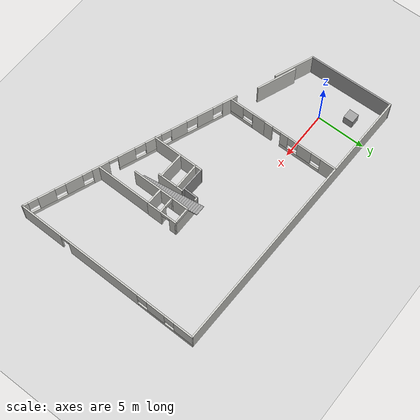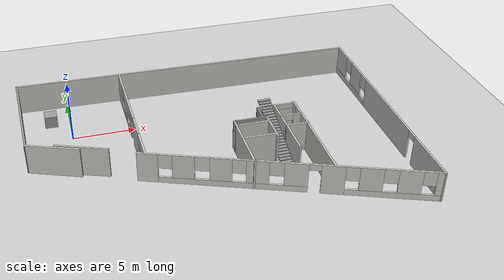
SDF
<sdf version="1.6">
 <world name="default">
  <light name="sun" type="directional">
   <pose>0 0 10 0 -0 0</pose>
   <diffuse>0.8 0.8 0.8 1</diffuse>
   <specular>0.1 0.1 0.1 1</specular>
   <attenuation>
    <range>1000</range>
    <constant>0.9</constant>
    <linear>0.01</linear>
    <quadratic>0.001</quadratic>
   </attenuation>
   <direction>-0.5 0.5 -1</direction>
  </light>
  <model name="ground_plane">
   <static>1</static>
   <link name="link">
    <collision name="collision">
     <geometry><plane><normal>0 0 1</normal><size>100 100</size></plane></geometry>
     <surface><friction><ode><mu>100</mu><mu2>50</mu2></ode></friction></surface>
    </collision>
    <visual name="visual">
     <cast_shadows>0</cast_shadows>
     <geometry><plane><normal>0 0 1</normal><size>100 100</size></plane></geometry>
     <material>
      <script><uri>file://media/materials/scripts/gazebo.material</uri><name>Gazebo/Grey</name></script>
     </material>
    </visual>
   </link>
  </model>
  <model name="unit_box_0_0">
   <pose>-1.5 2.5 0.5 0 -0 0</pose>
   <link name="link">
    <inertial>
     <mass>1</mass>
     <inertia>
      <ixx>0.166667</ixx>
      <ixy>0</ixy>
      <ixz>0</ixz>
      <iyy>0.166667</iyy>
      <iyz>0</iyz>
      <izz>0.166667</izz>
     </inertia>
    </inertial>
    <collision name="collision"><geometry><box><size>1 1 1</size></box></geometry></collision>
    <visual name="visual">
     <geometry><box><size>1 1 1</size></box></geometry>
     <material>
      <script><name>Gazebo/Grey</name><uri>file://media/materials/scripts/gazebo.material</uri></script>
     </material>
    </visual>
   </link>
  </model>
  <gravity>0 0 -9.8</gravity>
  <magnetic_field>6e-06 2.3e-05 -4.2e-05</magnetic_field>
  <atmosphere type="adiabatic"/>
  <physics name="default_physics" default="0" type="ode">
   <max_step_size>0.001</max_step_size>
   <real_time_factor>1</real_time_factor>
   <real_time_update_rate>1000</real_time_update_rate>
  </physics>
  <scene><ambient>0.4 0.4 0.4 1</ambient><background>0.7 0.7 0.7 1</background><shadows>1</shadows></scene>
  <spherical_coordinates>
   <surface_model>EARTH_WGS84</surface_model>
   <latitude_deg>0</latitude_deg>
   <longitude_deg>0</longitude_deg>
   <elevation>0</elevation>
   <heading_deg>0</heading_deg>
  </spherical_coordinates>
  <model name="Erle Office">
   <link name="Stairs_7">
    <visual name="Stairs_7_Visual_2">
     <pose>4.82632 -3.5898 0.231482 0 0 -3.14159</pose>
     <geometry><box><size>1 0.257016 0.092593</size></box></geometry>
     <material>
      <script><uri>file://media/materials/scripts/gazebo.material</uri><name>Gazebo/Grey</name></script>
      <ambient>1 1 1 1</ambient>
      <diffuse>0.7 0.7 0.7 1</diffuse>
      <specular>0.01 0.01 0.01 1</specular>
      <emissive>0 0 0 1</emissive>
     </material>
    </visual>
    <visual name="Stairs_7_Visual_0">
     <pose>4.82632 -4.10383 0.046296 0 0 -3.14159</pose>
     <geometry><box><size>1 0.257016 0.092593</size></box></geometry>
     <material>
      <script><uri>file://media/materials/scripts/gazebo.material</uri><name>Gazebo/Grey</name></script>
      <ambient>1 1 1 1</ambient>
      <diffuse>0.7 0.7 0.7 1</diffuse>
      <specular>0.01 0.01 0.01 1</specular>
      <emissive>0 0 0 1</emissive>
     </material>
    </visual>
    <visual name="Stairs_7_Visual_1">
     <pose>4.82632 -3.84681 0.138889 0 0 -3.14159</pose>
     <geometry><box><size>1 0.257016 0.092593</size></box></geometry>
     <material>
      <script><uri>file://media/materials/scripts/gazebo.material</uri><name>Gazebo/Grey</name></script>
      <ambient>1 1 1 1</ambient>
      <diffuse>0.7 0.7 0.7 1</diffuse>
      <specular>0.01 0.01 0.01 1</specular>
      <emissive>0 0 0 1</emissive>
     </material>
    </visual>
    <visual name="Stairs_7_Visual_3">
     <pose>4.82632 -3.33278 0.324074 0 0 -3.14159</pose>
     <geometry><box><size>1 0.257016 0.092593</size></box></geometry>
     <material>
      <script><uri>file://media/materials/scripts/gazebo.material</uri><name>Gazebo/Grey</name></script>
      <ambient>1 1 1 1</ambient>
      <diffuse>0.7 0.7 0.7 1</diffuse>
      <specular>0.01 0.01 0.01 1</specular>
      <emissive>0 0 0 1</emissive>
     </material>
    </visual>
    <visual name="Stairs_7_Visual_4">
     <pose>4.82632 -3.07577 0.416667 0 0 -3.14159</pose>
     <geometry><box><size>1 0.257016 0.092593</size></box></geometry>
     <material>
      <script><uri>file://media/materials/scripts/gazebo.material</uri><name>Gazebo/Grey</name></script>
      <ambient>1 1 1 1</ambient>
      <diffuse>0.7 0.7 0.7 1</diffuse>
      <specular>0.01 0.01 0.01 1</specular>
      <emissive>0 0 0 1</emissive>
     </material>
    </visual>
    <visual name="Stairs_7_Visual_5">
     <pose>4.82632 -2.81875 0.509259 0 0 -3.14159</pose>
     <geometry><box><size>1 0.257016 0.092593</size></box></geometry>
     <material>
      <script><uri>file://media/materials/scripts/gazebo.material</uri><name>Gazebo/Grey</name></script>
      <ambient>1 1 1 1</ambient>
      <diffuse>0.7 0.7 0.7 1</diffuse>
      <specular>0.01 0.01 0.01 1</specular>
      <emissive>0 0 0 1</emissive>
     </material>
    </visual>
    <visual name="Stairs_7_Visual_6">
     <pose>4.82632 -2.56174 0.601852 0 0 -3.14159</pose>
     <geometry><box><size>1 0.257016 0.092593</size></box></geometry>
     <material>
      <script><uri>file://media/materials/scripts/gazebo.material</uri><name>Gazebo/Grey</name></script>
      <ambient>1 1 1 1</ambient>
      <diffuse>0.7 0.7 0.7 1</diffuse>
      <specular>0.01 0.01 0.01 1</specular>
      <emissive>0 0 0 1</emissive>
     </material>
    </visual>
    <visual name="Stairs_7_Visual_7">
     <pose>4.82632 -2.30472 0.694444 0 0 -3.14159</pose>
     <geometry><box><size>1 0.257016 0.092593</size></box></geometry>
     <material>
      <script><uri>file://media/materials/scripts/gazebo.material</uri><name>Gazebo/Grey</name></script>
      <ambient>1 1 1 1</ambient>
      <diffuse>0.7 0.7 0.7 1</diffuse>
      <specular>0.01 0.01 0.01 1</specular>
      <emissive>0 0 0 1</emissive>
     </material>
    </visual>
    <visual name="Stairs_7_Visual_8">
     <pose>4.82632 -2.04771 0.787037 0 0 -3.14159</pose>
     <geometry><box><size>1 0.257016 0.092593</size></box></geometry>
     <material>
      <script><uri>file://media/materials/scripts/gazebo.material</uri><name>Gazebo/Grey</name></script>
      <ambient>1 1 1 1</ambient>
      <diffuse>0.7 0.7 0.7 1</diffuse>
      <specular>0.01 0.01 0.01 1</specular>
      <emissive>0 0 0 1</emissive>
     </material>
    </visual>
    <visual name="Stairs_7_Visual_9">
     <pose>4.82632 -1.79069 0.87963 0 0 -3.14159</pose>
     <geometry><box><size>1 0.257016 0.092593</size></box></geometry>
     <material>
      <script><uri>file://media/materials/scripts/gazebo.material</uri><name>Gazebo/Grey</name></script>
      <ambient>1 1 1 1</ambient>
      <diffuse>0.7 0.7 0.7 1</diffuse>
      <specular>0.01 0.01 0.01 1</specular>
      <emissive>0 0 0 1</emissive>
     </material>
    </visual>
    <visual name="Stairs_7_Visual_10">
     <pose>4.82632 -1.53367 0.972222 0 0 -3.14159</pose>
     <geometry><box><size>1 0.257016 0.092593</size></box></geometry>
     <material>
      <script><uri>file://media/materials/scripts/gazebo.material</uri><name>Gazebo/Grey</name></script>
      <ambient>1 1 1 1</ambient>
      <diffuse>0.7 0.7 0.7 1</diffuse>
      <specular>0.01 0.01 0.01 1</specular>
      <emissive>0 0 0 1</emissive>
     </material>
    </visual>
    <visual name="Stairs_7_Visual_11">
     <pose>4.82632 -1.27666 1.06482 0 0 -3.14159</pose>
     <geometry><box><size>1 0.257016 0.092593</size></box></geometry>
     <material>
      <script><uri>file://media/materials/scripts/gazebo.material</uri><name>Gazebo/Grey</name></script>
      <ambient>1 1 1 1</ambient>
      <diffuse>0.7 0.7 0.7 1</diffuse>
      <specular>0.01 0.01 0.01 1</specular>
      <emissive>0 0 0 1</emissive>
     </material>
    </visual>
    <visual name="Stairs_7_Visual_12">
     <pose>4.82632 -1.01964 1.15741 0 0 -3.14159</pose>
     <geometry><box><size>1 0.257016 0.092593</size></box></geometry>
     <material>
      <script><uri>file://media/materials/scripts/gazebo.material</uri><name>Gazebo/Grey</name></script>
      <ambient>1 1 1 1</ambient>
      <diffuse>0.7 0.7 0.7 1</diffuse>
      <specular>0.01 0.01 0.01 1</specular>
      <emissive>0 0 0 1</emissive>
     </material>
    </visual>
    <visual name="Stairs_7_Visual_13">
     <pose>4.82632 -0.762627 1.25 0 0 -3.14159</pose>
     <geometry><box><size>1 0.257016 0.092593</size></box></geometry>
     <material>
      <script><uri>file://media/materials/scripts/gazebo.material</uri><name>Gazebo/Grey</name></script>
      <ambient>1 1 1 1</ambient>
      <diffuse>0.7 0.7 0.7 1</diffuse>
      <specular>0.01 0.01 0.01 1</specular>
      <emissive>0 0 0 1</emissive>
     </material>
    </visual>
    <visual name="Stairs_7_Visual_14">
     <pose>4.82632 -0.505611 1.34259 0 0 -3.14159</pose>
     <geometry><box><size>1 0.257016 0.092593</size></box></geometry>
     <material>
      <script><uri>file://media/materials/scripts/gazebo.material</uri><name>Gazebo/Grey</name></script>
      <ambient>1 1 1 1</ambient>
      <diffuse>0.7 0.7 0.7 1</diffuse>
      <specular>0.01 0.01 0.01 1</specular>
      <emissive>0 0 0 1</emissive>
     </material>
    </visual>
    <visual name="Stairs_7_Visual_15">
     <pose>4.82632 -0.248596 1.43518 0 0 -3.14159</pose>
     <geometry><box><size>1 0.257016 0.092593</size></box></geometry>
     <material>
      <script><uri>file://media/materials/scripts/gazebo.material</uri><name>Gazebo/Grey</name></script>
      <ambient>1 1 1 1</ambient>
      <diffuse>0.7 0.7 0.7 1</diffuse>
      <specular>0.01 0.01 0.01 1</specular>
      <emissive>0 0 0 1</emissive>
     </material>
    </visual>
    <visual name="Stairs_7_Visual_16">
     <pose>4.82632 0.00842 1.52778 0 0 -3.14159</pose>
     <geometry><box><size>1 0.257016 0.092593</size></box></geometry>
     <material>
      <script><uri>file://media/materials/scripts/gazebo.material</uri><name>Gazebo/Grey</name></script>
      <ambient>1 1 1 1</ambient>
      <diffuse>0.7 0.7 0.7 1</diffuse>
      <specular>0.01 0.01 0.01 1</specular>
      <emissive>0 0 0 1</emissive>
     </material>
    </visual>
    <visual name="Stairs_7_Visual_17">
     <pose>4.82632 0.265435 1.62037 0 0 -3.14159</pose>
     <geometry><box><size>1 0.257016 0.092593</size></box></geometry>
     <material>
      <script><uri>file://media/materials/scripts/gazebo.material</uri><name>Gazebo/Grey</name></script>
      <ambient>1 1 1 1</ambient>
      <diffuse>0.7 0.7 0.7 1</diffuse>
      <specular>0.01 0.01 0.01 1</specular>
      <emissive>0 0 0 1</emissive>
     </material>
    </visual>
    <visual name="Stairs_7_Visual_18">
     <pose>4.82632 0.522451 1.71296 0 0 -3.14159</pose>
     <geometry><box><size>1 0.257016 0.092593</size></box></geometry>
     <material>
      <script><uri>file://media/materials/scripts/gazebo.material</uri><name>Gazebo/Grey</name></script>
      <ambient>1 1 1 1</ambient>
      <diffuse>0.7 0.7 0.7 1</diffuse>
      <specular>0.01 0.01 0.01 1</specular>
      <emissive>0 0 0 1</emissive>
     </material>
    </visual>
    <visual name="Stairs_7_Visual_19">
     <pose>4.82632 0.779467 1.80556 0 0 -3.14159</pose>
     <geometry><box><size>1 0.257016 0.092593</size></box></geometry>
     <material>
      <script><uri>file://media/materials/scripts/gazebo.material</uri><name>Gazebo/Grey</name></script>
      <ambient>1 1 1 1</ambient>
      <diffuse>0.7 0.7 0.7 1</diffuse>
      <specular>0.01 0.01 0.01 1</specular>
      <emissive>0 0 0 1</emissive>
     </material>
    </visual>
    <visual name="Stairs_7_Visual_20">
     <pose>4.82632 1.03648 1.89815 0 0 -3.14159</pose>
     <geometry><box><size>1 0.257016 0.092593</size></box></geometry>
     <material>
      <script><uri>file://media/materials/scripts/gazebo.material</uri><name>Gazebo/Grey</name></script>
      <ambient>1 1 1 1</ambient>
      <diffuse>0.7 0.7 0.7 1</diffuse>
      <specular>0.01 0.01 0.01 1</specular>
      <emissive>0 0 0 1</emissive>
     </material>
    </visual>
    <visual name="Stairs_7_Visual_21">
     <pose>4.82632 1.2935 1.99074 0 0 -3.14159</pose>
     <geometry><box><size>1 0.257016 0.092593</size></box></geometry>
     <material>
      <script><uri>file://media/materials/scripts/gazebo.material</uri><name>Gazebo/Grey</name></script>
      <ambient>1 1 1 1</ambient>
      <diffuse>0.7 0.7 0.7 1</diffuse>
      <specular>0.01 0.01 0.01 1</specular>
      <emissive>0 0 0 1</emissive>
     </material>
    </visual>
    <visual name="Stairs_7_Visual_22">
     <pose>4.82632 1.55051 2.08333 0 0 -3.14159</pose>
     <geometry><box><size>1 0.257016 0.092593</size></box></geometry>
     <material>
      <script><uri>file://media/materials/scripts/gazebo.material</uri><name>Gazebo/Grey</name></script>
      <ambient>1 1 1 1</ambient>
      <diffuse>0.7 0.7 0.7 1</diffuse>
      <specular>0.01 0.01 0.01 1</specular>
      <emissive>0 0 0 1</emissive>
     </material>
    </visual>
    <visual name="Stairs_7_Visual_23">
     <pose>4.82632 1.80753 2.17593 0 0 -3.14159</pose>
     <geometry><box><size>1 0.257016 0.092593</size></box></geometry>
     <material>
      <script><uri>file://media/materials/scripts/gazebo.material</uri><name>Gazebo/Grey</name></script>
      <ambient>1 1 1 1</ambient>
      <diffuse>0.7 0.7 0.7 1</diffuse>
      <specular>0.01 0.01 0.01 1</specular>
      <emissive>0 0 0 1</emissive>
     </material>
    </visual>
    <visual name="Stairs_7_Visual_24">
     <pose>4.82632 2.06454 2.26852 0 0 -3.14159</pose>
     <geometry><box><size>1 0.257016 0.092593</size></box></geometry>
     <material>
      <script><uri>file://media/materials/scripts/gazebo.material</uri><name>Gazebo/Grey</name></script>
      <ambient>1 1 1 1</ambient>
      <diffuse>0.7 0.7 0.7 1</diffuse>
      <specular>0.01 0.01 0.01 1</specular>
      <emissive>0 0 0 1</emissive>
     </material>
    </visual>
    <visual name="Stairs_7_Visual_25">
     <pose>4.82632 2.32156 2.36111 0 0 -3.14159</pose>
     <geometry><box><size>1 0.257016 0.092593</size></box></geometry>
     <material>
      <script><uri>file://media/materials/scripts/gazebo.material</uri><name>Gazebo/Grey</name></script>
      <ambient>1 1 1 1</ambient>
      <diffuse>0.7 0.7 0.7 1</diffuse>
      <specular>0.01 0.01 0.01 1</specular>
      <emissive>0 0 0 1</emissive>
     </material>
    </visual>
    <visual name="Stairs_7_Visual_26">
     <pose>4.82632 2.57858 2.4537 0 0 -3.14159</pose>
     <geometry><box><size>1 0.257016 0.092593</size></box></geometry>
     <material>
      <script><uri>file://media/materials/scripts/gazebo.material</uri><name>Gazebo/Grey</name></script>
      <ambient>1 1 1 1</ambient>
      <diffuse>0.7 0.7 0.7 1</diffuse>
      <specular>0.01 0.01 0.01 1</specular>
      <emissive>0 0 0 1</emissive>
     </material>
    </visual>
    <collision name="Stairs_7_Collision_0">
     <pose>4.82632 -4.10383 0.046296 0 0 -3.14159</pose>
     <geometry><box><size>1 0.257016 0.092593</size></box></geometry>
     <surface>
      <friction>
       <ode><mu>1</mu><mu2>1</mu2><fdir1>0 0 0</fdir1><slip1>0</slip1><slip2>0</slip2></ode>
       <torsional>
        <coefficient>1</coefficient>
        <patch_radius>0</patch_radius>
        <surface_radius>0</surface_radius>
        <use_patch_radius>1</use_patch_radius>
        <ode><slip>0</slip></ode>
       </torsional>
      </friction>
      <bounce><restitution_coefficient>0</restitution_coefficient><threshold>1e+06</threshold></bounce>
      <contact>
       <collide_without_contact>0</collide_without_contact>
       <collide_without_contact_bitmask>1</collide_without_contact_bitmask>
       <collide_bitmask>1</collide_bitmask>
       <ode>
        <soft_cfm>0</soft_cfm>
        <soft_erp>0.2</soft_erp>
        <kp>1e+13</kp>
        <kd>1</kd>
        <max_vel>0.01</max_vel>
        <min_depth>0</min_depth>
       </ode>
       <bullet>
        <split_impulse>1</split_impulse>
        <split_impulse_penetration_threshold>-0.01</split_impulse_penetration_threshold>
        <soft_cfm>0</soft_cfm>
        <soft_erp>0.2</soft_erp>
        <kp>1e+13</kp>
        <kd>1</kd>
       </bullet>
      </contact>
     </surface>
    </collision>
    <collision name="Stairs_7_Collision_1">
     <pose>4.82632 -3.84681 0.138889 0 0 -3.14159</pose>
     <geometry><box><size>1 0.257016 0.092593</size></box></geometry>
     <surface>
      <friction>
       <ode><mu>1</mu><mu2>1</mu2><fdir1>0 0 0</fdir1><slip1>0</slip1><slip2>0</slip2></ode>
       <torsional>
        <coefficient>1</coefficient>
        <patch_radius>0</patch_radius>
        <surface_radius>0</surface_radius>
        <use_patch_radius>1</use_patch_radius>
        <ode><slip>0</slip></ode>
       </torsional>
      </friction>
      <bounce><restitution_coefficient>0</restitution_coefficient><threshold>1e+06</threshold></bounce>
      <contact>
       <collide_without_contact>0</collide_without_contact>
       <collide_without_contact_bitmask>1</collide_without_contact_bitmask>
       <collide_bitmask>1</collide_bitmask>
       <ode>
        <soft_cfm>0</soft_cfm>
        <soft_erp>0.2</soft_erp>
        <kp>1e+13</kp>
        <kd>1</kd>
        <max_vel>0.01</max_vel>
        <min_depth>0</min_depth>
       </ode>
       <bullet>
        <split_impulse>1</split_impulse>
        <split_impulse_penetration_threshold>-0.01</split_impulse_penetration_threshold>
        <soft_cfm>0</soft_cfm>
        <soft_erp>0.2</soft_erp>
        <kp>1e+13</kp>
        <kd>1</kd>
       </bullet>
      </contact>
     </surface>
    </collision>
    <collision name="Stairs_7_Collision_3">
     <pose>4.82632 -3.33278 0.324074 0 0 -3.14159</pose>
     <geometry><box><size>1 0.257016 0.092593</size></box></geometry>
     <surface>
      <friction>
       <ode><mu>1</mu><mu2>1</mu2><fdir1>0 0 0</fdir1><slip1>0</slip1><slip2>0</slip2></ode>
       <torsional>
        <coefficient>1</coefficient>
        <patch_radius>0</patch_radius>
        <surface_radius>0</surface_radius>
        <use_patch_radius>1</use_patch_radius>
        <ode><slip>0</slip></ode>
       </torsional>
      </friction>
      <bounce><restitution_coefficient>0</restitution_coefficient><threshold>1e+06</threshold></bounce>
      <contact>
       <collide_without_contact>0</collide_without_contact>
       <collide_without_contact_bitmask>1</collide_without_contact_bitmask>
       <collide_bitmask>1</collide_bitmask>
       <ode>
        <soft_cfm>0</soft_cfm>
        <soft_erp>0.2</soft_erp>
        <kp>1e+13</kp>
        <kd>1</kd>
        <max_vel>0.01</max_vel>
        <min_depth>0</min_depth>
       </ode>
       <bullet>
        <split_impulse>1</split_impulse>
        <split_impulse_penetration_threshold>-0.01</split_impulse_penetration_threshold>
        <soft_cfm>0</soft_cfm>
        <soft_erp>0.2</soft_erp>
        <kp>1e+13</kp>
        <kd>1</kd>
       </bullet>
      </contact>
     </surface>
    </collision>
    <collision name="Stairs_7_Collision_2">
     <pose>4.82632 -3.5898 0.231482 0 0 -3.14159</pose>
     <geometry><box><size>1 0.257016 0.092593</size></box></geometry>
     <surface>
      <friction>
       <ode><mu>1</mu><mu2>1</mu2><fdir1>0 0 0</fdir1><slip1>0</slip1><slip2>0</slip2></ode>
       <torsional>
        <coefficient>1</coefficient>
        <patch_radius>0</patch_radius>
        <surface_radius>0</surface_radius>
        <use_patch_radius>1</use_patch_radius>
        <ode><slip>0</slip></ode>
       </torsional>
      </friction>
      <bounce><restitution_coefficient>0</restitution_coefficient><threshold>1e+06</threshold></bounce>
      <contact>
       <collide_without_contact>0</collide_without_contact>
       <collide_without_contact_bitmask>1</collide_without_contact_bitmask>
       <collide_bitmask>1</collide_bitmask>
       <ode>
        <soft_cfm>0</soft_cfm>
        <soft_erp>0.2</soft_erp>
        <kp>1e+13</kp>
        <kd>1</kd>
        <max_vel>0.01</max_vel>
        <min_depth>0</min_depth>
       </ode>
       <bullet>
        <split_impulse>1</split_impulse>
        <split_impulse_penetration_threshold>-0.01</split_impulse_penetration_threshold>
        <soft_cfm>0</soft_cfm>
        <soft_erp>0.2</soft_erp>
        <kp>1e+13</kp>
        <kd>1</kd>
       </bullet>
      </contact>
     </surface>
    </collision>
    <collision name="Stairs_7_Collision_4">
     <pose>4.82632 -3.07577 0.416667 0 0 -3.14159</pose>
     <geometry><box><size>1 0.257016 0.092593</size></box></geometry>
     <surface>
      <friction>
       <ode><mu>1</mu><mu2>1</mu2><fdir1>0 0 0</fdir1><slip1>0</slip1><slip2>0</slip2></ode>
       <torsional>
        <coefficient>1</coefficient>
        <patch_radius>0</patch_radius>
        <surface_radius>0</surface_radius>
        <use_patch_radius>1</use_patch_radius>
        <ode><slip>0</slip></ode>
       </torsional>
      </friction>
      <bounce><restitution_coefficient>0</restitution_coefficient><threshold>1e+06</threshold></bounce>
      <contact>
       <collide_without_contact>0</collide_without_contact>
       <collide_without_contact_bitmask>1</collide_without_contact_bitmask>
       <collide_bitmask>1</collide_bitmask>
       <ode>
        <soft_cfm>0</soft_cfm>
        <soft_erp>0.2</soft_erp>
        <kp>1e+13</kp>
        <kd>1</kd>
        <max_vel>0.01</max_vel>
        <min_depth>0</min_depth>
       </ode>
       <bullet>
        <split_impulse>1</split_impulse>
        <split_impulse_penetration_threshold>-0.01</split_impulse_penetration_threshold>
        <soft_cfm>0</soft_cfm>
        <soft_erp>0.2</soft_erp>
        <kp>1e+13</kp>
        <kd>1</kd>
       </bullet>
      </contact>
     </surface>
    </collision>
    <collision name="Stairs_7_Collision_5">
     <pose>4.82632 -2.81875 0.509259 0 0 -3.14159</pose>
     <geometry><box><size>1 0.257016 0.092593</size></box></geometry>
     <surface>
      <friction>
       <ode><mu>1</mu><mu2>1</mu2><fdir1>0 0 0</fdir1><slip1>0</slip1><slip2>0</slip2></ode>
       <torsional>
        <coefficient>1</coefficient>
        <patch_radius>0</patch_radius>
        <surface_radius>0</surface_radius>
        <use_patch_radius>1</use_patch_radius>
        <ode><slip>0</slip></ode>
       </torsional>
      </friction>
      <bounce><restitution_coefficient>0</restitution_coefficient><threshold>1e+06</threshold></bounce>
      <contact>
       <collide_without_contact>0</collide_without_contact>
       <collide_without_contact_bitmask>1</collide_without_contact_bitmask>
       <collide_bitmask>1</collide_bitmask>
       <ode>
        <soft_cfm>0</soft_cfm>
        <soft_erp>0.2</soft_erp>
        <kp>1e+13</kp>
        <kd>1</kd>
        <max_vel>0.01</max_vel>
        <min_depth>0</min_depth>
       </ode>
       <bullet>
        <split_impulse>1</split_impulse>
        <split_impulse_penetration_threshold>-0.01</split_impulse_penetration_threshold>
        <soft_cfm>0</soft_cfm>
        <soft_erp>0.2</soft_erp>
        <kp>1e+13</kp>
        <kd>1</kd>
       </bullet>
      </contact>
     </surface>
    </collision>
    <collision name="Stairs_7_Collision_6">
     <pose>4.82632 -2.56174 0.601852 0 0 -3.14159</pose>
     <geometry><box><size>1 0.257016 0.092593</size></box></geometry>
     <surface>
      <friction>
       <ode><mu>1</mu><mu2>1</mu2><fdir1>0 0 0</fdir1><slip1>0</slip1><slip2>0</slip2></ode>
       <torsional>
        <coefficient>1</coefficient>
        <patch_radius>0</patch_radius>
        <surface_radius>0</surface_radius>
        <use_patch_radius>1</use_patch_radius>
        <ode><slip>0</slip></ode>
       </torsional>
      </friction>
      <bounce><restitution_coefficient>0</restitution_coefficient><threshold>1e+06</threshold></bounce>
      <contact>
       <collide_without_contact>0</collide_without_contact>
       <collide_without_contact_bitmask>1</collide_without_contact_bitmask>
       <collide_bitmask>1</collide_bitmask>
       <ode>
        <soft_cfm>0</soft_cfm>
        <soft_erp>0.2</soft_erp>
        <kp>1e+13</kp>
        <kd>1</kd>
        <max_vel>0.01</max_vel>
        <min_depth>0</min_depth>
       </ode>
       <bullet>
        <split_impulse>1</split_impulse>
        <split_impulse_penetration_threshold>-0.01</split_impulse_penetration_threshold>
        <soft_cfm>0</soft_cfm>
        <soft_erp>0.2</soft_erp>
        <kp>1e+13</kp>
        <kd>1</kd>
       </bullet>
      </contact>
     </surface>
    </collision>
    <collision name="Stairs_7_Collision_9">
     <pose>4.82632 -1.79069 0.87963 0 0 -3.14159</pose>
     <geometry><box><size>1 0.257016 0.092593</size></box></geometry>
     <surface>
      <friction>
       <ode><mu>1</mu><mu2>1</mu2><fdir1>0 0 0</fdir1><slip1>0</slip1><slip2>0</slip2></ode>
       <torsional>
        <coefficient>1</coefficient>
        <patch_radius>0</patch_radius>
        <surface_radius>0</surface_radius>
        <use_patch_radius>1</use_patch_radius>
        <ode><slip>0</slip></ode>
       </torsional>
      </friction>
      <bounce><restitution_coefficient>0</restitution_coefficient><threshold>1e+06</threshold></bounce>
      <contact>
       <collide_without_contact>0</collide_without_contact>
       <collide_without_contact_bitmask>1</collide_without_contact_bitmask>
       <collide_bitmask>1</collide_bitmask>
       <ode>
        <soft_cfm>0</soft_cfm>
        <soft_erp>0.2</soft_erp>
        <kp>1e+13</kp>
        <kd>1</kd>
        <max_vel>0.01</max_vel>
        <min_depth>0</min_depth>
       </ode>
       <bullet>
        <split_impulse>1</split_impulse>
        <split_impulse_penetration_threshold>-0.01</split_impulse_penetration_threshold>
        <soft_cfm>0</soft_cfm>
        <soft_erp>0.2</soft_erp>
        <kp>1e+13</kp>
        <kd>1</kd>
       </bullet>
      </contact>
     </surface>
    </collision>
    <collision name="Stairs_7_Collision_7">
     <pose>4.82632 -2.30472 0.694444 0 0 -3.14159</pose>
     <geometry><box><size>1 0.257016 0.092593</size></box></geometry>
     <surface>
      <friction>
       <ode><mu>1</mu><mu2>1</mu2><fdir1>0 0 0</fdir1><slip1>0</slip1><slip2>0</slip2></ode>
       <torsional>
        <coefficient>1</coefficient>
        <patch_radius>0</patch_radius>
        <surface_radius>0</surface_radius>
        <use_patch_radius>1</use_patch_radius>
        <ode><slip>0</slip></ode>
       </torsional>
      </friction>
      <bounce><restitution_coefficient>0</restitution_coefficient><threshold>1e+06</threshold></bounce>
      <contact>
       <collide_without_contact>0</collide_without_contact>
       <collide_without_contact_bitmask>1</collide_without_contact_bitmask>
       <collide_bitmask>1</collide_bitmask>
       <ode>
        <soft_cfm>0</soft_cfm>
        <soft_erp>0.2</soft_erp>
        <kp>1e+13</kp>
        <kd>1</kd>
        <max_vel>0.01</max_vel>
        <min_depth>0</min_depth>
       </ode>
       <bullet>
        <split_impulse>1</split_impulse>
        <split_impulse_penetration_threshold>-0.01</split_impulse_penetration_threshold>
        <soft_cfm>0</soft_cfm>
        <soft_erp>0.2</soft_erp>
        <kp>1e+13</kp>
        <kd>1</kd>
       </bullet>
      </contact>
     </surface>
    </collision>
    <collision name="Stairs_7_Collision_10">
     <pose>4.82632 -1.53367 0.972222 0 0 -3.14159</pose>
     <geometry><box><size>1 0.257016 0.092593</size></box></geometry>
     <surface>
      <friction>
       <ode><mu>1</mu><mu2>1</mu2><fdir1>0 0 0</fdir1><slip1>0</slip1><slip2>0</slip2></ode>
       <torsional>
        <coefficient>1</coefficient>
        <patch_radius>0</patch_radius>
        <surface_radius>0</surface_radius>
        <use_patch_radius>1</use_patch_radius>
        <ode><slip>0</slip></ode>
       </torsional>
      </friction>
      <bounce><restitution_coefficient>0</restitution_coefficient><threshold>1e+06</threshold></bounce>
      <contact>
       <collide_without_contact>0</collide_without_contact>
       <collide_without_contact_bitmask>1</collide_without_contact_bitmask>
       <collide_bitmask>1</collide_bitmask>
       <ode>
        <soft_cfm>0</soft_cfm>
        <soft_erp>0.2</soft_erp>
        <kp>1e+13</kp>
        <kd>1</kd>
        <max_vel>0.01</max_vel>
        <min_depth>0</min_depth>
       </ode>
       <bullet>
        <split_impulse>1</split_impulse>
        <split_impulse_penetration_threshold>-0.01</split_impulse_penetration_threshold>
        <soft_cfm>0</soft_cfm>
        <soft_erp>0.2</soft_erp>
        <kp>1e+13</kp>
        <kd>1</kd>
       </bullet>
      </contact>
     </surface>
    </collision>
    <collision name="Stairs_7_Collision_8">
     <pose>4.82632 -2.04771 0.787037 0 0 -3.14159</pose>
     <geometry><box><size>1 0.257016 0.092593</size></box></geometry>
     <surface>
      <friction>
       <ode><mu>1</mu><mu2>1</mu2><fdir1>0 0 0</fdir1><slip1>0</slip1><slip2>0</slip2></ode>
       <torsional>
        <coefficient>1</coefficient>
        <patch_radius>0</patch_radius>
        <surface_radius>0</surface_radius>
        <use_patch_radius>1</use_patch_radius>
        <ode><slip>0</slip></ode>
       </torsional>
      </friction>
      <bounce><restitution_coefficient>0</restitution_coefficient><threshold>1e+06</threshold></bounce>
      <contact>
       <collide_without_contact>0</collide_without_contact>
       <collide_without_contact_bitmask>1</collide_without_contact_bitmask>
       <collide_bitmask>1</collide_bitmask>
       <ode>
        <soft_cfm>0</soft_cfm>
        <soft_erp>0.2</soft_erp>
        <kp>1e+13</kp>
        <kd>1</kd>
        <max_vel>0.01</max_vel>
        <min_depth>0</min_depth>
       </ode>
       <bullet>
        <split_impulse>1</split_impulse>
        <split_impulse_penetration_threshold>-0.01</split_impulse_penetration_threshold>
        <soft_cfm>0</soft_cfm>
        <soft_erp>0.2</soft_erp>
        <kp>1e+13</kp>
        <kd>1</kd>
       </bullet>
      </contact>
     </surface>
    </collision>
    <collision name="Stairs_7_Collision_11">
     <pose>4.82632 -1.27666 1.06482 0 0 -3.14159</pose>
     <geometry><box><size>1 0.257016 0.092593</size></box></geometry>
     <surface>
      <friction>
       <ode><mu>1</mu><mu2>1</mu2><fdir1>0 0 0</fdir1><slip1>0</slip1><slip2>0</slip2></ode>
       <torsional>
        <coefficient>1</coefficient>
        <patch_radius>0</patch_radius>
        <surface_radius>0</surface_radius>
        <use_patch_radius>1</use_patch_radius>
        <ode><slip>0</slip></ode>
       </torsional>
      </friction>
      <bounce><restitution_coefficient>0</restitution_coefficient><threshold>1e+06</threshold></bounce>
      <contact>
       <collide_without_contact>0</collide_without_contact>
       <collide_without_contact_bitmask>1</collide_without_contact_bitmask>
       <collide_bitmask>1</collide_bitmask>
       <ode>
        <soft_cfm>0</soft_cfm>
        <soft_erp>0.2</soft_erp>
        <kp>1e+13</kp>
        <kd>1</kd>
        <max_vel>0.01</max_vel>
        <min_depth>0</min_depth>
       </ode>
       <bullet>
        <split_impulse>1</split_impulse>
        <split_impulse_penetration_threshold>-0.01</split_impulse_penetration_threshold>
        <soft_cfm>0</soft_cfm>
        <soft_erp>0.2</soft_erp>
        <kp>1e+13</kp>
        <kd>1</kd>
       </bullet>
      </contact>
     </surface>
    </collision>
    <collision name="Stairs_7_Collision_12">
     <pose>4.82632 -1.01964 1.15741 0 0 -3.14159</pose>
     <geometry><box><size>1 0.257016 0.092593</size></box></geometry>
     <surface>
      <friction>
       <ode><mu>1</mu><mu2>1</mu2><fdir1>0 0 0</fdir1><slip1>0</slip1><slip2>0</slip2></ode>
       <torsional>
        <coefficient>1</coefficient>
        <patch_radius>0</patch_radius>
        <surface_radius>0</surface_radius>
        <use_patch_radius>1</use_patch_radius>
        <ode><slip>0</slip></ode>
       </torsional>
      </friction>
      <bounce><restitution_coefficient>0</restitution_coefficient><threshold>1e+06</threshold></bounce>
      <contact>
       <collide_without_contact>0</collide_without_contact>
       <collide_without_contact_bitmask>1</collide_without_contact_bitmask>
       <collide_bitmask>1</collide_bitmask>
       <ode>
        <soft_cfm>0</soft_cfm>
        <soft_erp>0.2</soft_erp>
        <kp>1e+13</kp>
        <kd>1</kd>
        <max_vel>0.01</max_vel>
        <min_depth>0</min_depth>
       </ode>
       <bullet>
        <split_impulse>1</split_impulse>
        <split_impulse_penetration_threshold>-0.01</split_impulse_penetration_threshold>
        <soft_cfm>0</soft_cfm>
        <soft_erp>0.2</soft_erp>
        <kp>1e+13</kp>
        <kd>1</kd>
       </bullet>
      </contact>
     </surface>
    </collision>
    <collision name="Stairs_7_Collision_13">
     <pose>4.82632 -0.762627 1.25 0 0 -3.14159</pose>
     <geometry><box><size>1 0.257016 0.092593</size></box></geometry>
     <surface>
      <friction>
       <ode><mu>1</mu><mu2>1</mu2><fdir1>0 0 0</fdir1><slip1>0</slip1><slip2>0</slip2></ode>
       <torsional>
        <coefficient>1</coefficient>
        <patch_radius>0</patch_radius>
        <surface_radius>0</surface_radius>
        <use_patch_radius>1</use_patch_radius>
        <ode><slip>0</slip></ode>
       </torsional>
      </friction>
      <bounce><restitution_coefficient>0</restitution_coefficient><threshold>1e+06</threshold></bounce>
      <contact>
       <collide_without_contact>0</collide_without_contact>
       <collide_without_contact_bitmask>1</collide_without_contact_bitmask>
       <collide_bitmask>1</collide_bitmask>
       <ode>
        <soft_cfm>0</soft_cfm>
        <soft_erp>0.2</soft_erp>
        <kp>1e+13</kp>
        <kd>1</kd>
        <max_vel>0.01</max_vel>
        <min_depth>0</min_depth>
       </ode>
       <bullet>
        <split_impulse>1</split_impulse>
        <split_impulse_penetration_threshold>-0.01</split_impulse_penetration_threshold>
        <soft_cfm>0</soft_cfm>
        <soft_erp>0.2</soft_erp>
        <kp>1e+13</kp>
        <kd>1</kd>
       </bullet>
      </contact>
     </surface>
    </collision>
    <collision name="Stairs_7_Collision_16">
     <pose>4.82632 0.00842 1.52778 0 0 -3.14159</pose>
     <geometry><box><size>1 0.257016 0.092593</size></box></geometry>
     <surface>
      <friction>
       <ode><mu>1</mu><mu2>1</mu2><fdir1>0 0 0</fdir1><slip1>0</slip1><slip2>0</slip2></ode>
       <torsional>
        <coefficient>1</coefficient>
        <patch_radius>0</patch_radius>
        <surface_radius>0</surface_radius>
        <use_patch_radius>1</use_patch_radius>
        <ode><slip>0</slip></ode>
       </torsional>
      </friction>
      <bounce><restitution_coefficient>0</restitution_coefficient><threshold>1e+06</threshold></bounce>
      <contact>
       <collide_without_contact>0</collide_without_contact>
       <collide_without_contact_bitmask>1</collide_without_contact_bitmask>
       <collide_bitmask>1</collide_bitmask>
       <ode>
        <soft_cfm>0</soft_cfm>
        <soft_erp>0.2</soft_erp>
        <kp>1e+13</kp>
        <kd>1</kd>
        <max_vel>0.01</max_vel>
        <min_depth>0</min_depth>
       </ode>
       <bullet>
        <split_impulse>1</split_impulse>
        <split_impulse_penetration_threshold>-0.01</split_impulse_penetration_threshold>
        <soft_cfm>0</soft_cfm>
        <soft_erp>0.2</soft_erp>
        <kp>1e+13</kp>
        <kd>1</kd>
       </bullet>
      </contact>
     </surface>
    </collision>
    <collision name="Stairs_7_Collision_14">
     <pose>4.82632 -0.505611 1.34259 0 0 -3.14159</pose>
     <geometry><box><size>1 0.257016 0.092593</size></box></geometry>
     <surface>
      <friction>
       <ode><mu>1</mu><mu2>1</mu2><fdir1>0 0 0</fdir1><slip1>0</slip1><slip2>0</slip2></ode>
       <torsional>
        <coefficient>1</coefficient>
        <patch_radius>0</patch_radius>
        <surface_radius>0</surface_radius>
        <use_patch_radius>1</use_patch_radius>
        <ode><slip>0</slip></ode>
       </torsional>
      </friction>
      <bounce><restitution_coefficient>0</restitution_coefficient><threshold>1e+06</threshold></bounce>
      <contact>
       <collide_without_contact>0</collide_without_contact>
       <collide_without_contact_bitmask>1</collide_without_contact_bitmask>
       <collide_bitmask>1</collide_bitmask>
       <ode>
        <soft_cfm>0</soft_cfm>
        <soft_erp>0.2</soft_erp>
        <kp>1e+13</kp>
        <kd>1</kd>
        <max_vel>0.01</max_vel>
        <min_depth>0</min_depth>
       </ode>
       <bullet>
        <split_impulse>1</split_impulse>
        <split_impulse_penetration_threshold>-0.01</split_impulse_penetration_threshold>
        <soft_cfm>0</soft_cfm>
        <soft_erp>0.2</soft_erp>
        <kp>1e+13</kp>
        <kd>1</kd>
       </bullet>
      </contact>
     </surface>
    </collision>
    <collision name="Stairs_7_Collision_15">
     <pose>4.82632 -0.248596 1.43518 0 0 -3.14159</pose>
     <geometry><box><size>1 0.257016 0.092593</size></box></geometry>
     <surface>
      <friction>
       <ode><mu>1</mu><mu2>1</mu2><fdir1>0 0 0</fdir1><slip1>0</slip1><slip2>0</slip2></ode>
       <torsional>
        <coefficient>1</coefficient>
        <patch_radius>0</patch_radius>
        <surface_radius>0</surface_radius>
        <use_patch_radius>1</use_patch_radius>
        <ode><slip>0</slip></ode>
       </torsional>
      </friction>
      <bounce><restitution_coefficient>0</restitution_coefficient><threshold>1e+06</threshold></bounce>
      <contact>
       <collide_without_contact>0</collide_without_contact>
       <collide_without_contact_bitmask>1</collide_without_contact_bitmask>
       <collide_bitmask>1</collide_bitmask>
       <ode>
        <soft_cfm>0</soft_cfm>
        <soft_erp>0.2</soft_erp>
        <kp>1e+13</kp>
        <kd>1</kd>
        <max_vel>0.01</max_vel>
        <min_depth>0</min_depth>
       </ode>
       <bullet>
        <split_impulse>1</split_impulse>
        <split_impulse_penetration_threshold>-0.01</split_impulse_penetration_threshold>
        <soft_cfm>0</soft_cfm>
        <soft_erp>0.2</soft_erp>
        <kp>1e+13</kp>
        <kd>1</kd>
       </bullet>
      </contact>
     </surface>
    </collision>
    <collision name="Stairs_7_Collision_19">
     <pose>4.82632 0.779467 1.80556 0 0 -3.14159</pose>
     <geometry><box><size>1 0.257016 0.092593</size></box></geometry>
     <surface>
      <friction>
       <ode><mu>1</mu><mu2>1</mu2><fdir1>0 0 0</fdir1><slip1>0</slip1><slip2>0</slip2></ode>
       <torsional>
        <coefficient>1</coefficient>
        <patch_radius>0</patch_radius>
        <surface_radius>0</surface_radius>
        <use_patch_radius>1</use_patch_radius>
        <ode><slip>0</slip></ode>
       </torsional>
      </friction>
      <bounce><restitution_coefficient>0</restitution_coefficient><threshold>1e+06</threshold></bounce>
      <contact>
       <collide_without_contact>0</collide_without_contact>
       <collide_without_contact_bitmask>1</collide_without_contact_bitmask>
       <collide_bitmask>1</collide_bitmask>
       <ode>
        <soft_cfm>0</soft_cfm>
        <soft_erp>0.2</soft_erp>
        <kp>1e+13</kp>
        <kd>1</kd>
        <max_vel>0.01</max_vel>
        <min_depth>0</min_depth>
       </ode>
       <bullet>
        <split_impulse>1</split_impulse>
        <split_impulse_penetration_threshold>-0.01</split_impulse_penetration_threshold>
        <soft_cfm>0</soft_cfm>
        <soft_erp>0.2</soft_erp>
        <kp>1e+13</kp>
        <kd>1</kd>
       </bullet>
      </contact>
     </surface>
    </collision>
    <collision name="Stairs_7_Collision_18">
     <pose>4.82632 0.522451 1.71296 0 0 -3.14159</pose>
     <geometry><box><size>1 0.257016 0.092593</size></box></geometry>
     <surface>
      <friction>
       <ode><mu>1</mu><mu2>1</mu2><fdir1>0 0 0</fdir1><slip1>0</slip1><slip2>0</slip2></ode>
       <torsional>
        <coefficient>1</coefficient>
        <patch_radius>0</patch_radius>
        <surface_radius>0</surface_radius>
        <use_patch_radius>1</use_patch_radius>
        <ode><slip>0</slip></ode>
       </torsional>
      </friction>
      <bounce><restitution_coefficient>0</restitution_coefficient><threshold>1e+06</threshold></bounce>
      <contact>
       <collide_without_contact>0</collide_without_contact>
       <collide_without_contact_bitmask>1</collide_without_contact_bitmask>
       <collide_bitmask>1</collide_bitmask>
       <ode>
        <soft_cfm>0</soft_cfm>
        <soft_erp>0.2</soft_erp>
        <kp>1e+13</kp>
        <kd>1</kd>
        <max_vel>0.01</max_vel>
        <min_depth>0</min_depth>
       </ode>
       <bullet>
        <split_impulse>1</split_impulse>
        <split_impulse_penetration_threshold>-0.01</split_impulse_penetration_threshold>
        <soft_cfm>0</soft_cfm>
        <soft_erp>0.2</soft_erp>
        <kp>1e+13</kp>
        <kd>1</kd>
       </bullet>
      </contact>
     </surface>
    </collision>
    <collision name="Stairs_7_Collision_17">
     <pose>4.82632 0.265435 1.62037 0 0 -3.14159</pose>
     <geometry><box><size>1 0.257016 0.092593</size></box></geometry>
     <surface>
      <friction>
       <ode><mu>1</mu><mu2>1</mu2><fdir1>0 0 0</fdir1><slip1>0</slip1><slip2>0</slip2></ode>
       <torsional>
        <coefficient>1</coefficient>
        <patch_radius>0</patch_radius>
        <surface_radius>0</surface_radius>
        <use_patch_radius>1</use_patch_radius>
        <ode><slip>0</slip></ode>
       </torsional>
      </friction>
      <bounce><restitution_coefficient>0</restitution_coefficient><threshold>1e+06</threshold></bounce>
      <contact>
       <collide_without_contact>0</collide_without_contact>
       <collide_without_contact_bitmask>1</collide_without_contact_bitmask>
       <collide_bitmask>1</collide_bitmask>
       <ode>
        <soft_cfm>0</soft_cfm>
        <soft_erp>0.2</soft_erp>
        <kp>1e+13</kp>
        <kd>1</kd>
        <max_vel>0.01</max_vel>
        <min_depth>0</min_depth>
       </ode>
       <bullet>
        <split_impulse>1</split_impulse>
        <split_impulse_penetration_threshold>-0.01</split_impulse_penetration_threshold>
        <soft_cfm>0</soft_cfm>
        <soft_erp>0.2</soft_erp>
        <kp>1e+13</kp>
        <kd>1</kd>
       </bullet>
      </contact>
     </surface>
    </collision>
    <collision name="Stairs_7_Collision_20">
     <pose>4.82632 1.03648 1.89815 0 0 -3.14159</pose>
     <geometry><box><size>1 0.257016 0.092593</size></box></geometry>
     <surface>
      <friction>
       <ode><mu>1</mu><mu2>1</mu2><fdir1>0 0 0</fdir1><slip1>0</slip1><slip2>0</slip2></ode>
       <torsional>
        <coefficient>1</coefficient>
        <patch_radius>0</patch_radius>
        <surface_radius>0</surface_radius>
        <use_patch_radius>1</use_patch_radius>
        <ode><slip>0</slip></ode>
       </torsional>
      </friction>
      <bounce><restitution_coefficient>0</restitution_coefficient><threshold>1e+06</threshold></bounce>
      <contact>
       <collide_without_contact>0</collide_without_contact>
       <collide_without_contact_bitmask>1</collide_without_contact_bitmask>
       <collide_bitmask>1</collide_bitmask>
       <ode>
        <soft_cfm>0</soft_cfm>
        <soft_erp>0.2</soft_erp>
        <kp>1e+13</kp>
        <kd>1</kd>
        <max_vel>0.01</max_vel>
        <min_depth>0</min_depth>
       </ode>
       <bullet>
        <split_impulse>1</split_impulse>
        <split_impulse_penetration_threshold>-0.01</split_impulse_penetration_threshold>
        <soft_cfm>0</soft_cfm>
        <soft_erp>0.2</soft_erp>
        <kp>1e+13</kp>
        <kd>1</kd>
       </bullet>
      </contact>
     </surface>
    </collision>
    <collision name="Stairs_7_Collision_23">
     <pose>4.82632 1.80753 2.17593 0 0 -3.14159</pose>
     <geometry><box><size>1 0.257016 0.092593</size></box></geometry>
     <surface>
      <friction>
       <ode><mu>1</mu><mu2>1</mu2><fdir1>0 0 0</fdir1><slip1>0</slip1><slip2>0</slip2></ode>
       <torsional>
        <coefficient>1</coefficient>
        <patch_radius>0</patch_radius>
        <surface_radius>0</surface_radius>
        <use_patch_radius>1</use_patch_radius>
        <ode><slip>0</slip></ode>
       </torsional>
      </friction>
      <bounce><restitution_coefficient>0</restitution_coefficient><threshold>1e+06</threshold></bounce>
      <contact>
       <collide_without_contact>0</collide_without_contact>
       <collide_without_contact_bitmask>1</collide_without_contact_bitmask>
       <collide_bitmask>1</collide_bitmask>
       <ode>
        <soft_cfm>0</soft_cfm>
        <soft_erp>0.2</soft_erp>
        <kp>1e+13</kp>
        <kd>1</kd>
        <max_vel>0.01</max_vel>
        <min_depth>0</min_depth>
       </ode>
       <bullet>
        <split_impulse>1</split_impulse>
        <split_impulse_penetration_threshold>-0.01</split_impulse_penetration_threshold>
        <soft_cfm>0</soft_cfm>
        <soft_erp>0.2</soft_erp>
        <kp>1e+13</kp>
        <kd>1</kd>
       </bullet>
      </contact>
     </surface>
    </collision>
    <collision name="Stairs_7_Collision_22">
     <pose>4.82632 1.55051 2.08333 0 0 -3.14159</pose>
     <geometry><box><size>1 0.257016 0.092593</size></box></geometry>
     <surface>
      <friction>
       <ode><mu>1</mu><mu2>1</mu2><fdir1>0 0 0</fdir1><slip1>0</slip1><slip2>0</slip2></ode>
       <torsional>
        <coefficient>1</coefficient>
        <patch_radius>0</patch_radius>
        <surface_radius>0</surface_radius>
        <use_patch_radius>1</use_patch_radius>
        <ode><slip>0</slip></ode>
       </torsional>
      </friction>
      <bounce><restitution_coefficient>0</restitution_coefficient><threshold>1e+06</threshold></bounce>
      <contact>
       <collide_without_contact>0</collide_without_contact>
       <collide_without_contact_bitmask>1</collide_without_contact_bitmask>
       <collide_bitmask>1</collide_bitmask>
       <ode>
        <soft_cfm>0</soft_cfm>
        <soft_erp>0.2</soft_erp>
        <kp>1e+13</kp>
        <kd>1</kd>
        <max_vel>0.01</max_vel>
        <min_depth>0</min_depth>
       </ode>
       <bullet>
        <split_impulse>1</split_impulse>
        <split_impulse_penetration_threshold>-0.01</split_impulse_penetration_threshold>
        <soft_cfm>0</soft_cfm>
        <soft_erp>0.2</soft_erp>
        <kp>1e+13</kp>
        <kd>1</kd>
       </bullet>
      </contact>
     </surface>
    </collision>
    <collision name="Stairs_7_Collision_21">
     <pose>4.82632 1.2935 1.99074 0 0 -3.14159</pose>
     <geometry><box><size>1 0.257016 0.092593</size></box></geometry>
     <surface>
      <friction>
       <ode><mu>1</mu><mu2>1</mu2><fdir1>0 0 0</fdir1><slip1>0</slip1><slip2>0</slip2></ode>
       <torsional>
        <coefficient>1</coefficient>
        <patch_radius>0</patch_radius>
        <surface_radius>0</surface_radius>
        <use_patch_radius>1</use_patch_radius>
        <ode><slip>0</slip></ode>
       </torsional>
      </friction>
      <bounce><restitution_coefficient>0</restitution_coefficient><threshold>1e+06</threshold></bounce>
      <contact>
       <collide_without_contact>0</collide_without_contact>
       <collide_without_contact_bitmask>1</collide_without_contact_bitmask>
       <collide_bitmask>1</collide_bitmask>
       <ode>
        <soft_cfm>0</soft_cfm>
        <soft_erp>0.2</soft_erp>
        <kp>1e+13</kp>
        <kd>1</kd>
        <max_vel>0.01</max_vel>
        <min_depth>0</min_depth>
       </ode>
       <bullet>
        <split_impulse>1</split_impulse>
        <split_impulse_penetration_threshold>-0.01</split_impulse_penetration_threshold>
        <soft_cfm>0</soft_cfm>
        <soft_erp>0.2</soft_erp>
        <kp>1e+13</kp>
        <kd>1</kd>
       </bullet>
      </contact>
     </surface>
    </collision>
    <collision name="Stairs_7_Collision_24">
     <pose>4.82632 2.06454 2.26852 0 0 -3.14159</pose>
     <geometry><box><size>1 0.257016 0.092593</size></box></geometry>
     <surface>
      <friction>
       <ode><mu>1</mu><mu2>1</mu2><fdir1>0 0 0</fdir1><slip1>0</slip1><slip2>0</slip2></ode>
       <torsional>
        <coefficient>1</coefficient>
        <patch_radius>0</patch_radius>
        <surface_radius>0</surface_radius>
        <use_patch_radius>1</use_patch_radius>
        <ode><slip>0</slip></ode>
       </torsional>
      </friction>
      <bounce><restitution_coefficient>0</restitution_coefficient><threshold>1e+06</threshold></bounce>
      <contact>
       <collide_without_contact>0</collide_without_contact>
       <collide_without_contact_bitmask>1</collide_without_contact_bitmask>
       <collide_bitmask>1</collide_bitmask>
       <ode>
        <soft_cfm>0</soft_cfm>
        <soft_erp>0.2</soft_erp>
        <kp>1e+13</kp>
        <kd>1</kd>
        <max_vel>0.01</max_vel>
        <min_depth>0</min_depth>
       </ode>
       <bullet>
        <split_impulse>1</split_impulse>
        <split_impulse_penetration_threshold>-0.01</split_impulse_penetration_threshold>
        <soft_cfm>0</soft_cfm>
        <soft_erp>0.2</soft_erp>
        <kp>1e+13</kp>
        <kd>1</kd>
       </bullet>
      </contact>
     </surface>
    </collision>
    <collision name="Stairs_7_Collision_25">
     <pose>4.82632 2.32156 2.36111 0 0 -3.14159</pose>
     <geometry><box><size>1 0.257016 0.092593</size></box></geometry>
     <surface>
      <friction>
       <ode><mu>1</mu><mu2>1</mu2><fdir1>0 0 0</fdir1><slip1>0</slip1><slip2>0</slip2></ode>
       <torsional>
        <coefficient>1</coefficient>
        <patch_radius>0</patch_radius>
        <surface_radius>0</surface_radius>
        <use_patch_radius>1</use_patch_radius>
        <ode><slip>0</slip></ode>
       </torsional>
      </friction>
      <bounce><restitution_coefficient>0</restitution_coefficient><threshold>1e+06</threshold></bounce>
      <contact>
       <collide_without_contact>0</collide_without_contact>
       <collide_without_contact_bitmask>1</collide_without_contact_bitmask>
       <collide_bitmask>1</collide_bitmask>
       <ode>
        <soft_cfm>0</soft_cfm>
        <soft_erp>0.2</soft_erp>
        <kp>1e+13</kp>
        <kd>1</kd>
        <max_vel>0.01</max_vel>
        <min_depth>0</min_depth>
       </ode>
       <bullet>
        <split_impulse>1</split_impulse>
        <split_impulse_penetration_threshold>-0.01</split_impulse_penetration_threshold>
        <soft_cfm>0</soft_cfm>
        <soft_erp>0.2</soft_erp>
        <kp>1e+13</kp>
        <kd>1</kd>
       </bullet>
      </contact>
     </surface>
    </collision>
    <collision name="Stairs_7_Collision_26">
     <pose>4.82632 2.57858 2.4537 0 0 -3.14159</pose>
     <geometry><box><size>1 0.257016 0.092593</size></box></geometry>
     <surface>
      <friction>
       <ode><mu>1</mu><mu2>1</mu2><fdir1>0 0 0</fdir1><slip1>0</slip1><slip2>0</slip2></ode>
       <torsional>
        <coefficient>1</coefficient>
        <patch_radius>0</patch_radius>
        <surface_radius>0</surface_radius>
        <use_patch_radius>1</use_patch_radius>
        <ode><slip>0</slip></ode>
       </torsional>
      </friction>
      <bounce><restitution_coefficient>0</restitution_coefficient><threshold>1e+06</threshold></bounce>
      <contact>
       <collide_without_contact>0</collide_without_contact>
       <collide_without_contact_bitmask>1</collide_without_contact_bitmask>
       <collide_bitmask>1</collide_bitmask>
       <ode>
        <soft_cfm>0</soft_cfm>
        <soft_erp>0.2</soft_erp>
        <kp>1e+13</kp>
        <kd>1</kd>
        <max_vel>0.01</max_vel>
        <min_depth>0</min_depth>
       </ode>
       <bullet>
        <split_impulse>1</split_impulse>
        <split_impulse_penetration_threshold>-0.01</split_impulse_penetration_threshold>
        <soft_cfm>0</soft_cfm>
        <soft_erp>0.2</soft_erp>
        <kp>1e+13</kp>
        <kd>1</kd>
       </bullet>
      </contact>
     </surface>
    </collision>
   </link>
   <link name="Wall_37">
    <pose>-0.042288 9.49816 0 0 0 -0.020076</pose>
    <visual name="Wall_37_Visual">
     <pose>0 0 1.25 0 -0 0</pose>
     <geometry><box><size>28.4042 0.15 2.5</size></box></geometry>
     <material>
      <script><uri>file://media/materials/scripts/gazebo.material</uri><name>Gazebo/CeilingTiled</name></script>
      <ambient>1 1 1 1</ambient>
      <diffuse>1 1 1 1</diffuse>
      <specular>0 0 0 1</specular>
      <emissive>0 0 0 1</emissive>
     </material>
    </visual>
    <collision name="Wall_37_Collision">
     <pose>0 0 1.25 0 -0 0</pose>
     <geometry><box><size>28.4042 0.15 2.5</size></box></geometry>
     <surface>
      <friction>
       <ode><mu>1</mu><mu2>1</mu2><fdir1>0 0 0</fdir1><slip1>0</slip1><slip2>0</slip2></ode>
       <torsional>
        <coefficient>1</coefficient>
        <patch_radius>0</patch_radius>
        <surface_radius>0</surface_radius>
        <use_patch_radius>1</use_patch_radius>
        <ode><slip>0</slip></ode>
       </torsional>
      </friction>
      <bounce><restitution_coefficient>0</restitution_coefficient><threshold>1e+06</threshold></bounce>
      <contact>
       <collide_without_contact>0</collide_without_contact>
       <collide_without_contact_bitmask>1</collide_without_contact_bitmask>
       <collide_bitmask>1</collide_bitmask>
       <ode>
        <soft_cfm>0</soft_cfm>
        <soft_erp>0.2</soft_erp>
        <kp>1e+13</kp>
        <kd>1</kd>
        <max_vel>0.01</max_vel>
        <min_depth>0</min_depth>
       </ode>
       <bullet>
        <split_impulse>1</split_impulse>
        <split_impulse_penetration_threshold>-0.01</split_impulse_penetration_threshold>
        <soft_cfm>0</soft_cfm>
        <soft_erp>0.2</soft_erp>
        <kp>1e+13</kp>
        <kd>1</kd>
       </bullet>
      </contact>
     </surface>
    </collision>
   </link>
   <link name="Wall_39">
    <pose>-14.0693 5.51177 0 0 0 -1.55076</pose>
    <visual name="Wall_39_Visual">
     <pose>0 0 1.25 0 -0 0</pose>
     <geometry><box><size>8.71468 0.15 2.5</size></box></geometry>
     <material>
      <script><uri>file://media/materials/scripts/gazebo.material</uri><name>Gazebo/Grey</name></script>
      <ambient>1 1 1 1</ambient>
      <diffuse>0.7 0.7 0.7 1</diffuse>
      <specular>0.01 0.01 0.01 1</specular>
      <emissive>0 0 0 1</emissive>
     </material>
    </visual>
    <collision name="Wall_39_Collision">
     <pose>0 0 1.25 0 -0 0</pose>
     <geometry><box><size>8.71468 0.15 2.5</size></box></geometry>
     <surface>
      <friction>
       <ode><mu>1</mu><mu2>1</mu2><fdir1>0 0 0</fdir1><slip1>0</slip1><slip2>0</slip2></ode>
       <torsional>
        <coefficient>1</coefficient>
        <patch_radius>0</patch_radius>
        <surface_radius>0</surface_radius>
        <use_patch_radius>1</use_patch_radius>
        <ode><slip>0</slip></ode>
       </torsional>
      </friction>
      <bounce><restitution_coefficient>0</restitution_coefficient><threshold>1e+06</threshold></bounce>
      <contact>
       <collide_without_contact>0</collide_without_contact>
       <collide_without_contact_bitmask>1</collide_without_contact_bitmask>
       <collide_bitmask>1</collide_bitmask>
       <ode>
        <soft_cfm>0</soft_cfm>
        <soft_erp>0.2</soft_erp>
        <kp>1e+13</kp>
        <kd>1</kd>
        <max_vel>0.01</max_vel>
        <min_depth>0</min_depth>
       </ode>
       <bullet>
        <split_impulse>1</split_impulse>
        <split_impulse_penetration_threshold>-0.01</split_impulse_penetration_threshold>
        <soft_cfm>0</soft_cfm>
        <soft_erp>0.2</soft_erp>
        <kp>1e+13</kp>
        <kd>1</kd>
       </bullet>
      </contact>
     </surface>
    </collision>
   </link>
   <link name="Wall_41">
    <pose>-12.1022 0.480829 0 0 0 -0.379104</pose>
    <visual name="Wall_41_Visual">
     <pose>0 0 1.25 0 -0 0</pose>
     <geometry><box><size>4.20017 0.15 2.5</size></box></geometry>
     <material>
      <script><uri>file://media/materials/scripts/gazebo.material</uri><name>Gazebo/CeilingTiled</name></script>
      <ambient>1 1 1 1</ambient>
      <diffuse>1 1 1 1</diffuse>
      <specular>0 0 0 1</specular>
      <emissive>0 0 0 1</emissive>
     </material>
    </visual>
    <collision name="Wall_41_Collision">
     <pose>0 0 1.25 0 -0 0</pose>
     <geometry><box><size>4.20017 0.15 2.5</size></box></geometry>
     <surface>
      <friction>
       <ode><mu>1</mu><mu2>1</mu2><fdir1>0 0 0</fdir1><slip1>0</slip1><slip2>0</slip2></ode>
       <torsional>
        <coefficient>1</coefficient>
        <patch_radius>0</patch_radius>
        <surface_radius>0</surface_radius>
        <use_patch_radius>1</use_patch_radius>
        <ode><slip>0</slip></ode>
       </torsional>
      </friction>
      <bounce><restitution_coefficient>0</restitution_coefficient><threshold>1e+06</threshold></bounce>
      <contact>
       <collide_without_contact>0</collide_without_contact>
       <collide_without_contact_bitmask>1</collide_without_contact_bitmask>
       <collide_bitmask>1</collide_bitmask>
       <ode>
        <soft_cfm>0</soft_cfm>
        <soft_erp>0.2</soft_erp>
        <kp>1e+13</kp>
        <kd>1</kd>
        <max_vel>0.01</max_vel>
        <min_depth>0</min_depth>
       </ode>
       <bullet>
        <split_impulse>1</split_impulse>
        <split_impulse_penetration_threshold>-0.01</split_impulse_penetration_threshold>
        <soft_cfm>0</soft_cfm>
        <soft_erp>0.2</soft_erp>
        <kp>1e+13</kp>
        <kd>1</kd>
       </bullet>
      </contact>
     </surface>
    </collision>
   </link>
   <link name="Wall_43">
    <pose>3.86583 -5.79896 0 0 0 -0.374453</pose>
    <visual name="Wall_43_Visual_0">
     <pose>-10.1624 0 1.25 0 -0 0</pose>
     <geometry><box><size>1.55263 0.15 2.5</size></box></geometry>
     <material>
      <script><uri>file://media/materials/scripts/gazebo.material</uri><name>Gazebo/CeilingTiled</name></script>
      <ambient>1 1 1 1</ambient>
      <diffuse>1 1 1 1</diffuse>
      <specular>0 0 0 1</specular>
      <emissive>0 0 0 1</emissive>
     </material>
    </visual>
    <visual name="Wall_43_Visual_1">
     <pose>3.20612 0 1.25 0 -0 0</pose>
     <geometry><box><size>1.69454 0.15 2.5</size></box></geometry>
     <material>
      <script><uri>file://media/materials/scripts/gazebo.material</uri><name>Gazebo/CeilingTiled</name></script>
      <ambient>1 1 1 1</ambient>
      <diffuse>1 1 1 1</diffuse>
      <specular>0 0 0 1</specular>
      <emissive>0 0 0 1</emissive>
     </material>
    </visual>
    <visual name="Wall_43_Visual_2">
     <pose>-3.96361 0 0.25 0 -0 0</pose>
     <geometry><box><size>10.8449 0.15 0.5</size></box></geometry>
     <material>
      <script><uri>file://media/materials/scripts/gazebo.material</uri><name>Gazebo/CeilingTiled</name></script>
      <ambient>1 1 1 1</ambient>
      <diffuse>1 1 1 1</diffuse>
      <specular>0 0 0 1</specular>
      <emissive>0 0 0 1</emissive>
     </material>
    </visual>
    <visual name="Wall_43_Visual_3">
     <pose>7.49605 0 0.25 0 -0 0</pose>
     <geometry><box><size>6.88531 0.15 0.5</size></box></geometry>
     <material>
      <script><uri>file://media/materials/scripts/gazebo.material</uri><name>Gazebo/CeilingTiled</name></script>
      <ambient>1 1 1 1</ambient>
      <diffuse>1 1 1 1</diffuse>
      <specular>0 0 0 1</specular>
      <emissive>0 0 0 1</emissive>
     </material>
    </visual>
    <visual name="Wall_43_Visual_4">
     <pose>-7.53154 0 1.5 0 -0 0</pose>
     <geometry><box><size>1.64771 0.15 2</size></box></geometry>
     <material>
      <script><uri>file://media/materials/scripts/gazebo.material</uri><name>Gazebo/CeilingTiled</name></script>
      <ambient>1 1 1 1</ambient>
      <diffuse>1 1 1 1</diffuse>
      <specular>0 0 0 1</specular>
      <emissive>0 0 0 1</emissive>
     </material>
    </visual>
    <visual name="Wall_43_Visual_5">
     <pose>-4.80033 0 1.5 0 -0 0</pose>
     <geometry><box><size>1.63169 0.15 2</size></box></geometry>
     <material>
      <script><uri>file://media/materials/scripts/gazebo.material</uri><name>Gazebo/CeilingTiled</name></script>
      <ambient>1 1 1 1</ambient>
      <diffuse>1 1 1 1</diffuse>
      <specular>0 0 0 1</specular>
      <emissive>0 0 0 1</emissive>
     </material>
    </visual>
    <visual name="Wall_43_Visual_6">
     <pose>-2.15402 0 1.5 0 -0 0</pose>
     <geometry><box><size>1.65041 0.15 2</size></box></geometry>
     <material>
      <script><uri>file://media/materials/scripts/gazebo.material</uri><name>Gazebo/CeilingTiled</name></script>
      <ambient>1 1 1 1</ambient>
      <diffuse>1 1 1 1</diffuse>
      <specular>0 0 0 1</specular>
      <emissive>0 0 0 1</emissive>
     </material>
    </visual>
    <visual name="Wall_43_Visual_7">
     <pose>0.599732 0 1.5 0 -0 0</pose>
     <geometry><box><size>1.71823 0.15 2</size></box></geometry>
     <material>
      <script><uri>file://media/materials/scripts/gazebo.material</uri><name>Gazebo/CeilingTiled</name></script>
      <ambient>1 1 1 1</ambient>
      <diffuse>1 1 1 1</diffuse>
      <specular>0 0 0 1</specular>
      <emissive>0 0 0 1</emissive>
     </material>
    </visual>
    <visual name="Wall_43_Visual_8">
     <pose>0.599732 0 1.5 0 -0 0</pose>
     <geometry><box><size>1.71823 0.15 2</size></box></geometry>
     <material>
      <script><uri>file://media/materials/scripts/gazebo.material</uri><name>Gazebo/CeilingTiled</name></script>
      <ambient>1 1 1 1</ambient>
      <diffuse>1 1 1 1</diffuse>
      <specular>0 0 0 1</specular>
      <emissive>0 0 0 1</emissive>
     </material>
    </visual>
    <visual name="Wall_43_Visual_9">
     <pose>5.8785 0 1.5 0 -0 0</pose>
     <geometry><box><size>1.66913 0.15 2</size></box></geometry>
     <material>
      <script><uri>file://media/materials/scripts/gazebo.material</uri><name>Gazebo/CeilingTiled</name></script>
      <ambient>1 1 1 1</ambient>
      <diffuse>1 1 1 1</diffuse>
      <specular>0 0 0 1</specular>
      <emissive>0 0 0 1</emissive>
     </material>
    </visual>
    <visual name="Wall_43_Visual_10">
     <pose>8.58432 0 1.5 0 -0 0</pose>
     <geometry><box><size>1.67182 0.15 2</size></box></geometry>
     <material>
      <script><uri>file://media/materials/scripts/gazebo.material</uri><name>Gazebo/CeilingTiled</name></script>
      <ambient>1 1 1 1</ambient>
      <diffuse>1 1 1 1</diffuse>
      <specular>0 0 0 1</specular>
      <emissive>0 0 0 1</emissive>
     </material>
    </visual>
    <visual name="Wall_43_Visual_11">
     <pose>10.645 0 1.5 0 -0 0</pose>
     <geometry><box><size>0.58743 0.15 2</size></box></geometry>
     <material>
      <script><uri>file://media/materials/scripts/gazebo.material</uri><name>Gazebo/CeilingTiled</name></script>
      <ambient>1 1 1 1</ambient>
      <diffuse>1 1 1 1</diffuse>
      <specular>0 0 0 1</specular>
      <emissive>0 0 0 1</emissive>
     </material>
    </visual>
    <visual name="Wall_43_Visual_13">
     <pose>4.54867 0 1.9 0 -0 0</pose>
     <geometry><box><size>0.990549 0.15 1.2</size></box></geometry>
     <material>
      <script><uri>file://media/materials/scripts/gazebo.material</uri><name>Gazebo/CeilingTiled</name></script>
      <ambient>1 1 1 1</ambient>
      <diffuse>1 1 1 1</diffuse>
      <specular>0 0 0 1</specular>
      <emissive>0 0 0 1</emissive>
     </material>
    </visual>
    <visual name="Wall_43_Visual_12">
     <pose>-8.87074 0 1.9 0 -0 0</pose>
     <geometry><box><size>1.03068 0.15 1.2</size></box></geometry>
     <material>
      <script><uri>file://media/materials/scripts/gazebo.material</uri><name>Gazebo/CeilingTiled</name></script>
      <ambient>1 1 1 1</ambient>
      <diffuse>1 1 1 1</diffuse>
      <specular>0 0 0 1</specular>
      <emissive>0 0 0 1</emissive>
     </material>
    </visual>
    <visual name="Wall_43_Visual_14">
     <pose>-6.16193 0 1.9 0 -0 0</pose>
     <geometry><box><size>1.0915 0.15 1.2</size></box></geometry>
     <material>
      <script><uri>file://media/materials/scripts/gazebo.material</uri><name>Gazebo/CeilingTiled</name></script>
      <ambient>1 1 1 1</ambient>
      <diffuse>1 1 1 1</diffuse>
      <specular>0 0 0 1</specular>
      <emissive>0 0 0 1</emissive>
     </material>
    </visual>
    <visual name="Wall_43_Visual_15">
     <pose>-3.48186 0 1.9 0 -0 0</pose>
     <geometry><box><size>1.00526 0.15 1.2</size></box></geometry>
     <material>
      <script><uri>file://media/materials/scripts/gazebo.material</uri><name>Gazebo/CeilingTiled</name></script>
      <ambient>1 1 1 1</ambient>
      <diffuse>1 1 1 1</diffuse>
      <specular>0 0 0 1</specular>
      <emissive>0 0 0 1</emissive>
     </material>
    </visual>
    <visual name="Wall_43_Visual_16">
     <pose>-0.794103 0 1.9 0 -0 0</pose>
     <geometry><box><size>1.06943 0.15 1.2</size></box></geometry>
     <material>
      <script><uri>file://media/materials/scripts/gazebo.material</uri><name>Gazebo/CeilingTiled</name></script>
      <ambient>1 1 1 1</ambient>
      <diffuse>1 1 1 1</diffuse>
      <specular>0 0 0 1</specular>
      <emissive>0 0 0 1</emissive>
     </material>
    </visual>
    <visual name="Wall_43_Visual_17">
     <pose>7.23074 0 1.9 0 -0 0</pose>
     <geometry><box><size>1.03535 0.15 1.2</size></box></geometry>
     <material>
      <script><uri>file://media/materials/scripts/gazebo.material</uri><name>Gazebo/CeilingTiled</name></script>
      <ambient>1 1 1 1</ambient>
      <diffuse>1 1 1 1</diffuse>
      <specular>0 0 0 1</specular>
      <emissive>0 0 0 1</emissive>
     </material>
    </visual>
    <visual name="Wall_43_Visual_18">
     <pose>9.88575 0 1.9 0 -0 0</pose>
     <geometry><box><size>0.931039 0.15 1.2</size></box></geometry>
     <material>
      <script><uri>file://media/materials/scripts/gazebo.material</uri><name>Gazebo/CeilingTiled</name></script>
      <ambient>1 1 1 1</ambient>
      <diffuse>1 1 1 1</diffuse>
      <specular>0 0 0 1</specular>
      <emissive>0 0 0 1</emissive>
     </material>
    </visual>
    <visual name="Wall_43_Visual_19">
     <pose>1.90885 0 2.25 0 -0 0</pose>
     <geometry><box><size>0.9 0.15 0.5</size></box></geometry>
     <material>
      <script><uri>file://media/materials/scripts/gazebo.material</uri><name>Gazebo/CeilingTiled</name></script>
      <ambient>1 1 1 1</ambient>
      <diffuse>1 1 1 1</diffuse>
      <specular>0 0 0 1</specular>
      <emissive>0 0 0 1</emissive>
     </material>
    </visual>
    <visual name="Wall_43_Visual_20">
     <pose>1.90885 0 2.25 0 -0 0</pose>
     <geometry><box><size>0.9 0.15 0.5</size></box></geometry>
     <material>
      <script><uri>file://media/materials/scripts/gazebo.material</uri><name>Gazebo/CeilingTiled</name></script>
      <ambient>1 1 1 1</ambient>
      <diffuse>1 1 1 1</diffuse>
      <specular>0 0 0 1</specular>
      <emissive>0 0 0 1</emissive>
     </material>
    </visual>
    <collision name="Wall_43_Collision_0">
     <pose>-10.1624 0 1.25 0 -0 0</pose>
     <geometry><box><size>1.55263 0.15 2.5</size></box></geometry>
     <surface>
      <friction>
       <ode><mu>1</mu><mu2>1</mu2><fdir1>0 0 0</fdir1><slip1>0</slip1><slip2>0</slip2></ode>
       <torsional>
        <coefficient>1</coefficient>
        <patch_radius>0</patch_radius>
        <surface_radius>0</surface_radius>
        <use_patch_radius>1</use_patch_radius>
        <ode><slip>0</slip></ode>
       </torsional>
      </friction>
      <bounce><restitution_coefficient>0</restitution_coefficient><threshold>1e+06</threshold></bounce>
      <contact>
       <collide_without_contact>0</collide_without_contact>
       <collide_without_contact_bitmask>1</collide_without_contact_bitmask>
       <collide_bitmask>1</collide_bitmask>
       <ode>
        <soft_cfm>0</soft_cfm>
        <soft_erp>0.2</soft_erp>
        <kp>1e+13</kp>
        <kd>1</kd>
        <max_vel>0.01</max_vel>
        <min_depth>0</min_depth>
       </ode>
       <bullet>
        <split_impulse>1</split_impulse>
        <split_impulse_penetration_threshold>-0.01</split_impulse_penetration_threshold>
        <soft_cfm>0</soft_cfm>
        <soft_erp>0.2</soft_erp>
        <kp>1e+13</kp>
        <kd>1</kd>
       </bullet>
      </contact>
     </surface>
    </collision>
    <collision name="Wall_43_Collision_2">
     <pose>-3.96361 0 0.25 0 -0 0</pose>
     <geometry><box><size>10.8449 0.15 0.5</size></box></geometry>
     <surface>
      <friction>
       <ode><mu>1</mu><mu2>1</mu2><fdir1>0 0 0</fdir1><slip1>0</slip1><slip2>0</slip2></ode>
       <torsional>
        <coefficient>1</coefficient>
        <patch_radius>0</patch_radius>
        <surface_radius>0</surface_radius>
        <use_patch_radius>1</use_patch_radius>
        <ode><slip>0</slip></ode>
       </torsional>
      </friction>
      <bounce><restitution_coefficient>0</restitution_coefficient><threshold>1e+06</threshold></bounce>
      <contact>
       <collide_without_contact>0</collide_without_contact>
       <collide_without_contact_bitmask>1</collide_without_contact_bitmask>
       <collide_bitmask>1</collide_bitmask>
       <ode>
        <soft_cfm>0</soft_cfm>
        <soft_erp>0.2</soft_erp>
        <kp>1e+13</kp>
        <kd>1</kd>
        <max_vel>0.01</max_vel>
        <min_depth>0</min_depth>
       </ode>
       <bullet>
        <split_impulse>1</split_impulse>
        <split_impulse_penetration_threshold>-0.01</split_impulse_penetration_threshold>
        <soft_cfm>0</soft_cfm>
        <soft_erp>0.2</soft_erp>
        <kp>1e+13</kp>
        <kd>1</kd>
       </bullet>
      </contact>
     </surface>
    </collision>
    <collision name="Wall_43_Collision_1">
     <pose>3.20612 0 1.25 0 -0 0</pose>
     <geometry><box><size>1.69454 0.15 2.5</size></box></geometry>
     <surface>
      <friction>
       <ode><mu>1</mu><mu2>1</mu2><fdir1>0 0 0</fdir1><slip1>0</slip1><slip2>0</slip2></ode>
       <torsional>
        <coefficient>1</coefficient>
        <patch_radius>0</patch_radius>
        <surface_radius>0</surface_radius>
        <use_patch_radius>1</use_patch_radius>
        <ode><slip>0</slip></ode>
       </torsional>
      </friction>
      <bounce><restitution_coefficient>0</restitution_coefficient><threshold>1e+06</threshold></bounce>
      <contact>
       <collide_without_contact>0</collide_without_contact>
       <collide_without_contact_bitmask>1</collide_without_contact_bitmask>
       <collide_bitmask>1</collide_bitmask>
       <ode>
        <soft_cfm>0</soft_cfm>
        <soft_erp>0.2</soft_erp>
        <kp>1e+13</kp>
        <kd>1</kd>
        <max_vel>0.01</max_vel>
        <min_depth>0</min_depth>
       </ode>
       <bullet>
        <split_impulse>1</split_impulse>
        <split_impulse_penetration_threshold>-0.01</split_impulse_penetration_threshold>
        <soft_cfm>0</soft_cfm>
        <soft_erp>0.2</soft_erp>
        <kp>1e+13</kp>
        <kd>1</kd>
       </bullet>
      </contact>
     </surface>
    </collision>
    <collision name="Wall_43_Collision_3">
     <pose>7.49605 0 0.25 0 -0 0</pose>
     <geometry><box><size>6.88531 0.15 0.5</size></box></geometry>
     <surface>
      <friction>
       <ode><mu>1</mu><mu2>1</mu2><fdir1>0 0 0</fdir1><slip1>0</slip1><slip2>0</slip2></ode>
       <torsional>
        <coefficient>1</coefficient>
        <patch_radius>0</patch_radius>
        <surface_radius>0</surface_radius>
        <use_patch_radius>1</use_patch_radius>
        <ode><slip>0</slip></ode>
       </torsional>
      </friction>
      <bounce><restitution_coefficient>0</restitution_coefficient><threshold>1e+06</threshold></bounce>
      <contact>
       <collide_without_contact>0</collide_without_contact>
       <collide_without_contact_bitmask>1</collide_without_contact_bitmask>
       <collide_bitmask>1</collide_bitmask>
       <ode>
        <soft_cfm>0</soft_cfm>
        <soft_erp>0.2</soft_erp>
        <kp>1e+13</kp>
        <kd>1</kd>
        <max_vel>0.01</max_vel>
        <min_depth>0</min_depth>
       </ode>
       <bullet>
        <split_impulse>1</split_impulse>
        <split_impulse_penetration_threshold>-0.01</split_impulse_penetration_threshold>
        <soft_cfm>0</soft_cfm>
        <soft_erp>0.2</soft_erp>
        <kp>1e+13</kp>
        <kd>1</kd>
       </bullet>
      </contact>
     </surface>
    </collision>
    <collision name="Wall_43_Collision_5">
     <pose>-4.80033 0 1.5 0 -0 0</pose>
     <geometry><box><size>1.63169 0.15 2</size></box></geometry>
     <surface>
      <friction>
       <ode><mu>1</mu><mu2>1</mu2><fdir1>0 0 0</fdir1><slip1>0</slip1><slip2>0</slip2></ode>
       <torsional>
        <coefficient>1</coefficient>
        <patch_radius>0</patch_radius>
        <surface_radius>0</surface_radius>
        <use_patch_radius>1</use_patch_radius>
        <ode><slip>0</slip></ode>
       </torsional>
      </friction>
      <bounce><restitution_coefficient>0</restitution_coefficient><threshold>1e+06</threshold></bounce>
      <contact>
       <collide_without_contact>0</collide_without_contact>
       <collide_without_contact_bitmask>1</collide_without_contact_bitmask>
       <collide_bitmask>1</collide_bitmask>
       <ode>
        <soft_cfm>0</soft_cfm>
        <soft_erp>0.2</soft_erp>
        <kp>1e+13</kp>
        <kd>1</kd>
        <max_vel>0.01</max_vel>
        <min_depth>0</min_depth>
       </ode>
       <bullet>
        <split_impulse>1</split_impulse>
        <split_impulse_penetration_threshold>-0.01</split_impulse_penetration_threshold>
        <soft_cfm>0</soft_cfm>
        <soft_erp>0.2</soft_erp>
        <kp>1e+13</kp>
        <kd>1</kd>
       </bullet>
      </contact>
     </surface>
    </collision>
    <collision name="Wall_43_Collision_8">
     <pose>0.599732 0 1.5 0 -0 0</pose>
     <geometry><box><size>1.71823 0.15 2</size></box></geometry>
     <surface>
      <friction>
       <ode><mu>1</mu><mu2>1</mu2><fdir1>0 0 0</fdir1><slip1>0</slip1><slip2>0</slip2></ode>
       <torsional>
        <coefficient>1</coefficient>
        <patch_radius>0</patch_radius>
        <surface_radius>0</surface_radius>
        <use_patch_radius>1</use_patch_radius>
        <ode><slip>0</slip></ode>
       </torsional>
      </friction>
      <bounce><restitution_coefficient>0</restitution_coefficient><threshold>1e+06</threshold></bounce>
      <contact>
       <collide_without_contact>0</collide_without_contact>
       <collide_without_contact_bitmask>1</collide_without_contact_bitmask>
       <collide_bitmask>1</collide_bitmask>
       <ode>
        <soft_cfm>0</soft_cfm>
        <soft_erp>0.2</soft_erp>
        <kp>1e+13</kp>
        <kd>1</kd>
        <max_vel>0.01</max_vel>
        <min_depth>0</min_depth>
       </ode>
       <bullet>
        <split_impulse>1</split_impulse>
        <split_impulse_penetration_threshold>-0.01</split_impulse_penetration_threshold>
        <soft_cfm>0</soft_cfm>
        <soft_erp>0.2</soft_erp>
        <kp>1e+13</kp>
        <kd>1</kd>
       </bullet>
      </contact>
     </surface>
    </collision>
    <collision name="Wall_43_Collision_4">
     <pose>-7.53154 0 1.5 0 -0 0</pose>
     <geometry><box><size>1.64771 0.15 2</size></box></geometry>
     <surface>
      <friction>
       <ode><mu>1</mu><mu2>1</mu2><fdir1>0 0 0</fdir1><slip1>0</slip1><slip2>0</slip2></ode>
       <torsional>
        <coefficient>1</coefficient>
        <patch_radius>0</patch_radius>
        <surface_radius>0</surface_radius>
        <use_patch_radius>1</use_patch_radius>
        <ode><slip>0</slip></ode>
       </torsional>
      </friction>
      <bounce><restitution_coefficient>0</restitution_coefficient><threshold>1e+06</threshold></bounce>
      <contact>
       <collide_without_contact>0</collide_without_contact>
       <collide_without_contact_bitmask>1</collide_without_contact_bitmask>
       <collide_bitmask>1</collide_bitmask>
       <ode>
        <soft_cfm>0</soft_cfm>
        <soft_erp>0.2</soft_erp>
        <kp>1e+13</kp>
        <kd>1</kd>
        <max_vel>0.01</max_vel>
        <min_depth>0</min_depth>
       </ode>
       <bullet>
        <split_impulse>1</split_impulse>
        <split_impulse_penetration_threshold>-0.01</split_impulse_penetration_threshold>
        <soft_cfm>0</soft_cfm>
        <soft_erp>0.2</soft_erp>
        <kp>1e+13</kp>
        <kd>1</kd>
       </bullet>
      </contact>
     </surface>
    </collision>
    <collision name="Wall_43_Collision_10">
     <pose>8.58432 0 1.5 0 -0 0</pose>
     <geometry><box><size>1.67182 0.15 2</size></box></geometry>
     <surface>
      <friction>
       <ode><mu>1</mu><mu2>1</mu2><fdir1>0 0 0</fdir1><slip1>0</slip1><slip2>0</slip2></ode>
       <torsional>
        <coefficient>1</coefficient>
        <patch_radius>0</patch_radius>
        <surface_radius>0</surface_radius>
        <use_patch_radius>1</use_patch_radius>
        <ode><slip>0</slip></ode>
       </torsional>
      </friction>
      <bounce><restitution_coefficient>0</restitution_coefficient><threshold>1e+06</threshold></bounce>
      <contact>
       <collide_without_contact>0</collide_without_contact>
       <collide_without_contact_bitmask>1</collide_without_contact_bitmask>
       <collide_bitmask>1</collide_bitmask>
       <ode>
        <soft_cfm>0</soft_cfm>
        <soft_erp>0.2</soft_erp>
        <kp>1e+13</kp>
        <kd>1</kd>
        <max_vel>0.01</max_vel>
        <min_depth>0</min_depth>
       </ode>
       <bullet>
        <split_impulse>1</split_impulse>
        <split_impulse_penetration_threshold>-0.01</split_impulse_penetration_threshold>
        <soft_cfm>0</soft_cfm>
        <soft_erp>0.2</soft_erp>
        <kp>1e+13</kp>
        <kd>1</kd>
       </bullet>
      </contact>
     </surface>
    </collision>
    <collision name="Wall_43_Collision_6">
     <pose>-2.15402 0 1.5 0 -0 0</pose>
     <geometry><box><size>1.65041 0.15 2</size></box></geometry>
     <surface>
      <friction>
       <ode><mu>1</mu><mu2>1</mu2><fdir1>0 0 0</fdir1><slip1>0</slip1><slip2>0</slip2></ode>
       <torsional>
        <coefficient>1</coefficient>
        <patch_radius>0</patch_radius>
        <surface_radius>0</surface_radius>
        <use_patch_radius>1</use_patch_radius>
        <ode><slip>0</slip></ode>
       </torsional>
      </friction>
      <bounce><restitution_coefficient>0</restitution_coefficient><threshold>1e+06</threshold></bounce>
      <contact>
       <collide_without_contact>0</collide_without_contact>
       <collide_without_contact_bitmask>1</collide_without_contact_bitmask>
       <collide_bitmask>1</collide_bitmask>
       <ode>
        <soft_cfm>0</soft_cfm>
        <soft_erp>0.2</soft_erp>
        <kp>1e+13</kp>
        <kd>1</kd>
        <max_vel>0.01</max_vel>
        <min_depth>0</min_depth>
       </ode>
       <bullet>
        <split_impulse>1</split_impulse>
        <split_impulse_penetration_threshold>-0.01</split_impulse_penetration_threshold>
        <soft_cfm>0</soft_cfm>
        <soft_erp>0.2</soft_erp>
        <kp>1e+13</kp>
        <kd>1</kd>
       </bullet>
      </contact>
     </surface>
    </collision>
    <collision name="Wall_43_Collision_7">
     <pose>0.599732 0 1.5 0 -0 0</pose>
     <geometry><box><size>1.71823 0.15 2</size></box></geometry>
     <surface>
      <friction>
       <ode><mu>1</mu><mu2>1</mu2><fdir1>0 0 0</fdir1><slip1>0</slip1><slip2>0</slip2></ode>
       <torsional>
        <coefficient>1</coefficient>
        <patch_radius>0</patch_radius>
        <surface_radius>0</surface_radius>
        <use_patch_radius>1</use_patch_radius>
        <ode><slip>0</slip></ode>
       </torsional>
      </friction>
      <bounce><restitution_coefficient>0</restitution_coefficient><threshold>1e+06</threshold></bounce>
      <contact>
       <collide_without_contact>0</collide_without_contact>
       <collide_without_contact_bitmask>1</collide_without_contact_bitmask>
       <collide_bitmask>1</collide_bitmask>
       <ode>
        <soft_cfm>0</soft_cfm>
        <soft_erp>0.2</soft_erp>
        <kp>1e+13</kp>
        <kd>1</kd>
        <max_vel>0.01</max_vel>
        <min_depth>0</min_depth>
       </ode>
       <bullet>
        <split_impulse>1</split_impulse>
        <split_impulse_penetration_threshold>-0.01</split_impulse_penetration_threshold>
        <soft_cfm>0</soft_cfm>
        <soft_erp>0.2</soft_erp>
        <kp>1e+13</kp>
        <kd>1</kd>
       </bullet>
      </contact>
     </surface>
    </collision>
    <collision name="Wall_43_Collision_11">
     <pose>10.645 0 1.5 0 -0 0</pose>
     <geometry><box><size>0.58743 0.15 2</size></box></geometry>
     <surface>
      <friction>
       <ode><mu>1</mu><mu2>1</mu2><fdir1>0 0 0</fdir1><slip1>0</slip1><slip2>0</slip2></ode>
       <torsional>
        <coefficient>1</coefficient>
        <patch_radius>0</patch_radius>
        <surface_radius>0</surface_radius>
        <use_patch_radius>1</use_patch_radius>
        <ode><slip>0</slip></ode>
       </torsional>
      </friction>
      <bounce><restitution_coefficient>0</restitution_coefficient><threshold>1e+06</threshold></bounce>
      <contact>
       <collide_without_contact>0</collide_without_contact>
       <collide_without_contact_bitmask>1</collide_without_contact_bitmask>
       <collide_bitmask>1</collide_bitmask>
       <ode>
        <soft_cfm>0</soft_cfm>
        <soft_erp>0.2</soft_erp>
        <kp>1e+13</kp>
        <kd>1</kd>
        <max_vel>0.01</max_vel>
        <min_depth>0</min_depth>
       </ode>
       <bullet>
        <split_impulse>1</split_impulse>
        <split_impulse_penetration_threshold>-0.01</split_impulse_penetration_threshold>
        <soft_cfm>0</soft_cfm>
        <soft_erp>0.2</soft_erp>
        <kp>1e+13</kp>
        <kd>1</kd>
       </bullet>
      </contact>
     </surface>
    </collision>
    <collision name="Wall_43_Collision_12">
     <pose>-8.87074 0 1.9 0 -0 0</pose>
     <geometry><box><size>1.03068 0.15 1.2</size></box></geometry>
     <surface>
      <friction>
       <ode><mu>1</mu><mu2>1</mu2><fdir1>0 0 0</fdir1><slip1>0</slip1><slip2>0</slip2></ode>
       <torsional>
        <coefficient>1</coefficient>
        <patch_radius>0</patch_radius>
        <surface_radius>0</surface_radius>
        <use_patch_radius>1</use_patch_radius>
        <ode><slip>0</slip></ode>
       </torsional>
      </friction>
      <bounce><restitution_coefficient>0</restitution_coefficient><threshold>1e+06</threshold></bounce>
      <contact>
       <collide_without_contact>0</collide_without_contact>
       <collide_without_contact_bitmask>1</collide_without_contact_bitmask>
       <collide_bitmask>1</collide_bitmask>
       <ode>
        <soft_cfm>0</soft_cfm>
        <soft_erp>0.2</soft_erp>
        <kp>1e+13</kp>
        <kd>1</kd>
        <max_vel>0.01</max_vel>
        <min_depth>0</min_depth>
       </ode>
       <bullet>
        <split_impulse>1</split_impulse>
        <split_impulse_penetration_threshold>-0.01</split_impulse_penetration_threshold>
        <soft_cfm>0</soft_cfm>
        <soft_erp>0.2</soft_erp>
        <kp>1e+13</kp>
        <kd>1</kd>
       </bullet>
      </contact>
     </surface>
    </collision>
    <collision name="Wall_43_Collision_9">
     <pose>5.8785 0 1.5 0 -0 0</pose>
     <geometry><box><size>1.66913 0.15 2</size></box></geometry>
     <surface>
      <friction>
       <ode><mu>1</mu><mu2>1</mu2><fdir1>0 0 0</fdir1><slip1>0</slip1><slip2>0</slip2></ode>
       <torsional>
        <coefficient>1</coefficient>
        <patch_radius>0</patch_radius>
        <surface_radius>0</surface_radius>
        <use_patch_radius>1</use_patch_radius>
        <ode><slip>0</slip></ode>
       </torsional>
      </friction>
      <bounce><restitution_coefficient>0</restitution_coefficient><threshold>1e+06</threshold></bounce>
      <contact>
       <collide_without_contact>0</collide_without_contact>
       <collide_without_contact_bitmask>1</collide_without_contact_bitmask>
       <collide_bitmask>1</collide_bitmask>
       <ode>
        <soft_cfm>0</soft_cfm>
        <soft_erp>0.2</soft_erp>
        <kp>1e+13</kp>
        <kd>1</kd>
        <max_vel>0.01</max_vel>
        <min_depth>0</min_depth>
       </ode>
       <bullet>
        <split_impulse>1</split_impulse>
        <split_impulse_penetration_threshold>-0.01</split_impulse_penetration_threshold>
        <soft_cfm>0</soft_cfm>
        <soft_erp>0.2</soft_erp>
        <kp>1e+13</kp>
        <kd>1</kd>
       </bullet>
      </contact>
     </surface>
    </collision>
    <collision name="Wall_43_Collision_13">
     <pose>4.54867 0 1.9 0 -0 0</pose>
     <geometry><box><size>0.990549 0.15 1.2</size></box></geometry>
     <surface>
      <friction>
       <ode><mu>1</mu><mu2>1</mu2><fdir1>0 0 0</fdir1><slip1>0</slip1><slip2>0</slip2></ode>
       <torsional>
        <coefficient>1</coefficient>
        <patch_radius>0</patch_radius>
        <surface_radius>0</surface_radius>
        <use_patch_radius>1</use_patch_radius>
        <ode><slip>0</slip></ode>
       </torsional>
      </friction>
      <bounce><restitution_coefficient>0</restitution_coefficient><threshold>1e+06</threshold></bounce>
      <contact>
       <collide_without_contact>0</collide_without_contact>
       <collide_without_contact_bitmask>1</collide_without_contact_bitmask>
       <collide_bitmask>1</collide_bitmask>
       <ode>
        <soft_cfm>0</soft_cfm>
        <soft_erp>0.2</soft_erp>
        <kp>1e+13</kp>
        <kd>1</kd>
        <max_vel>0.01</max_vel>
        <min_depth>0</min_depth>
       </ode>
       <bullet>
        <split_impulse>1</split_impulse>
        <split_impulse_penetration_threshold>-0.01</split_impulse_penetration_threshold>
        <soft_cfm>0</soft_cfm>
        <soft_erp>0.2</soft_erp>
        <kp>1e+13</kp>
        <kd>1</kd>
       </bullet>
      </contact>
     </surface>
    </collision>
    <collision name="Wall_43_Collision_14">
     <pose>-6.16193 0 1.9 0 -0 0</pose>
     <geometry><box><size>1.0915 0.15 1.2</size></box></geometry>
     <surface>
      <friction>
       <ode><mu>1</mu><mu2>1</mu2><fdir1>0 0 0</fdir1><slip1>0</slip1><slip2>0</slip2></ode>
       <torsional>
        <coefficient>1</coefficient>
        <patch_radius>0</patch_radius>
        <surface_radius>0</surface_radius>
        <use_patch_radius>1</use_patch_radius>
        <ode><slip>0</slip></ode>
       </torsional>
      </friction>
      <bounce><restitution_coefficient>0</restitution_coefficient><threshold>1e+06</threshold></bounce>
      <contact>
       <collide_without_contact>0</collide_without_contact>
       <collide_without_contact_bitmask>1</collide_without_contact_bitmask>
       <collide_bitmask>1</collide_bitmask>
       <ode>
        <soft_cfm>0</soft_cfm>
        <soft_erp>0.2</soft_erp>
        <kp>1e+13</kp>
        <kd>1</kd>
        <max_vel>0.01</max_vel>
        <min_depth>0</min_depth>
       </ode>
       <bullet>
        <split_impulse>1</split_impulse>
        <split_impulse_penetration_threshold>-0.01</split_impulse_penetration_threshold>
        <soft_cfm>0</soft_cfm>
        <soft_erp>0.2</soft_erp>
        <kp>1e+13</kp>
        <kd>1</kd>
       </bullet>
      </contact>
     </surface>
    </collision>
    <collision name="Wall_43_Collision_15">
     <pose>-3.48186 0 1.9 0 -0 0</pose>
     <geometry><box><size>1.00526 0.15 1.2</size></box></geometry>
     <surface>
      <friction>
       <ode><mu>1</mu><mu2>1</mu2><fdir1>0 0 0</fdir1><slip1>0</slip1><slip2>0</slip2></ode>
       <torsional>
        <coefficient>1</coefficient>
        <patch_radius>0</patch_radius>
        <surface_radius>0</surface_radius>
        <use_patch_radius>1</use_patch_radius>
        <ode><slip>0</slip></ode>
       </torsional>
      </friction>
      <bounce><restitution_coefficient>0</restitution_coefficient><threshold>1e+06</threshold></bounce>
      <contact>
       <collide_without_contact>0</collide_without_contact>
       <collide_without_contact_bitmask>1</collide_without_contact_bitmask>
       <collide_bitmask>1</collide_bitmask>
       <ode>
        <soft_cfm>0</soft_cfm>
        <soft_erp>0.2</soft_erp>
        <kp>1e+13</kp>
        <kd>1</kd>
        <max_vel>0.01</max_vel>
        <min_depth>0</min_depth>
       </ode>
       <bullet>
        <split_impulse>1</split_impulse>
        <split_impulse_penetration_threshold>-0.01</split_impulse_penetration_threshold>
        <soft_cfm>0</soft_cfm>
        <soft_erp>0.2</soft_erp>
        <kp>1e+13</kp>
        <kd>1</kd>
       </bullet>
      </contact>
     </surface>
    </collision>
    <collision name="Wall_43_Collision_16">
     <pose>-0.794103 0 1.9 0 -0 0</pose>
     <geometry><box><size>1.06943 0.15 1.2</size></box></geometry>
     <surface>
      <friction>
       <ode><mu>1</mu><mu2>1</mu2><fdir1>0 0 0</fdir1><slip1>0</slip1><slip2>0</slip2></ode>
       <torsional>
        <coefficient>1</coefficient>
        <patch_radius>0</patch_radius>
        <surface_radius>0</surface_radius>
        <use_patch_radius>1</use_patch_radius>
        <ode><slip>0</slip></ode>
       </torsional>
      </friction>
      <bounce><restitution_coefficient>0</restitution_coefficient><threshold>1e+06</threshold></bounce>
      <contact>
       <collide_without_contact>0</collide_without_contact>
       <collide_without_contact_bitmask>1</collide_without_contact_bitmask>
       <collide_bitmask>1</collide_bitmask>
       <ode>
        <soft_cfm>0</soft_cfm>
        <soft_erp>0.2</soft_erp>
        <kp>1e+13</kp>
        <kd>1</kd>
        <max_vel>0.01</max_vel>
        <min_depth>0</min_depth>
       </ode>
       <bullet>
        <split_impulse>1</split_impulse>
        <split_impulse_penetration_threshold>-0.01</split_impulse_penetration_threshold>
        <soft_cfm>0</soft_cfm>
        <soft_erp>0.2</soft_erp>
        <kp>1e+13</kp>
        <kd>1</kd>
       </bullet>
      </contact>
     </surface>
    </collision>
    <collision name="Wall_43_Collision_18">
     <pose>9.88575 0 1.9 0 -0 0</pose>
     <geometry><box><size>0.931039 0.15 1.2</size></box></geometry>
     <surface>
      <friction>
       <ode><mu>1</mu><mu2>1</mu2><fdir1>0 0 0</fdir1><slip1>0</slip1><slip2>0</slip2></ode>
       <torsional>
        <coefficient>1</coefficient>
        <patch_radius>0</patch_radius>
        <surface_radius>0</surface_radius>
        <use_patch_radius>1</use_patch_radius>
        <ode><slip>0</slip></ode>
       </torsional>
      </friction>
      <bounce><restitution_coefficient>0</restitution_coefficient><threshold>1e+06</threshold></bounce>
      <contact>
       <collide_without_contact>0</collide_without_contact>
       <collide_without_contact_bitmask>1</collide_without_contact_bitmask>
       <collide_bitmask>1</collide_bitmask>
       <ode>
        <soft_cfm>0</soft_cfm>
        <soft_erp>0.2</soft_erp>
        <kp>1e+13</kp>
        <kd>1</kd>
        <max_vel>0.01</max_vel>
        <min_depth>0</min_depth>
       </ode>
       <bullet>
        <split_impulse>1</split_impulse>
        <split_impulse_penetration_threshold>-0.01</split_impulse_penetration_threshold>
        <soft_cfm>0</soft_cfm>
        <soft_erp>0.2</soft_erp>
        <kp>1e+13</kp>
        <kd>1</kd>
       </bullet>
      </contact>
     </surface>
    </collision>
    <collision name="Wall_43_Collision_19">
     <pose>1.90885 0 2.25 0 -0 0</pose>
     <geometry><box><size>0.9 0.15 0.5</size></box></geometry>
     <surface>
      <friction>
       <ode><mu>1</mu><mu2>1</mu2><fdir1>0 0 0</fdir1><slip1>0</slip1><slip2>0</slip2></ode>
       <torsional>
        <coefficient>1</coefficient>
        <patch_radius>0</patch_radius>
        <surface_radius>0</surface_radius>
        <use_patch_radius>1</use_patch_radius>
        <ode><slip>0</slip></ode>
       </torsional>
      </friction>
      <bounce><restitution_coefficient>0</restitution_coefficient><threshold>1e+06</threshold></bounce>
      <contact>
       <collide_without_contact>0</collide_without_contact>
       <collide_without_contact_bitmask>1</collide_without_contact_bitmask>
       <collide_bitmask>1</collide_bitmask>
       <ode>
        <soft_cfm>0</soft_cfm>
        <soft_erp>0.2</soft_erp>
        <kp>1e+13</kp>
        <kd>1</kd>
        <max_vel>0.01</max_vel>
        <min_depth>0</min_depth>
       </ode>
       <bullet>
        <split_impulse>1</split_impulse>
        <split_impulse_penetration_threshold>-0.01</split_impulse_penetration_threshold>
        <soft_cfm>0</soft_cfm>
        <soft_erp>0.2</soft_erp>
        <kp>1e+13</kp>
        <kd>1</kd>
       </bullet>
      </contact>
     </surface>
    </collision>
    <collision name="Wall_43_Collision_17">
     <pose>7.23074 0 1.9 0 -0 0</pose>
     <geometry><box><size>1.03535 0.15 1.2</size></box></geometry>
     <surface>
      <friction>
       <ode><mu>1</mu><mu2>1</mu2><fdir1>0 0 0</fdir1><slip1>0</slip1><slip2>0</slip2></ode>
       <torsional>
        <coefficient>1</coefficient>
        <patch_radius>0</patch_radius>
        <surface_radius>0</surface_radius>
        <use_patch_radius>1</use_patch_radius>
        <ode><slip>0</slip></ode>
       </torsional>
      </friction>
      <bounce><restitution_coefficient>0</restitution_coefficient><threshold>1e+06</threshold></bounce>
      <contact>
       <collide_without_contact>0</collide_without_contact>
       <collide_without_contact_bitmask>1</collide_without_contact_bitmask>
       <collide_bitmask>1</collide_bitmask>
       <ode>
        <soft_cfm>0</soft_cfm>
        <soft_erp>0.2</soft_erp>
        <kp>1e+13</kp>
        <kd>1</kd>
        <max_vel>0.01</max_vel>
        <min_depth>0</min_depth>
       </ode>
       <bullet>
        <split_impulse>1</split_impulse>
        <split_impulse_penetration_threshold>-0.01</split_impulse_penetration_threshold>
        <soft_cfm>0</soft_cfm>
        <soft_erp>0.2</soft_erp>
        <kp>1e+13</kp>
        <kd>1</kd>
       </bullet>
      </contact>
     </surface>
    </collision>
    <collision name="Wall_43_Collision_20">
     <pose>1.90885 0 2.25 0 -0 0</pose>
     <geometry><box><size>0.9 0.15 0.5</size></box></geometry>
     <surface>
      <friction>
       <ode><mu>1</mu><mu2>1</mu2><fdir1>0 0 0</fdir1><slip1>0</slip1><slip2>0</slip2></ode>
       <torsional>
        <coefficient>1</coefficient>
        <patch_radius>0</patch_radius>
        <surface_radius>0</surface_radius>
        <use_patch_radius>1</use_patch_radius>
        <ode><slip>0</slip></ode>
       </torsional>
      </friction>
      <bounce><restitution_coefficient>0</restitution_coefficient><threshold>1e+06</threshold></bounce>
      <contact>
       <collide_without_contact>0</collide_without_contact>
       <collide_without_contact_bitmask>1</collide_without_contact_bitmask>
       <collide_bitmask>1</collide_bitmask>
       <ode>
        <soft_cfm>0</soft_cfm>
        <soft_erp>0.2</soft_erp>
        <kp>1e+13</kp>
        <kd>1</kd>
        <max_vel>0.01</max_vel>
        <min_depth>0</min_depth>
       </ode>
       <bullet>
        <split_impulse>1</split_impulse>
        <split_impulse_penetration_threshold>-0.01</split_impulse_penetration_threshold>
        <soft_cfm>0</soft_cfm>
        <soft_erp>0.2</soft_erp>
        <kp>1e+13</kp>
        <kd>1</kd>
       </bullet>
      </contact>
     </surface>
    </collision>
   </link>
   <link name="Wall_44">
    <pose>14.072 -0.286045 0 0 -0 1.56075</pose>
    <visual name="Wall_44_Visual_1">
     <pose>-0.251304 0 1.25 0 -0 0</pose>
     <geometry><box><size>7.67562 0.15 2.5</size></box></geometry>
     <material>
      <script><uri>file://media/materials/scripts/gazebo.material</uri><name>Gazebo/CeilingTiled</name></script>
      <ambient>1 1 1 1</ambient>
      <diffuse>1 1 1 1</diffuse>
      <specular>0 0 0 1</specular>
      <emissive>0 0 0 1</emissive>
     </material>
    </visual>
    <visual name="Wall_44_Visual_0">
     <pose>-7.27546 0 1.25 0 -0 0</pose>
     <geometry><box><size>4.57268 0.15 2.5</size></box></geometry>
     <material>
      <script><uri>file://media/materials/scripts/gazebo.material</uri><name>Gazebo/CeilingTiled</name></script>
      <ambient>1 1 1 1</ambient>
      <diffuse>1 1 1 1</diffuse>
      <specular>0 0 0 1</specular>
      <emissive>0 0 0 1</emissive>
     </material>
    </visual>
    <visual name="Wall_44_Visual_2">
     <pose>6.57415 0 0.25 0 -0 0</pose>
     <geometry><box><size>5.97529 0.15 0.5</size></box></geometry>
     <material>
      <script><uri>file://media/materials/scripts/gazebo.material</uri><name>Gazebo/CeilingTiled</name></script>
      <ambient>1 1 1 1</ambient>
      <diffuse>1 1 1 1</diffuse>
      <specular>0 0 0 1</specular>
      <emissive>0 0 0 1</emissive>
     </material>
    </visual>
    <visual name="Wall_44_Visual_3">
     <pose>5.5734 0 1.5 0 -0 0</pose>
     <geometry><box><size>1.8927 0.15 2</size></box></geometry>
     <material>
      <script><uri>file://media/materials/scripts/gazebo.material</uri><name>Gazebo/CeilingTiled</name></script>
      <ambient>1 1 1 1</ambient>
      <diffuse>1 1 1 1</diffuse>
      <specular>0 0 0 1</specular>
      <emissive>0 0 0 1</emissive>
     </material>
    </visual>
    <visual name="Wall_44_Visual_4">
     <pose>8.55556 0 1.5 0 -0 0</pose>
     <geometry><box><size>2.01248 0.15 2</size></box></geometry>
     <material>
      <script><uri>file://media/materials/scripts/gazebo.material</uri><name>Gazebo/CeilingTiled</name></script>
      <ambient>1 1 1 1</ambient>
      <diffuse>1 1 1 1</diffuse>
      <specular>0 0 0 1</specular>
      <emissive>0 0 0 1</emissive>
     </material>
    </visual>
    <visual name="Wall_44_Visual_5">
     <pose>4.10678 0 1.9 0 -0 0</pose>
     <geometry><box><size>1.04054 0.15 1.2</size></box></geometry>
     <material>
      <script><uri>file://media/materials/scripts/gazebo.material</uri><name>Gazebo/CeilingTiled</name></script>
      <ambient>1 1 1 1</ambient>
      <diffuse>1 1 1 1</diffuse>
      <specular>0 0 0 1</specular>
      <emissive>0 0 0 1</emissive>
     </material>
    </visual>
    <visual name="Wall_44_Visual_6">
     <pose>7.03453 0 1.9 0 -0 0</pose>
     <geometry><box><size>1.02956 0.15 1.2</size></box></geometry>
     <material>
      <script><uri>file://media/materials/scripts/gazebo.material</uri><name>Gazebo/CeilingTiled</name></script>
      <ambient>1 1 1 1</ambient>
      <diffuse>1 1 1 1</diffuse>
      <specular>0 0 0 1</specular>
      <emissive>0 0 0 1</emissive>
     </material>
    </visual>
    <visual name="Wall_44_Visual_7">
     <pose>-4.53911 0 2.25 0 -0 0</pose>
     <geometry><box><size>0.9 0.15 0.5</size></box></geometry>
     <material>
      <script><uri>file://media/materials/scripts/gazebo.material</uri><name>Gazebo/CeilingTiled</name></script>
      <ambient>1 1 1 1</ambient>
      <diffuse>1 1 1 1</diffuse>
      <specular>0 0 0 1</specular>
      <emissive>0 0 0 1</emissive>
     </material>
    </visual>
    <collision name="Wall_44_Collision_0">
     <pose>-7.27546 0 1.25 0 -0 0</pose>
     <geometry><box><size>4.57268 0.15 2.5</size></box></geometry>
     <surface>
      <friction>
       <ode><mu>1</mu><mu2>1</mu2><fdir1>0 0 0</fdir1><slip1>0</slip1><slip2>0</slip2></ode>
       <torsional>
        <coefficient>1</coefficient>
        <patch_radius>0</patch_radius>
        <surface_radius>0</surface_radius>
        <use_patch_radius>1</use_patch_radius>
        <ode><slip>0</slip></ode>
       </torsional>
      </friction>
      <bounce><restitution_coefficient>0</restitution_coefficient><threshold>1e+06</threshold></bounce>
      <contact>
       <collide_without_contact>0</collide_without_contact>
       <collide_without_contact_bitmask>1</collide_without_contact_bitmask>
       <collide_bitmask>1</collide_bitmask>
       <ode>
        <soft_cfm>0</soft_cfm>
        <soft_erp>0.2</soft_erp>
        <kp>1e+13</kp>
        <kd>1</kd>
        <max_vel>0.01</max_vel>
        <min_depth>0</min_depth>
       </ode>
       <bullet>
        <split_impulse>1</split_impulse>
        <split_impulse_penetration_threshold>-0.01</split_impulse_penetration_threshold>
        <soft_cfm>0</soft_cfm>
        <soft_erp>0.2</soft_erp>
        <kp>1e+13</kp>
        <kd>1</kd>
       </bullet>
      </contact>
     </surface>
    </collision>
    <collision name="Wall_44_Collision_2">
     <pose>6.57415 0 0.25 0 -0 0</pose>
     <geometry><box><size>5.97529 0.15 0.5</size></box></geometry>
     <surface>
      <friction>
       <ode><mu>1</mu><mu2>1</mu2><fdir1>0 0 0</fdir1><slip1>0</slip1><slip2>0</slip2></ode>
       <torsional>
        <coefficient>1</coefficient>
        <patch_radius>0</patch_radius>
        <surface_radius>0</surface_radius>
        <use_patch_radius>1</use_patch_radius>
        <ode><slip>0</slip></ode>
       </torsional>
      </friction>
      <bounce><restitution_coefficient>0</restitution_coefficient><threshold>1e+06</threshold></bounce>
      <contact>
       <collide_without_contact>0</collide_without_contact>
       <collide_without_contact_bitmask>1</collide_without_contact_bitmask>
       <collide_bitmask>1</collide_bitmask>
       <ode>
        <soft_cfm>0</soft_cfm>
        <soft_erp>0.2</soft_erp>
        <kp>1e+13</kp>
        <kd>1</kd>
        <max_vel>0.01</max_vel>
        <min_depth>0</min_depth>
       </ode>
       <bullet>
        <split_impulse>1</split_impulse>
        <split_impulse_penetration_threshold>-0.01</split_impulse_penetration_threshold>
        <soft_cfm>0</soft_cfm>
        <soft_erp>0.2</soft_erp>
        <kp>1e+13</kp>
        <kd>1</kd>
       </bullet>
      </contact>
     </surface>
    </collision>
    <collision name="Wall_44_Collision_3">
     <pose>5.5734 0 1.5 0 -0 0</pose>
     <geometry><box><size>1.8927 0.15 2</size></box></geometry>
     <surface>
      <friction>
       <ode><mu>1</mu><mu2>1</mu2><fdir1>0 0 0</fdir1><slip1>0</slip1><slip2>0</slip2></ode>
       <torsional>
        <coefficient>1</coefficient>
        <patch_radius>0</patch_radius>
        <surface_radius>0</surface_radius>
        <use_patch_radius>1</use_patch_radius>
        <ode><slip>0</slip></ode>
       </torsional>
      </friction>
      <bounce><restitution_coefficient>0</restitution_coefficient><threshold>1e+06</threshold></bounce>
      <contact>
       <collide_without_contact>0</collide_without_contact>
       <collide_without_contact_bitmask>1</collide_without_contact_bitmask>
       <collide_bitmask>1</collide_bitmask>
       <ode>
        <soft_cfm>0</soft_cfm>
        <soft_erp>0.2</soft_erp>
        <kp>1e+13</kp>
        <kd>1</kd>
        <max_vel>0.01</max_vel>
        <min_depth>0</min_depth>
       </ode>
       <bullet>
        <split_impulse>1</split_impulse>
        <split_impulse_penetration_threshold>-0.01</split_impulse_penetration_threshold>
        <soft_cfm>0</soft_cfm>
        <soft_erp>0.2</soft_erp>
        <kp>1e+13</kp>
        <kd>1</kd>
       </bullet>
      </contact>
     </surface>
    </collision>
    <collision name="Wall_44_Collision_1">
     <pose>-0.251304 0 1.25 0 -0 0</pose>
     <geometry><box><size>7.67562 0.15 2.5</size></box></geometry>
     <surface>
      <friction>
       <ode><mu>1</mu><mu2>1</mu2><fdir1>0 0 0</fdir1><slip1>0</slip1><slip2>0</slip2></ode>
       <torsional>
        <coefficient>1</coefficient>
        <patch_radius>0</patch_radius>
        <surface_radius>0</surface_radius>
        <use_patch_radius>1</use_patch_radius>
        <ode><slip>0</slip></ode>
       </torsional>
      </friction>
      <bounce><restitution_coefficient>0</restitution_coefficient><threshold>1e+06</threshold></bounce>
      <contact>
       <collide_without_contact>0</collide_without_contact>
       <collide_without_contact_bitmask>1</collide_without_contact_bitmask>
       <collide_bitmask>1</collide_bitmask>
       <ode>
        <soft_cfm>0</soft_cfm>
        <soft_erp>0.2</soft_erp>
        <kp>1e+13</kp>
        <kd>1</kd>
        <max_vel>0.01</max_vel>
        <min_depth>0</min_depth>
       </ode>
       <bullet>
        <split_impulse>1</split_impulse>
        <split_impulse_penetration_threshold>-0.01</split_impulse_penetration_threshold>
        <soft_cfm>0</soft_cfm>
        <soft_erp>0.2</soft_erp>
        <kp>1e+13</kp>
        <kd>1</kd>
       </bullet>
      </contact>
     </surface>
    </collision>
    <collision name="Wall_44_Collision_4">
     <pose>8.55556 0 1.5 0 -0 0</pose>
     <geometry><box><size>2.01248 0.15 2</size></box></geometry>
     <surface>
      <friction>
       <ode><mu>1</mu><mu2>1</mu2><fdir1>0 0 0</fdir1><slip1>0</slip1><slip2>0</slip2></ode>
       <torsional>
        <coefficient>1</coefficient>
        <patch_radius>0</patch_radius>
        <surface_radius>0</surface_radius>
        <use_patch_radius>1</use_patch_radius>
        <ode><slip>0</slip></ode>
       </torsional>
      </friction>
      <bounce><restitution_coefficient>0</restitution_coefficient><threshold>1e+06</threshold></bounce>
      <contact>
       <collide_without_contact>0</collide_without_contact>
       <collide_without_contact_bitmask>1</collide_without_contact_bitmask>
       <collide_bitmask>1</collide_bitmask>
       <ode>
        <soft_cfm>0</soft_cfm>
        <soft_erp>0.2</soft_erp>
        <kp>1e+13</kp>
        <kd>1</kd>
        <max_vel>0.01</max_vel>
        <min_depth>0</min_depth>
       </ode>
       <bullet>
        <split_impulse>1</split_impulse>
        <split_impulse_penetration_threshold>-0.01</split_impulse_penetration_threshold>
        <soft_cfm>0</soft_cfm>
        <soft_erp>0.2</soft_erp>
        <kp>1e+13</kp>
        <kd>1</kd>
       </bullet>
      </contact>
     </surface>
    </collision>
    <collision name="Wall_44_Collision_5">
     <pose>4.10678 0 1.9 0 -0 0</pose>
     <geometry><box><size>1.04054 0.15 1.2</size></box></geometry>
     <surface>
      <friction>
       <ode><mu>1</mu><mu2>1</mu2><fdir1>0 0 0</fdir1><slip1>0</slip1><slip2>0</slip2></ode>
       <torsional>
        <coefficient>1</coefficient>
        <patch_radius>0</patch_radius>
        <surface_radius>0</surface_radius>
        <use_patch_radius>1</use_patch_radius>
        <ode><slip>0</slip></ode>
       </torsional>
      </friction>
      <bounce><restitution_coefficient>0</restitution_coefficient><threshold>1e+06</threshold></bounce>
      <contact>
       <collide_without_contact>0</collide_without_contact>
       <collide_without_contact_bitmask>1</collide_without_contact_bitmask>
       <collide_bitmask>1</collide_bitmask>
       <ode>
        <soft_cfm>0</soft_cfm>
        <soft_erp>0.2</soft_erp>
        <kp>1e+13</kp>
        <kd>1</kd>
        <max_vel>0.01</max_vel>
        <min_depth>0</min_depth>
       </ode>
       <bullet>
        <split_impulse>1</split_impulse>
        <split_impulse_penetration_threshold>-0.01</split_impulse_penetration_threshold>
        <soft_cfm>0</soft_cfm>
        <soft_erp>0.2</soft_erp>
        <kp>1e+13</kp>
        <kd>1</kd>
       </bullet>
      </contact>
     </surface>
    </collision>
    <collision name="Wall_44_Collision_6">
     <pose>7.03453 0 1.9 0 -0 0</pose>
     <geometry><box><size>1.02956 0.15 1.2</size></box></geometry>
     <surface>
      <friction>
       <ode><mu>1</mu><mu2>1</mu2><fdir1>0 0 0</fdir1><slip1>0</slip1><slip2>0</slip2></ode>
       <torsional>
        <coefficient>1</coefficient>
        <patch_radius>0</patch_radius>
        <surface_radius>0</surface_radius>
        <use_patch_radius>1</use_patch_radius>
        <ode><slip>0</slip></ode>
       </torsional>
      </friction>
      <bounce><restitution_coefficient>0</restitution_coefficient><threshold>1e+06</threshold></bounce>
      <contact>
       <collide_without_contact>0</collide_without_contact>
       <collide_without_contact_bitmask>1</collide_without_contact_bitmask>
       <collide_bitmask>1</collide_bitmask>
       <ode>
        <soft_cfm>0</soft_cfm>
        <soft_erp>0.2</soft_erp>
        <kp>1e+13</kp>
        <kd>1</kd>
        <max_vel>0.01</max_vel>
        <min_depth>0</min_depth>
       </ode>
       <bullet>
        <split_impulse>1</split_impulse>
        <split_impulse_penetration_threshold>-0.01</split_impulse_penetration_threshold>
        <soft_cfm>0</soft_cfm>
        <soft_erp>0.2</soft_erp>
        <kp>1e+13</kp>
        <kd>1</kd>
       </bullet>
      </contact>
     </surface>
    </collision>
    <collision name="Wall_44_Collision_7">
     <pose>-4.53911 0 2.25 0 -0 0</pose>
     <geometry><box><size>0.9 0.15 0.5</size></box></geometry>
     <surface>
      <friction>
       <ode><mu>1</mu><mu2>1</mu2><fdir1>0 0 0</fdir1><slip1>0</slip1><slip2>0</slip2></ode>
       <torsional>
        <coefficient>1</coefficient>
        <patch_radius>0</patch_radius>
        <surface_radius>0</surface_radius>
        <use_patch_radius>1</use_patch_radius>
        <ode><slip>0</slip></ode>
       </torsional>
      </friction>
      <bounce><restitution_coefficient>0</restitution_coefficient><threshold>1e+06</threshold></bounce>
      <contact>
       <collide_without_contact>0</collide_without_contact>
       <collide_without_contact_bitmask>1</collide_without_contact_bitmask>
       <collide_bitmask>1</collide_bitmask>
       <ode>
        <soft_cfm>0</soft_cfm>
        <soft_erp>0.2</soft_erp>
        <kp>1e+13</kp>
        <kd>1</kd>
        <max_vel>0.01</max_vel>
        <min_depth>0</min_depth>
       </ode>
       <bullet>
        <split_impulse>1</split_impulse>
        <split_impulse_penetration_threshold>-0.01</split_impulse_penetration_threshold>
        <soft_cfm>0</soft_cfm>
        <soft_erp>0.2</soft_erp>
        <kp>1e+13</kp>
        <kd>1</kd>
       </bullet>
      </contact>
     </surface>
    </collision>
   </link>
   <link name="Wall_46">
    <pose>-5.70631 3.80535 0 0 0 -1.5708</pose>
    <visual name="Wall_46_Visual_0">
     <pose>-5.04967 0 1.25 0 -0 0</pose>
     <geometry><box><size>1.65065 0.15 2.5</size></box></geometry>
     <material>
      <script><uri>file://media/materials/scripts/gazebo.material</uri><name>Gazebo/CeilingTiled</name></script>
      <ambient>1 1 1 1</ambient>
      <diffuse>1 1 1 1</diffuse>
      <specular>0 0 0 1</specular>
      <emissive>0 0 0 1</emissive>
     </material>
    </visual>
    <visual name="Wall_46_Visual_1">
     <pose>2.19326 0 1.25 0 -0 0</pose>
     <geometry><box><size>2.21991 0.15 2.5</size></box></geometry>
     <material>
      <script><uri>file://media/materials/scripts/gazebo.material</uri><name>Gazebo/CeilingTiled</name></script>
      <ambient>1 1 1 1</ambient>
      <diffuse>1 1 1 1</diffuse>
      <specular>0 0 0 1</specular>
      <emissive>0 0 0 1</emissive>
     </material>
    </visual>
    <visual name="Wall_46_Visual_2">
     <pose>2.6257 0 1.25 0 -0 0</pose>
     <geometry><box><size>1.35503 0.15 2.5</size></box></geometry>
     <material>
      <script><uri>file://media/materials/scripts/gazebo.material</uri><name>Gazebo/CeilingTiled</name></script>
      <ambient>1 1 1 1</ambient>
      <diffuse>1 1 1 1</diffuse>
      <specular>0 0 0 1</specular>
      <emissive>0 0 0 1</emissive>
     </material>
    </visual>
    <visual name="Wall_46_Visual_3">
     <pose>-2.02052 0 0.25 0 -0 0</pose>
     <geometry><box><size>4.40766 0.15 0.5</size></box></geometry>
     <material>
      <script><uri>file://media/materials/scripts/gazebo.material</uri><name>Gazebo/CeilingTiled</name></script>
      <ambient>1 1 1 1</ambient>
      <diffuse>1 1 1 1</diffuse>
      <specular>0 0 0 1</specular>
      <emissive>0 0 0 1</emissive>
     </material>
    </visual>
    <visual name="Wall_46_Visual_4">
     <pose>4.58911 0 0.25 0 -0 0</pose>
     <geometry><box><size>2.57178 0.15 0.5</size></box></geometry>
     <material>
      <script><uri>file://media/materials/scripts/gazebo.material</uri><name>Gazebo/CeilingTiled</name></script>
      <ambient>1 1 1 1</ambient>
      <diffuse>1 1 1 1</diffuse>
      <specular>0 0 0 1</specular>
      <emissive>0 0 0 1</emissive>
     </material>
    </visual>
    <visual name="Wall_46_Visual_5">
     <pose>4.58911 0 0.25 0 -0 0</pose>
     <geometry><box><size>2.57178 0.15 0.5</size></box></geometry>
     <material>
      <script><uri>file://media/materials/scripts/gazebo.material</uri><name>Gazebo/CeilingTiled</name></script>
      <ambient>1 1 1 1</ambient>
      <diffuse>1 1 1 1</diffuse>
      <specular>0 0 0 1</specular>
      <emissive>0 0 0 1</emissive>
     </material>
    </visual>
    <visual name="Wall_46_Visual_6">
     <pose>-2.47121 0 1.5 0 -0 0</pose>
     <geometry><box><size>1.48993 0.15 2</size></box></geometry>
     <material>
      <script><uri>file://media/materials/scripts/gazebo.material</uri><name>Gazebo/CeilingTiled</name></script>
      <ambient>1 1 1 1</ambient>
      <diffuse>1 1 1 1</diffuse>
      <specular>0 0 0 1</specular>
      <emissive>0 0 0 1</emissive>
     </material>
    </visual>
    <visual name="Wall_46_Visual_7">
     <pose>-0.232685 0 1.5 0 -0 0</pose>
     <geometry><box><size>0.831983 0.15 2</size></box></geometry>
     <material>
      <script><uri>file://media/materials/scripts/gazebo.material</uri><name>Gazebo/CeilingTiled</name></script>
      <ambient>1 1 1 1</ambient>
      <diffuse>1 1 1 1</diffuse>
      <specular>0 0 0 1</specular>
      <emissive>0 0 0 1</emissive>
     </material>
    </visual>
    <visual name="Wall_46_Visual_8">
     <pose>-0.232685 0 1.5 0 -0 0</pose>
     <geometry><box><size>0.831983 0.15 2</size></box></geometry>
     <material>
      <script><uri>file://media/materials/scripts/gazebo.material</uri><name>Gazebo/CeilingTiled</name></script>
      <ambient>1 1 1 1</ambient>
      <diffuse>1 1 1 1</diffuse>
      <specular>0 0 0 1</specular>
      <emissive>0 0 0 1</emissive>
     </material>
    </visual>
    <visual name="Wall_46_Visual_16">
     <pose>0.615749 0 2.25 0 -0 0</pose>
     <geometry><box><size>0.864884 0.15 0.5</size></box></geometry>
     <material>
      <script><uri>file://media/materials/scripts/gazebo.material</uri><name>Gazebo/CeilingTiled</name></script>
      <ambient>1 1 1 1</ambient>
      <diffuse>1 1 1 1</diffuse>
      <specular>0 0 0 1</specular>
      <emissive>0 0 0 1</emissive>
     </material>
    </visual>
    <visual name="Wall_46_Visual_9">
     <pose>5.11475 0 1.5 0 -0 0</pose>
     <geometry><box><size>1.52051 0.15 2</size></box></geometry>
     <material>
      <script><uri>file://media/materials/scripts/gazebo.material</uri><name>Gazebo/CeilingTiled</name></script>
      <ambient>1 1 1 1</ambient>
      <diffuse>1 1 1 1</diffuse>
      <specular>0 0 0 1</specular>
      <emissive>0 0 0 1</emissive>
     </material>
    </visual>
    <visual name="Wall_46_Visual_11">
     <pose>-3.72026 0 1.9 0 -0 0</pose>
     <geometry><box><size>1.00818 0.15 1.2</size></box></geometry>
     <material>
      <script><uri>file://media/materials/scripts/gazebo.material</uri><name>Gazebo/CeilingTiled</name></script>
      <ambient>1 1 1 1</ambient>
      <diffuse>1 1 1 1</diffuse>
      <specular>0 0 0 1</specular>
      <emissive>0 0 0 1</emissive>
     </material>
    </visual>
    <visual name="Wall_46_Visual_10">
     <pose>5.11475 0 1.5 0 -0 0</pose>
     <geometry><box><size>1.52051 0.15 2</size></box></geometry>
     <material>
      <script><uri>file://media/materials/scripts/gazebo.material</uri><name>Gazebo/CeilingTiled</name></script>
      <ambient>1 1 1 1</ambient>
      <diffuse>1 1 1 1</diffuse>
      <specular>0 0 0 1</specular>
      <emissive>0 0 0 1</emissive>
     </material>
    </visual>
    <visual name="Wall_46_Visual_12">
     <pose>3.82885 0 1.9 0 -0 0</pose>
     <geometry><box><size>1.05127 0.15 1.2</size></box></geometry>
     <material>
      <script><uri>file://media/materials/scripts/gazebo.material</uri><name>Gazebo/CeilingTiled</name></script>
      <ambient>1 1 1 1</ambient>
      <diffuse>1 1 1 1</diffuse>
      <specular>0 0 0 1</specular>
      <emissive>0 0 0 1</emissive>
     </material>
    </visual>
    <visual name="Wall_46_Visual_13">
     <pose>3.82885 0 1.9 0 -0 0</pose>
     <geometry><box><size>1.05127 0.15 1.2</size></box></geometry>
     <material>
      <script><uri>file://media/materials/scripts/gazebo.material</uri><name>Gazebo/CeilingTiled</name></script>
      <ambient>1 1 1 1</ambient>
      <diffuse>1 1 1 1</diffuse>
      <specular>0 0 0 1</specular>
      <emissive>0 0 0 1</emissive>
     </material>
    </visual>
    <visual name="Wall_46_Visual_14">
     <pose>-1.18746 0 1.9 0 -0 0</pose>
     <geometry><box><size>1.07757 0.15 1.2</size></box></geometry>
     <material>
      <script><uri>file://media/materials/scripts/gazebo.material</uri><name>Gazebo/CeilingTiled</name></script>
      <ambient>1 1 1 1</ambient>
      <diffuse>1 1 1 1</diffuse>
      <specular>0 0 0 1</specular>
      <emissive>0 0 0 1</emissive>
     </material>
    </visual>
    <visual name="Wall_46_Visual_15">
     <pose>0.615749 0 2.25 0 -0 0</pose>
     <geometry><box><size>0.864884 0.15 0.5</size></box></geometry>
     <material>
      <script><uri>file://media/materials/scripts/gazebo.material</uri><name>Gazebo/CeilingTiled</name></script>
      <ambient>1 1 1 1</ambient>
      <diffuse>1 1 1 1</diffuse>
      <specular>0 0 0 1</specular>
      <emissive>0 0 0 1</emissive>
     </material>
    </visual>
    <collision name="Wall_46_Collision_11">
     <pose>-3.72026 0 1.9 0 -0 0</pose>
     <geometry><box><size>1.00818 0.15 1.2</size></box></geometry>
     <surface>
      <friction>
       <ode><mu>1</mu><mu2>1</mu2><fdir1>0 0 0</fdir1><slip1>0</slip1><slip2>0</slip2></ode>
       <torsional>
        <coefficient>1</coefficient>
        <patch_radius>0</patch_radius>
        <surface_radius>0</surface_radius>
        <use_patch_radius>1</use_patch_radius>
        <ode><slip>0</slip></ode>
       </torsional>
      </friction>
      <bounce><restitution_coefficient>0</restitution_coefficient><threshold>1e+06</threshold></bounce>
      <contact>
       <collide_without_contact>0</collide_without_contact>
       <collide_without_contact_bitmask>1</collide_without_contact_bitmask>
       <collide_bitmask>1</collide_bitmask>
       <ode>
        <soft_cfm>0</soft_cfm>
        <soft_erp>0.2</soft_erp>
        <kp>1e+13</kp>
        <kd>1</kd>
        <max_vel>0.01</max_vel>
        <min_depth>0</min_depth>
       </ode>
       <bullet>
        <split_impulse>1</split_impulse>
        <split_impulse_penetration_threshold>-0.01</split_impulse_penetration_threshold>
        <soft_cfm>0</soft_cfm>
        <soft_erp>0.2</soft_erp>
        <kp>1e+13</kp>
        <kd>1</kd>
       </bullet>
      </contact>
     </surface>
    </collision>
    <collision name="Wall_46_Collision_14">
     <pose>-1.18746 0 1.9 0 -0 0</pose>
     <geometry><box><size>1.07757 0.15 1.2</size></box></geometry>
     <surface>
      <friction>
       <ode><mu>1</mu><mu2>1</mu2><fdir1>0 0 0</fdir1><slip1>0</slip1><slip2>0</slip2></ode>
       <torsional>
        <coefficient>1</coefficient>
        <patch_radius>0</patch_radius>
        <surface_radius>0</surface_radius>
        <use_patch_radius>1</use_patch_radius>
        <ode><slip>0</slip></ode>
       </torsional>
      </friction>
      <bounce><restitution_coefficient>0</restitution_coefficient><threshold>1e+06</threshold></bounce>
      <contact>
       <collide_without_contact>0</collide_without_contact>
       <collide_without_contact_bitmask>1</collide_without_contact_bitmask>
       <collide_bitmask>1</collide_bitmask>
       <ode>
        <soft_cfm>0</soft_cfm>
        <soft_erp>0.2</soft_erp>
        <kp>1e+13</kp>
        <kd>1</kd>
        <max_vel>0.01</max_vel>
        <min_depth>0</min_depth>
       </ode>
       <bullet>
        <split_impulse>1</split_impulse>
        <split_impulse_penetration_threshold>-0.01</split_impulse_penetration_threshold>
        <soft_cfm>0</soft_cfm>
        <soft_erp>0.2</soft_erp>
        <kp>1e+13</kp>
        <kd>1</kd>
       </bullet>
      </contact>
     </surface>
    </collision>
    <collision name="Wall_46_Collision_16">
     <pose>0.615749 0 2.25 0 -0 0</pose>
     <geometry><box><size>0.864884 0.15 0.5</size></box></geometry>
     <surface>
      <friction>
       <ode><mu>1</mu><mu2>1</mu2><fdir1>0 0 0</fdir1><slip1>0</slip1><slip2>0</slip2></ode>
       <torsional>
        <coefficient>1</coefficient>
        <patch_radius>0</patch_radius>
        <surface_radius>0</surface_radius>
        <use_patch_radius>1</use_patch_radius>
        <ode><slip>0</slip></ode>
       </torsional>
      </friction>
      <bounce><restitution_coefficient>0</restitution_coefficient><threshold>1e+06</threshold></bounce>
      <contact>
       <collide_without_contact>0</collide_without_contact>
       <collide_without_contact_bitmask>1</collide_without_contact_bitmask>
       <collide_bitmask>1</collide_bitmask>
       <ode>
        <soft_cfm>0</soft_cfm>
        <soft_erp>0.2</soft_erp>
        <kp>1e+13</kp>
        <kd>1</kd>
        <max_vel>0.01</max_vel>
        <min_depth>0</min_depth>
       </ode>
       <bullet>
        <split_impulse>1</split_impulse>
        <split_impulse_penetration_threshold>-0.01</split_impulse_penetration_threshold>
        <soft_cfm>0</soft_cfm>
        <soft_erp>0.2</soft_erp>
        <kp>1e+13</kp>
        <kd>1</kd>
       </bullet>
      </contact>
     </surface>
    </collision>
    <collision name="Wall_46_Collision_0">
     <pose>-5.04967 0 1.25 0 -0 0</pose>
     <geometry><box><size>1.65065 0.15 2.5</size></box></geometry>
     <surface>
      <friction>
       <ode><mu>1</mu><mu2>1</mu2><fdir1>0 0 0</fdir1><slip1>0</slip1><slip2>0</slip2></ode>
       <torsional>
        <coefficient>1</coefficient>
        <patch_radius>0</patch_radius>
        <surface_radius>0</surface_radius>
        <use_patch_radius>1</use_patch_radius>
        <ode><slip>0</slip></ode>
       </torsional>
      </friction>
      <bounce><restitution_coefficient>0</restitution_coefficient><threshold>1e+06</threshold></bounce>
      <contact>
       <collide_without_contact>0</collide_without_contact>
       <collide_without_contact_bitmask>1</collide_without_contact_bitmask>
       <collide_bitmask>1</collide_bitmask>
       <ode>
        <soft_cfm>0</soft_cfm>
        <soft_erp>0.2</soft_erp>
        <kp>1e+13</kp>
        <kd>1</kd>
        <max_vel>0.01</max_vel>
        <min_depth>0</min_depth>
       </ode>
       <bullet>
        <split_impulse>1</split_impulse>
        <split_impulse_penetration_threshold>-0.01</split_impulse_penetration_threshold>
        <soft_cfm>0</soft_cfm>
        <soft_erp>0.2</soft_erp>
        <kp>1e+13</kp>
        <kd>1</kd>
       </bullet>
      </contact>
     </surface>
    </collision>
    <collision name="Wall_46_Collision_1">
     <pose>2.19326 0 1.25 0 -0 0</pose>
     <geometry><box><size>2.21991 0.15 2.5</size></box></geometry>
     <surface>
      <friction>
       <ode><mu>1</mu><mu2>1</mu2><fdir1>0 0 0</fdir1><slip1>0</slip1><slip2>0</slip2></ode>
       <torsional>
        <coefficient>1</coefficient>
        <patch_radius>0</patch_radius>
        <surface_radius>0</surface_radius>
        <use_patch_radius>1</use_patch_radius>
        <ode><slip>0</slip></ode>
       </torsional>
      </friction>
      <bounce><restitution_coefficient>0</restitution_coefficient><threshold>1e+06</threshold></bounce>
      <contact>
       <collide_without_contact>0</collide_without_contact>
       <collide_without_contact_bitmask>1</collide_without_contact_bitmask>
       <collide_bitmask>1</collide_bitmask>
       <ode>
        <soft_cfm>0</soft_cfm>
        <soft_erp>0.2</soft_erp>
        <kp>1e+13</kp>
        <kd>1</kd>
        <max_vel>0.01</max_vel>
        <min_depth>0</min_depth>
       </ode>
       <bullet>
        <split_impulse>1</split_impulse>
        <split_impulse_penetration_threshold>-0.01</split_impulse_penetration_threshold>
        <soft_cfm>0</soft_cfm>
        <soft_erp>0.2</soft_erp>
        <kp>1e+13</kp>
        <kd>1</kd>
       </bullet>
      </contact>
     </surface>
    </collision>
    <collision name="Wall_46_Collision_6">
     <pose>-2.47121 0 1.5 0 -0 0</pose>
     <geometry><box><size>1.48993 0.15 2</size></box></geometry>
     <surface>
      <friction>
       <ode><mu>1</mu><mu2>1</mu2><fdir1>0 0 0</fdir1><slip1>0</slip1><slip2>0</slip2></ode>
       <torsional>
        <coefficient>1</coefficient>
        <patch_radius>0</patch_radius>
        <surface_radius>0</surface_radius>
        <use_patch_radius>1</use_patch_radius>
        <ode><slip>0</slip></ode>
       </torsional>
      </friction>
      <bounce><restitution_coefficient>0</restitution_coefficient><threshold>1e+06</threshold></bounce>
      <contact>
       <collide_without_contact>0</collide_without_contact>
       <collide_without_contact_bitmask>1</collide_without_contact_bitmask>
       <collide_bitmask>1</collide_bitmask>
       <ode>
        <soft_cfm>0</soft_cfm>
        <soft_erp>0.2</soft_erp>
        <kp>1e+13</kp>
        <kd>1</kd>
        <max_vel>0.01</max_vel>
        <min_depth>0</min_depth>
       </ode>
       <bullet>
        <split_impulse>1</split_impulse>
        <split_impulse_penetration_threshold>-0.01</split_impulse_penetration_threshold>
        <soft_cfm>0</soft_cfm>
        <soft_erp>0.2</soft_erp>
        <kp>1e+13</kp>
        <kd>1</kd>
       </bullet>
      </contact>
     </surface>
    </collision>
    <collision name="Wall_46_Collision_3">
     <pose>-2.02052 0 0.25 0 -0 0</pose>
     <geometry><box><size>4.40766 0.15 0.5</size></box></geometry>
     <surface>
      <friction>
       <ode><mu>1</mu><mu2>1</mu2><fdir1>0 0 0</fdir1><slip1>0</slip1><slip2>0</slip2></ode>
       <torsional>
        <coefficient>1</coefficient>
        <patch_radius>0</patch_radius>
        <surface_radius>0</surface_radius>
        <use_patch_radius>1</use_patch_radius>
        <ode><slip>0</slip></ode>
       </torsional>
      </friction>
      <bounce><restitution_coefficient>0</restitution_coefficient><threshold>1e+06</threshold></bounce>
      <contact>
       <collide_without_contact>0</collide_without_contact>
       <collide_without_contact_bitmask>1</collide_without_contact_bitmask>
       <collide_bitmask>1</collide_bitmask>
       <ode>
        <soft_cfm>0</soft_cfm>
        <soft_erp>0.2</soft_erp>
        <kp>1e+13</kp>
        <kd>1</kd>
        <max_vel>0.01</max_vel>
        <min_depth>0</min_depth>
       </ode>
       <bullet>
        <split_impulse>1</split_impulse>
        <split_impulse_penetration_threshold>-0.01</split_impulse_penetration_threshold>
        <soft_cfm>0</soft_cfm>
        <soft_erp>0.2</soft_erp>
        <kp>1e+13</kp>
        <kd>1</kd>
       </bullet>
      </contact>
     </surface>
    </collision>
    <collision name="Wall_46_Collision_2">
     <pose>2.6257 0 1.25 0 -0 0</pose>
     <geometry><box><size>1.35503 0.15 2.5</size></box></geometry>
     <surface>
      <friction>
       <ode><mu>1</mu><mu2>1</mu2><fdir1>0 0 0</fdir1><slip1>0</slip1><slip2>0</slip2></ode>
       <torsional>
        <coefficient>1</coefficient>
        <patch_radius>0</patch_radius>
        <surface_radius>0</surface_radius>
        <use_patch_radius>1</use_patch_radius>
        <ode><slip>0</slip></ode>
       </torsional>
      </friction>
      <bounce><restitution_coefficient>0</restitution_coefficient><threshold>1e+06</threshold></bounce>
      <contact>
       <collide_without_contact>0</collide_without_contact>
       <collide_without_contact_bitmask>1</collide_without_contact_bitmask>
       <collide_bitmask>1</collide_bitmask>
       <ode>
        <soft_cfm>0</soft_cfm>
        <soft_erp>0.2</soft_erp>
        <kp>1e+13</kp>
        <kd>1</kd>
        <max_vel>0.01</max_vel>
        <min_depth>0</min_depth>
       </ode>
       <bullet>
        <split_impulse>1</split_impulse>
        <split_impulse_penetration_threshold>-0.01</split_impulse_penetration_threshold>
        <soft_cfm>0</soft_cfm>
        <soft_erp>0.2</soft_erp>
        <kp>1e+13</kp>
        <kd>1</kd>
       </bullet>
      </contact>
     </surface>
    </collision>
    <collision name="Wall_46_Collision_4">
     <pose>4.58911 0 0.25 0 -0 0</pose>
     <geometry><box><size>2.57178 0.15 0.5</size></box></geometry>
     <surface>
      <friction>
       <ode><mu>1</mu><mu2>1</mu2><fdir1>0 0 0</fdir1><slip1>0</slip1><slip2>0</slip2></ode>
       <torsional>
        <coefficient>1</coefficient>
        <patch_radius>0</patch_radius>
        <surface_radius>0</surface_radius>
        <use_patch_radius>1</use_patch_radius>
        <ode><slip>0</slip></ode>
       </torsional>
      </friction>
      <bounce><restitution_coefficient>0</restitution_coefficient><threshold>1e+06</threshold></bounce>
      <contact>
       <collide_without_contact>0</collide_without_contact>
       <collide_without_contact_bitmask>1</collide_without_contact_bitmask>
       <collide_bitmask>1</collide_bitmask>
       <ode>
        <soft_cfm>0</soft_cfm>
        <soft_erp>0.2</soft_erp>
        <kp>1e+13</kp>
        <kd>1</kd>
        <max_vel>0.01</max_vel>
        <min_depth>0</min_depth>
       </ode>
       <bullet>
        <split_impulse>1</split_impulse>
        <split_impulse_penetration_threshold>-0.01</split_impulse_penetration_threshold>
        <soft_cfm>0</soft_cfm>
        <soft_erp>0.2</soft_erp>
        <kp>1e+13</kp>
        <kd>1</kd>
       </bullet>
      </contact>
     </surface>
    </collision>
    <collision name="Wall_46_Collision_5">
     <pose>4.58911 0 0.25 0 -0 0</pose>
     <geometry><box><size>2.57178 0.15 0.5</size></box></geometry>
     <surface>
      <friction>
       <ode><mu>1</mu><mu2>1</mu2><fdir1>0 0 0</fdir1><slip1>0</slip1><slip2>0</slip2></ode>
       <torsional>
        <coefficient>1</coefficient>
        <patch_radius>0</patch_radius>
        <surface_radius>0</surface_radius>
        <use_patch_radius>1</use_patch_radius>
        <ode><slip>0</slip></ode>
       </torsional>
      </friction>
      <bounce><restitution_coefficient>0</restitution_coefficient><threshold>1e+06</threshold></bounce>
      <contact>
       <collide_without_contact>0</collide_without_contact>
       <collide_without_contact_bitmask>1</collide_without_contact_bitmask>
       <collide_bitmask>1</collide_bitmask>
       <ode>
        <soft_cfm>0</soft_cfm>
        <soft_erp>0.2</soft_erp>
        <kp>1e+13</kp>
        <kd>1</kd>
        <max_vel>0.01</max_vel>
        <min_depth>0</min_depth>
       </ode>
       <bullet>
        <split_impulse>1</split_impulse>
        <split_impulse_penetration_threshold>-0.01</split_impulse_penetration_threshold>
        <soft_cfm>0</soft_cfm>
        <soft_erp>0.2</soft_erp>
        <kp>1e+13</kp>
        <kd>1</kd>
       </bullet>
      </contact>
     </surface>
    </collision>
    <collision name="Wall_46_Collision_8">
     <pose>-0.232685 0 1.5 0 -0 0</pose>
     <geometry><box><size>0.831983 0.15 2</size></box></geometry>
     <surface>
      <friction>
       <ode><mu>1</mu><mu2>1</mu2><fdir1>0 0 0</fdir1><slip1>0</slip1><slip2>0</slip2></ode>
       <torsional>
        <coefficient>1</coefficient>
        <patch_radius>0</patch_radius>
        <surface_radius>0</surface_radius>
        <use_patch_radius>1</use_patch_radius>
        <ode><slip>0</slip></ode>
       </torsional>
      </friction>
      <bounce><restitution_coefficient>0</restitution_coefficient><threshold>1e+06</threshold></bounce>
      <contact>
       <collide_without_contact>0</collide_without_contact>
       <collide_without_contact_bitmask>1</collide_without_contact_bitmask>
       <collide_bitmask>1</collide_bitmask>
       <ode>
        <soft_cfm>0</soft_cfm>
        <soft_erp>0.2</soft_erp>
        <kp>1e+13</kp>
        <kd>1</kd>
        <max_vel>0.01</max_vel>
        <min_depth>0</min_depth>
       </ode>
       <bullet>
        <split_impulse>1</split_impulse>
        <split_impulse_penetration_threshold>-0.01</split_impulse_penetration_threshold>
        <soft_cfm>0</soft_cfm>
        <soft_erp>0.2</soft_erp>
        <kp>1e+13</kp>
        <kd>1</kd>
       </bullet>
      </contact>
     </surface>
    </collision>
    <collision name="Wall_46_Collision_7">
     <pose>-0.232685 0 1.5 0 -0 0</pose>
     <geometry><box><size>0.831983 0.15 2</size></box></geometry>
     <surface>
      <friction>
       <ode><mu>1</mu><mu2>1</mu2><fdir1>0 0 0</fdir1><slip1>0</slip1><slip2>0</slip2></ode>
       <torsional>
        <coefficient>1</coefficient>
        <patch_radius>0</patch_radius>
        <surface_radius>0</surface_radius>
        <use_patch_radius>1</use_patch_radius>
        <ode><slip>0</slip></ode>
       </torsional>
      </friction>
      <bounce><restitution_coefficient>0</restitution_coefficient><threshold>1e+06</threshold></bounce>
      <contact>
       <collide_without_contact>0</collide_without_contact>
       <collide_without_contact_bitmask>1</collide_without_contact_bitmask>
       <collide_bitmask>1</collide_bitmask>
       <ode>
        <soft_cfm>0</soft_cfm>
        <soft_erp>0.2</soft_erp>
        <kp>1e+13</kp>
        <kd>1</kd>
        <max_vel>0.01</max_vel>
        <min_depth>0</min_depth>
       </ode>
       <bullet>
        <split_impulse>1</split_impulse>
        <split_impulse_penetration_threshold>-0.01</split_impulse_penetration_threshold>
        <soft_cfm>0</soft_cfm>
        <soft_erp>0.2</soft_erp>
        <kp>1e+13</kp>
        <kd>1</kd>
       </bullet>
      </contact>
     </surface>
    </collision>
    <collision name="Wall_46_Collision_9">
     <pose>5.11475 0 1.5 0 -0 0</pose>
     <geometry><box><size>1.52051 0.15 2</size></box></geometry>
     <surface>
      <friction>
       <ode><mu>1</mu><mu2>1</mu2><fdir1>0 0 0</fdir1><slip1>0</slip1><slip2>0</slip2></ode>
       <torsional>
        <coefficient>1</coefficient>
        <patch_radius>0</patch_radius>
        <surface_radius>0</surface_radius>
        <use_patch_radius>1</use_patch_radius>
        <ode><slip>0</slip></ode>
       </torsional>
      </friction>
      <bounce><restitution_coefficient>0</restitution_coefficient><threshold>1e+06</threshold></bounce>
      <contact>
       <collide_without_contact>0</collide_without_contact>
       <collide_without_contact_bitmask>1</collide_without_contact_bitmask>
       <collide_bitmask>1</collide_bitmask>
       <ode>
        <soft_cfm>0</soft_cfm>
        <soft_erp>0.2</soft_erp>
        <kp>1e+13</kp>
        <kd>1</kd>
        <max_vel>0.01</max_vel>
        <min_depth>0</min_depth>
       </ode>
       <bullet>
        <split_impulse>1</split_impulse>
        <split_impulse_penetration_threshold>-0.01</split_impulse_penetration_threshold>
        <soft_cfm>0</soft_cfm>
        <soft_erp>0.2</soft_erp>
        <kp>1e+13</kp>
        <kd>1</kd>
       </bullet>
      </contact>
     </surface>
    </collision>
    <collision name="Wall_46_Collision_10">
     <pose>5.11475 0 1.5 0 -0 0</pose>
     <geometry><box><size>1.52051 0.15 2</size></box></geometry>
     <surface>
      <friction>
       <ode><mu>1</mu><mu2>1</mu2><fdir1>0 0 0</fdir1><slip1>0</slip1><slip2>0</slip2></ode>
       <torsional>
        <coefficient>1</coefficient>
        <patch_radius>0</patch_radius>
        <surface_radius>0</surface_radius>
        <use_patch_radius>1</use_patch_radius>
        <ode><slip>0</slip></ode>
       </torsional>
      </friction>
      <bounce><restitution_coefficient>0</restitution_coefficient><threshold>1e+06</threshold></bounce>
      <contact>
       <collide_without_contact>0</collide_without_contact>
       <collide_without_contact_bitmask>1</collide_without_contact_bitmask>
       <collide_bitmask>1</collide_bitmask>
       <ode>
        <soft_cfm>0</soft_cfm>
        <soft_erp>0.2</soft_erp>
        <kp>1e+13</kp>
        <kd>1</kd>
        <max_vel>0.01</max_vel>
        <min_depth>0</min_depth>
       </ode>
       <bullet>
        <split_impulse>1</split_impulse>
        <split_impulse_penetration_threshold>-0.01</split_impulse_penetration_threshold>
        <soft_cfm>0</soft_cfm>
        <soft_erp>0.2</soft_erp>
        <kp>1e+13</kp>
        <kd>1</kd>
       </bullet>
      </contact>
     </surface>
    </collision>
    <collision name="Wall_46_Collision_12">
     <pose>3.82885 0 1.9 0 -0 0</pose>
     <geometry><box><size>1.05127 0.15 1.2</size></box></geometry>
     <surface>
      <friction>
       <ode><mu>1</mu><mu2>1</mu2><fdir1>0 0 0</fdir1><slip1>0</slip1><slip2>0</slip2></ode>
       <torsional>
        <coefficient>1</coefficient>
        <patch_radius>0</patch_radius>
        <surface_radius>0</surface_radius>
        <use_patch_radius>1</use_patch_radius>
        <ode><slip>0</slip></ode>
       </torsional>
      </friction>
      <bounce><restitution_coefficient>0</restitution_coefficient><threshold>1e+06</threshold></bounce>
      <contact>
       <collide_without_contact>0</collide_without_contact>
       <collide_without_contact_bitmask>1</collide_without_contact_bitmask>
       <collide_bitmask>1</collide_bitmask>
       <ode>
        <soft_cfm>0</soft_cfm>
        <soft_erp>0.2</soft_erp>
        <kp>1e+13</kp>
        <kd>1</kd>
        <max_vel>0.01</max_vel>
        <min_depth>0</min_depth>
       </ode>
       <bullet>
        <split_impulse>1</split_impulse>
        <split_impulse_penetration_threshold>-0.01</split_impulse_penetration_threshold>
        <soft_cfm>0</soft_cfm>
        <soft_erp>0.2</soft_erp>
        <kp>1e+13</kp>
        <kd>1</kd>
       </bullet>
      </contact>
     </surface>
    </collision>
    <collision name="Wall_46_Collision_13">
     <pose>3.82885 0 1.9 0 -0 0</pose>
     <geometry><box><size>1.05127 0.15 1.2</size></box></geometry>
     <surface>
      <friction>
       <ode><mu>1</mu><mu2>1</mu2><fdir1>0 0 0</fdir1><slip1>0</slip1><slip2>0</slip2></ode>
       <torsional>
        <coefficient>1</coefficient>
        <patch_radius>0</patch_radius>
        <surface_radius>0</surface_radius>
        <use_patch_radius>1</use_patch_radius>
        <ode><slip>0</slip></ode>
       </torsional>
      </friction>
      <bounce><restitution_coefficient>0</restitution_coefficient><threshold>1e+06</threshold></bounce>
      <contact>
       <collide_without_contact>0</collide_without_contact>
       <collide_without_contact_bitmask>1</collide_without_contact_bitmask>
       <collide_bitmask>1</collide_bitmask>
       <ode>
        <soft_cfm>0</soft_cfm>
        <soft_erp>0.2</soft_erp>
        <kp>1e+13</kp>
        <kd>1</kd>
        <max_vel>0.01</max_vel>
        <min_depth>0</min_depth>
       </ode>
       <bullet>
        <split_impulse>1</split_impulse>
        <split_impulse_penetration_threshold>-0.01</split_impulse_penetration_threshold>
        <soft_cfm>0</soft_cfm>
        <soft_erp>0.2</soft_erp>
        <kp>1e+13</kp>
        <kd>1</kd>
       </bullet>
      </contact>
     </surface>
    </collision>
    <collision name="Wall_46_Collision_15">
     <pose>0.615749 0 2.25 0 -0 0</pose>
     <geometry><box><size>0.864884 0.15 0.5</size></box></geometry>
     <surface>
      <friction>
       <ode><mu>1</mu><mu2>1</mu2><fdir1>0 0 0</fdir1><slip1>0</slip1><slip2>0</slip2></ode>
       <torsional>
        <coefficient>1</coefficient>
        <patch_radius>0</patch_radius>
        <surface_radius>0</surface_radius>
        <use_patch_radius>1</use_patch_radius>
        <ode><slip>0</slip></ode>
       </torsional>
      </friction>
      <bounce><restitution_coefficient>0</restitution_coefficient><threshold>1e+06</threshold></bounce>
      <contact>
       <collide_without_contact>0</collide_without_contact>
       <collide_without_contact_bitmask>1</collide_without_contact_bitmask>
       <collide_bitmask>1</collide_bitmask>
       <ode>
        <soft_cfm>0</soft_cfm>
        <soft_erp>0.2</soft_erp>
        <kp>1e+13</kp>
        <kd>1</kd>
        <max_vel>0.01</max_vel>
        <min_depth>0</min_depth>
       </ode>
       <bullet>
        <split_impulse>1</split_impulse>
        <split_impulse_penetration_threshold>-0.01</split_impulse_penetration_threshold>
        <soft_cfm>0</soft_cfm>
        <soft_erp>0.2</soft_erp>
        <kp>1e+13</kp>
        <kd>1</kd>
       </bullet>
      </contact>
     </surface>
    </collision>
   </link>
   <link name="Wall_48">
    <pose>1.6474 -2.33414 0 0 -0 1.56411</pose>
    <visual name="Wall_48_Visual">
     <pose>0 0 1.25 0 -0 0</pose>
     <geometry><box><size>5.38 0.15 2.5</size></box></geometry>
     <material>
      <script><uri>file://media/materials/scripts/gazebo.material</uri><name>Gazebo/CeilingTiled</name></script>
      <ambient>1 1 1 1</ambient>
      <diffuse>1 1 1 1</diffuse>
      <specular>0 0 0 1</specular>
      <emissive>0 0 0 1</emissive>
     </material>
    </visual>
    <collision name="Wall_48_Collision">
     <pose>0 0 1.25 0 -0 0</pose>
     <geometry><box><size>5.38 0.15 2.5</size></box></geometry>
     <surface>
      <friction>
       <ode><mu>1</mu><mu2>1</mu2><fdir1>0 0 0</fdir1><slip1>0</slip1><slip2>0</slip2></ode>
       <torsional>
        <coefficient>1</coefficient>
        <patch_radius>0</patch_radius>
        <surface_radius>0</surface_radius>
        <use_patch_radius>1</use_patch_radius>
        <ode><slip>0</slip></ode>
       </torsional>
      </friction>
      <bounce><restitution_coefficient>0</restitution_coefficient><threshold>1e+06</threshold></bounce>
      <contact>
       <collide_without_contact>0</collide_without_contact>
       <collide_without_contact_bitmask>1</collide_without_contact_bitmask>
       <collide_bitmask>1</collide_bitmask>
       <ode>
        <soft_cfm>0</soft_cfm>
        <soft_erp>0.2</soft_erp>
        <kp>1e+13</kp>
        <kd>1</kd>
        <max_vel>0.01</max_vel>
        <min_depth>0</min_depth>
       </ode>
       <bullet>
        <split_impulse>1</split_impulse>
        <split_impulse_penetration_threshold>-0.01</split_impulse_penetration_threshold>
        <soft_cfm>0</soft_cfm>
        <soft_erp>0.2</soft_erp>
        <kp>1e+13</kp>
        <kd>1</kd>
       </bullet>
      </contact>
     </surface>
    </collision>
   </link>
   <link name="Wall_49">
    <pose>2.9679 0.254387 0 0 0 -0.020132</pose>
    <visual name="Wall_49_Visual">
     <pose>0 0 1.25 0 -0 0</pose>
     <geometry><box><size>2.75655 0.15 2.5</size></box></geometry>
     <material>
      <script><uri>file://media/materials/scripts/gazebo.material</uri><name>Gazebo/Grey</name></script>
      <ambient>1 1 1 1</ambient>
      <diffuse>0.7 0.7 0.7 1</diffuse>
      <specular>0.01 0.01 0.01 1</specular>
      <emissive>0 0 0 1</emissive>
     </material>
    </visual>
    <collision name="Wall_49_Collision">
     <pose>0 0 1.25 0 -0 0</pose>
     <geometry><box><size>2.75655 0.15 2.5</size></box></geometry>
     <surface>
      <friction>
       <ode><mu>1</mu><mu2>1</mu2><fdir1>0 0 0</fdir1><slip1>0</slip1><slip2>0</slip2></ode>
       <torsional>
        <coefficient>1</coefficient>
        <patch_radius>0</patch_radius>
        <surface_radius>0</surface_radius>
        <use_patch_radius>1</use_patch_radius>
        <ode><slip>0</slip></ode>
       </torsional>
      </friction>
      <bounce><restitution_coefficient>0</restitution_coefficient><threshold>1e+06</threshold></bounce>
      <contact>
       <collide_without_contact>0</collide_without_contact>
       <collide_without_contact_bitmask>1</collide_without_contact_bitmask>
       <collide_bitmask>1</collide_bitmask>
       <ode>
        <soft_cfm>0</soft_cfm>
        <soft_erp>0.2</soft_erp>
        <kp>1e+13</kp>
        <kd>1</kd>
        <max_vel>0.01</max_vel>
        <min_depth>0</min_depth>
       </ode>
       <bullet>
        <split_impulse>1</split_impulse>
        <split_impulse_penetration_threshold>-0.01</split_impulse_penetration_threshold>
        <soft_cfm>0</soft_cfm>
        <soft_erp>0.2</soft_erp>
        <kp>1e+13</kp>
        <kd>1</kd>
       </bullet>
      </contact>
     </surface>
    </collision>
   </link>
   <link name="Wall_50">
    <pose>4.27091 -1.06611 0 0 0 -1.5708</pose>
    <visual name="Wall_50_Visual">
     <pose>0 0 1.25 0 -0 0</pose>
     <geometry><box><size>2.73877 0.15 2.5</size></box></geometry>
     <material>
      <script><uri>file://media/materials/scripts/gazebo.material</uri><name>Gazebo/CeilingTiled</name></script>
      <ambient>1 1 1 1</ambient>
      <diffuse>1 1 1 1</diffuse>
      <specular>0 0 0 1</specular>
      <emissive>0 0 0 1</emissive>
     </material>
    </visual>
    <collision name="Wall_50_Collision">
     <pose>0 0 1.25 0 -0 0</pose>
     <geometry><box><size>2.73877 0.15 2.5</size></box></geometry>
     <surface>
      <friction>
       <ode><mu>1</mu><mu2>1</mu2><fdir1>0 0 0</fdir1><slip1>0</slip1><slip2>0</slip2></ode>
       <torsional>
        <coefficient>1</coefficient>
        <patch_radius>0</patch_radius>
        <surface_radius>0</surface_radius>
        <use_patch_radius>1</use_patch_radius>
        <ode><slip>0</slip></ode>
       </torsional>
      </friction>
      <bounce><restitution_coefficient>0</restitution_coefficient><threshold>1e+06</threshold></bounce>
      <contact>
       <collide_without_contact>0</collide_without_contact>
       <collide_without_contact_bitmask>1</collide_without_contact_bitmask>
       <collide_bitmask>1</collide_bitmask>
       <ode>
        <soft_cfm>0</soft_cfm>
        <soft_erp>0.2</soft_erp>
        <kp>1e+13</kp>
        <kd>1</kd>
        <max_vel>0.01</max_vel>
        <min_depth>0</min_depth>
       </ode>
       <bullet>
        <split_impulse>1</split_impulse>
        <split_impulse_penetration_threshold>-0.01</split_impulse_penetration_threshold>
        <soft_cfm>0</soft_cfm>
        <soft_erp>0.2</soft_erp>
        <kp>1e+13</kp>
        <kd>1</kd>
       </bullet>
      </contact>
     </surface>
    </collision>
   </link>
   <link name="Wall_52">
    <pose>2.9474 -0.349022 0 0 -0 0</pose>
    <visual name="Wall_52_Visual">
     <pose>0 0 1.25 0 -0 0</pose>
     <geometry><box><size>2.75 0.15 2.5</size></box></geometry>
     <material>
      <script><uri>file://media/materials/scripts/gazebo.material</uri><name>Gazebo/CeilingTiled</name></script>
      <ambient>1 1 1 1</ambient>
      <diffuse>1 1 1 1</diffuse>
      <specular>0 0 0 1</specular>
      <emissive>0 0 0 1</emissive>
     </material>
    </visual>
    <collision name="Wall_52_Collision">
     <pose>0 0 1.25 0 -0 0</pose>
     <geometry><box><size>2.75 0.15 2.5</size></box></geometry>
     <surface>
      <friction>
       <ode><mu>1</mu><mu2>1</mu2><fdir1>0 0 0</fdir1><slip1>0</slip1><slip2>0</slip2></ode>
       <torsional>
        <coefficient>1</coefficient>
        <patch_radius>0</patch_radius>
        <surface_radius>0</surface_radius>
        <use_patch_radius>1</use_patch_radius>
        <ode><slip>0</slip></ode>
       </torsional>
      </friction>
      <bounce><restitution_coefficient>0</restitution_coefficient><threshold>1e+06</threshold></bounce>
      <contact>
       <collide_without_contact>0</collide_without_contact>
       <collide_without_contact_bitmask>1</collide_without_contact_bitmask>
       <collide_bitmask>1</collide_bitmask>
       <ode>
        <soft_cfm>0</soft_cfm>
        <soft_erp>0.2</soft_erp>
        <kp>1e+13</kp>
        <kd>1</kd>
        <max_vel>0.01</max_vel>
        <min_depth>0</min_depth>
       </ode>
       <bullet>
        <split_impulse>1</split_impulse>
        <split_impulse_penetration_threshold>-0.01</split_impulse_penetration_threshold>
        <soft_cfm>0</soft_cfm>
        <soft_erp>0.2</soft_erp>
        <kp>1e+13</kp>
        <kd>1</kd>
       </bullet>
      </contact>
     </surface>
    </collision>
   </link>
   <link name="Wall_54">
    <pose>2.96477 -2.08244 0 0 0 -0.028367</pose>
    <visual name="Wall_54_Visual">
     <pose>0 0 1.25 0 -0 0</pose>
     <geometry><box><size>2.75082 0.15 2.5</size></box></geometry>
     <material>
      <script><uri>file://media/materials/scripts/gazebo.material</uri><name>Gazebo/CeilingTiled</name></script>
      <ambient>1 1 1 1</ambient>
      <diffuse>1 1 1 1</diffuse>
      <specular>0 0 0 1</specular>
      <emissive>0 0 0 1</emissive>
     </material>
    </visual>
    <collision name="Wall_54_Collision">
     <pose>0 0 1.25 0 -0 0</pose>
     <geometry><box><size>2.75082 0.15 2.5</size></box></geometry>
     <surface>
      <friction>
       <ode><mu>1</mu><mu2>1</mu2><fdir1>0 0 0</fdir1><slip1>0</slip1><slip2>0</slip2></ode>
       <torsional>
        <coefficient>1</coefficient>
        <patch_radius>0</patch_radius>
        <surface_radius>0</surface_radius>
        <use_patch_radius>1</use_patch_radius>
        <ode><slip>0</slip></ode>
       </torsional>
      </friction>
      <bounce><restitution_coefficient>0</restitution_coefficient><threshold>1e+06</threshold></bounce>
      <contact>
       <collide_without_contact>0</collide_without_contact>
       <collide_without_contact_bitmask>1</collide_without_contact_bitmask>
       <collide_bitmask>1</collide_bitmask>
       <ode>
        <soft_cfm>0</soft_cfm>
        <soft_erp>0.2</soft_erp>
        <kp>1e+13</kp>
        <kd>1</kd>
        <max_vel>0.01</max_vel>
        <min_depth>0</min_depth>
       </ode>
       <bullet>
        <split_impulse>1</split_impulse>
        <split_impulse_penetration_threshold>-0.01</split_impulse_penetration_threshold>
        <soft_cfm>0</soft_cfm>
        <soft_erp>0.2</soft_erp>
        <kp>1e+13</kp>
        <kd>1</kd>
       </bullet>
      </contact>
     </surface>
    </collision>
   </link>
   <link name="Wall_59">
    <pose>6.1896 -1.32546 0 0 0 -0.02452</pose>
    <visual name="Wall_59_Visual">
     <pose>0 0 1.25 0 -0 0</pose>
     <geometry><box><size>1.79072 0.15 2.5</size></box></geometry>
     <material>
      <script><uri>file://media/materials/scripts/gazebo.material</uri><name>Gazebo/CeilingTiled</name></script>
      <ambient>1 1 1 1</ambient>
      <diffuse>1 1 1 1</diffuse>
      <specular>0 0 0 1</specular>
      <emissive>0 0 0 1</emissive>
     </material>
    </visual>
    <collision name="Wall_59_Collision">
     <pose>0 0 1.25 0 -0 0</pose>
     <geometry><box><size>1.79072 0.15 2.5</size></box></geometry>
     <surface>
      <friction>
       <ode><mu>1</mu><mu2>1</mu2><fdir1>0 0 0</fdir1><slip1>0</slip1><slip2>0</slip2></ode>
       <torsional>
        <coefficient>1</coefficient>
        <patch_radius>0</patch_radius>
        <surface_radius>0</surface_radius>
        <use_patch_radius>1</use_patch_radius>
        <ode><slip>0</slip></ode>
       </torsional>
      </friction>
      <bounce><restitution_coefficient>0</restitution_coefficient><threshold>1e+06</threshold></bounce>
      <contact>
       <collide_without_contact>0</collide_without_contact>
       <collide_without_contact_bitmask>1</collide_without_contact_bitmask>
       <collide_bitmask>1</collide_bitmask>
       <ode>
        <soft_cfm>0</soft_cfm>
        <soft_erp>0.2</soft_erp>
        <kp>1e+13</kp>
        <kd>1</kd>
        <max_vel>0.01</max_vel>
        <min_depth>0</min_depth>
       </ode>
       <bullet>
        <split_impulse>1</split_impulse>
        <split_impulse_penetration_threshold>-0.01</split_impulse_penetration_threshold>
        <soft_cfm>0</soft_cfm>
        <soft_erp>0.2</soft_erp>
        <kp>1e+13</kp>
        <kd>1</kd>
       </bullet>
      </contact>
     </surface>
    </collision>
   </link>
   <link name="Wall_60">
    <pose>6.9896 -4.12547 0 0 0 -1.57803</pose>
    <visual name="Wall_60_Visual">
     <pose>0 0 1.25 0 -0 0</pose>
     <geometry><box><size>5.70992 0.15 2.5</size></box></geometry>
     <material>
      <script><uri>file://media/materials/scripts/gazebo.material</uri><name>Gazebo/CeilingTiled</name></script>
      <ambient>1 1 1 1</ambient>
      <diffuse>1 1 1 1</diffuse>
      <specular>0 0 0 1</specular>
      <emissive>0 0 0 1</emissive>
     </material>
    </visual>
    <collision name="Wall_60_Collision">
     <pose>0 0 1.25 0 -0 0</pose>
     <geometry><box><size>5.70992 0.15 2.5</size></box></geometry>
     <surface>
      <friction>
       <ode><mu>1</mu><mu2>1</mu2><fdir1>0 0 0</fdir1><slip1>0</slip1><slip2>0</slip2></ode>
       <torsional>
        <coefficient>1</coefficient>
        <patch_radius>0</patch_radius>
        <surface_radius>0</surface_radius>
        <use_patch_radius>1</use_patch_radius>
        <ode><slip>0</slip></ode>
       </torsional>
      </friction>
      <bounce><restitution_coefficient>0</restitution_coefficient><threshold>1e+06</threshold></bounce>
      <contact>
       <collide_without_contact>0</collide_without_contact>
       <collide_without_contact_bitmask>1</collide_without_contact_bitmask>
       <collide_bitmask>1</collide_bitmask>
       <ode>
        <soft_cfm>0</soft_cfm>
        <soft_erp>0.2</soft_erp>
        <kp>1e+13</kp>
        <kd>1</kd>
        <max_vel>0.01</max_vel>
        <min_depth>0</min_depth>
       </ode>
       <bullet>
        <split_impulse>1</split_impulse>
        <split_impulse_penetration_threshold>-0.01</split_impulse_penetration_threshold>
        <soft_cfm>0</soft_cfm>
        <soft_erp>0.2</soft_erp>
        <kp>1e+13</kp>
        <kd>1</kd>
       </bullet>
      </contact>
     </surface>
    </collision>
   </link>
   <link name="Wall_62">
    <pose>7.02972 0.168142 0 0 -0 1.57087</pose>
    <visual name="Wall_62_Visual_1">
     <pose>1.22569 0 1.25 0 -0 0</pose>
     <geometry><box><size>0.726063 0.15 2.5</size></box></geometry>
     <material>
      <script><uri>file://media/materials/scripts/gazebo.material</uri><name>Gazebo/CeilingTiled</name></script>
      <ambient>1 1 1 1</ambient>
      <diffuse>1 1 1 1</diffuse>
      <specular>0 0 0 1</specular>
      <emissive>0 0 0 1</emissive>
     </material>
    </visual>
    <visual name="Wall_62_Visual_0">
     <pose>-0.813032 0 1.25 0 -0 0</pose>
     <geometry><box><size>1.55138 0.15 2.5</size></box></geometry>
     <material>
      <script><uri>file://media/materials/scripts/gazebo.material</uri><name>Gazebo/CeilingTiled</name></script>
      <ambient>1 1 1 1</ambient>
      <diffuse>1 1 1 1</diffuse>
      <specular>0 0 0 1</specular>
      <emissive>0 0 0 1</emissive>
     </material>
    </visual>
    <visual name="Wall_62_Visual_2">
     <pose>0.412657 0 2.25 0 -0 0</pose>
     <geometry><box><size>0.9 0.15 0.5</size></box></geometry>
     <material>
      <script><uri>file://media/materials/scripts/gazebo.material</uri><name>Gazebo/CeilingTiled</name></script>
      <ambient>1 1 1 1</ambient>
      <diffuse>1 1 1 1</diffuse>
      <specular>0 0 0 1</specular>
      <emissive>0 0 0 1</emissive>
     </material>
    </visual>
    <collision name="Wall_62_Collision_0">
     <pose>-0.813032 0 1.25 0 -0 0</pose>
     <geometry><box><size>1.55138 0.15 2.5</size></box></geometry>
     <surface>
      <friction>
       <ode><mu>1</mu><mu2>1</mu2><fdir1>0 0 0</fdir1><slip1>0</slip1><slip2>0</slip2></ode>
       <torsional>
        <coefficient>1</coefficient>
        <patch_radius>0</patch_radius>
        <surface_radius>0</surface_radius>
        <use_patch_radius>1</use_patch_radius>
        <ode><slip>0</slip></ode>
       </torsional>
      </friction>
      <bounce><restitution_coefficient>0</restitution_coefficient><threshold>1e+06</threshold></bounce>
      <contact>
       <collide_without_contact>0</collide_without_contact>
       <collide_without_contact_bitmask>1</collide_without_contact_bitmask>
       <collide_bitmask>1</collide_bitmask>
       <ode>
        <soft_cfm>0</soft_cfm>
        <soft_erp>0.2</soft_erp>
        <kp>1e+13</kp>
        <kd>1</kd>
        <max_vel>0.01</max_vel>
        <min_depth>0</min_depth>
       </ode>
       <bullet>
        <split_impulse>1</split_impulse>
        <split_impulse_penetration_threshold>-0.01</split_impulse_penetration_threshold>
        <soft_cfm>0</soft_cfm>
        <soft_erp>0.2</soft_erp>
        <kp>1e+13</kp>
        <kd>1</kd>
       </bullet>
      </contact>
     </surface>
    </collision>
    <collision name="Wall_62_Collision_1">
     <pose>1.22569 0 1.25 0 -0 0</pose>
     <geometry><box><size>0.726063 0.15 2.5</size></box></geometry>
     <surface>
      <friction>
       <ode><mu>1</mu><mu2>1</mu2><fdir1>0 0 0</fdir1><slip1>0</slip1><slip2>0</slip2></ode>
       <torsional>
        <coefficient>1</coefficient>
        <patch_radius>0</patch_radius>
        <surface_radius>0</surface_radius>
        <use_patch_radius>1</use_patch_radius>
        <ode><slip>0</slip></ode>
       </torsional>
      </friction>
      <bounce><restitution_coefficient>0</restitution_coefficient><threshold>1e+06</threshold></bounce>
      <contact>
       <collide_without_contact>0</collide_without_contact>
       <collide_without_contact_bitmask>1</collide_without_contact_bitmask>
       <collide_bitmask>1</collide_bitmask>
       <ode>
        <soft_cfm>0</soft_cfm>
        <soft_erp>0.2</soft_erp>
        <kp>1e+13</kp>
        <kd>1</kd>
        <max_vel>0.01</max_vel>
        <min_depth>0</min_depth>
       </ode>
       <bullet>
        <split_impulse>1</split_impulse>
        <split_impulse_penetration_threshold>-0.01</split_impulse_penetration_threshold>
        <soft_cfm>0</soft_cfm>
        <soft_erp>0.2</soft_erp>
        <kp>1e+13</kp>
        <kd>1</kd>
       </bullet>
      </contact>
     </surface>
    </collision>
    <collision name="Wall_62_Collision_2">
     <pose>0.412657 0 2.25 0 -0 0</pose>
     <geometry><box><size>0.9 0.15 0.5</size></box></geometry>
     <surface>
      <friction>
       <ode><mu>1</mu><mu2>1</mu2><fdir1>0 0 0</fdir1><slip1>0</slip1><slip2>0</slip2></ode>
       <torsional>
        <coefficient>1</coefficient>
        <patch_radius>0</patch_radius>
        <surface_radius>0</surface_radius>
        <use_patch_radius>1</use_patch_radius>
        <ode><slip>0</slip></ode>
       </torsional>
      </friction>
      <bounce><restitution_coefficient>0</restitution_coefficient><threshold>1e+06</threshold></bounce>
      <contact>
       <collide_without_contact>0</collide_without_contact>
       <collide_without_contact_bitmask>1</collide_without_contact_bitmask>
       <collide_bitmask>1</collide_bitmask>
       <ode>
        <soft_cfm>0</soft_cfm>
        <soft_erp>0.2</soft_erp>
        <kp>1e+13</kp>
        <kd>1</kd>
        <max_vel>0.01</max_vel>
        <min_depth>0</min_depth>
       </ode>
       <bullet>
        <split_impulse>1</split_impulse>
        <split_impulse_penetration_threshold>-0.01</split_impulse_penetration_threshold>
        <soft_cfm>0</soft_cfm>
        <soft_erp>0.2</soft_erp>
        <kp>1e+13</kp>
        <kd>1</kd>
       </bullet>
      </contact>
     </surface>
    </collision>
   </link>
   <link name="Wall_64">
    <pose>3.99245 0.967831 -0.048141 0 0 -1.59896</pose>
    <visual name="Wall_64_Visual">
     <pose>0 0 1.25 0 -0 0</pose>
     <geometry><box><size>1.57806 0.15 2.5</size></box></geometry>
     <material>
      <script><uri>file://media/materials/scripts/gazebo.material</uri><name>Gazebo/Grey</name></script>
      <ambient>1 1 1 1</ambient>
      <diffuse>0.7 0.7 0.7 1</diffuse>
      <specular>0.01 0.01 0.01 1</specular>
      <emissive>0 0 0 1</emissive>
     </material>
    </visual>
    <collision name="Wall_64_Collision">
     <pose>0 0 1.25 0 -0 0</pose>
     <geometry><box><size>1.57806 0.15 2.5</size></box></geometry>
     <surface>
      <friction>
       <ode><mu>1</mu><mu2>1</mu2><fdir1>0 0 0</fdir1><slip1>0</slip1><slip2>0</slip2></ode>
       <torsional>
        <coefficient>1</coefficient>
        <patch_radius>0</patch_radius>
        <surface_radius>0</surface_radius>
        <use_patch_radius>1</use_patch_radius>
        <ode><slip>0</slip></ode>
       </torsional>
      </friction>
      <bounce><restitution_coefficient>0</restitution_coefficient><threshold>1e+06</threshold></bounce>
      <contact>
       <collide_without_contact>0</collide_without_contact>
       <collide_without_contact_bitmask>1</collide_without_contact_bitmask>
       <collide_bitmask>1</collide_bitmask>
       <ode>
        <soft_cfm>0</soft_cfm>
        <soft_erp>0.2</soft_erp>
        <kp>1e+13</kp>
        <kd>1</kd>
        <max_vel>0.01</max_vel>
        <min_depth>0</min_depth>
       </ode>
       <bullet>
        <split_impulse>1</split_impulse>
        <split_impulse_penetration_threshold>-0.01</split_impulse_penetration_threshold>
        <soft_cfm>0</soft_cfm>
        <soft_erp>0.2</soft_erp>
        <kp>1e+13</kp>
        <kd>1</kd>
       </bullet>
      </contact>
     </surface>
    </collision>
   </link>
   <link name="Wall_66">
    <pose>5.52109 1.68186 -0.32638 0 -0 0</pose>
    <inertial>
     <mass>0.960361</mass>
     <inertia>
      <ixx>0.923047</ixx>
      <ixy>0</ixy>
      <ixz>0</ixz>
      <iyy>0.923047</iyy>
      <iyz>0</iyz>
      <izz>0.960361</izz>
     </inertia>
    </inertial>
    <visual name="Wall_66_Visual">
     <pose>0 0 1.25 0 -0 0</pose>
     <geometry><box><size>3.16704 0.15 2.16082</size></box></geometry>
     <material>
      <script><uri>file://media/materials/scripts/gazebo.material</uri><name>Gazebo/CeilingTiled</name></script>
      <ambient>1 1 1 1</ambient>
      <diffuse>1 1 1 1</diffuse>
      <specular>0 0 0 1</specular>
      <emissive>0 0 0 1</emissive>
      <shader type="vertex"><normal_map>__default__</normal_map></shader>
     </material>
    </visual>
    <collision name="Wall_66_Collision">
     <pose>0 0 1.25 0 -0 0</pose>
     <geometry><box><size>3.16704 0.15 2.4009</size></box></geometry>
     <surface>
      <friction>
       <ode><mu>1</mu><mu2>1</mu2><fdir1>0 0 0</fdir1><slip1>0</slip1><slip2>0</slip2></ode>
       <torsional>
        <coefficient>1</coefficient>
        <patch_radius>0</patch_radius>
        <surface_radius>0</surface_radius>
        <use_patch_radius>1</use_patch_radius>
        <ode><slip>0</slip></ode>
       </torsional>
      </friction>
      <bounce><restitution_coefficient>0</restitution_coefficient><threshold>1e+06</threshold></bounce>
      <contact>
       <collide_without_contact>0</collide_without_contact>
       <collide_without_contact_bitmask>1</collide_without_contact_bitmask>
       <collide_bitmask>1</collide_bitmask>
       <ode>
        <soft_cfm>0</soft_cfm>
        <soft_erp>0.2</soft_erp>
        <kp>1e+13</kp>
        <kd>1</kd>
        <max_vel>0.01</max_vel>
        <min_depth>0</min_depth>
       </ode>
       <bullet>
        <split_impulse>1</split_impulse>
        <split_impulse_penetration_threshold>-0.01</split_impulse_penetration_threshold>
        <soft_cfm>0</soft_cfm>
        <soft_erp>0.2</soft_erp>
        <kp>1e+13</kp>
        <kd>1</kd>
       </bullet>
      </contact>
     </surface>
    </collision>
   </link>
   <link name="Wall_66_clone">
    <pose>6.18046 1.68133 0.98357 0 -0 0</pose>
    <inertial>
     <mass>0.106163</mass>
     <inertia>
      <ixx>0.0552736</ixx>
      <ixy>0</ixy>
      <ixz>0</ixz>
      <iyy>0.0166775</iyy>
      <iyz>0</iyz>
      <izz>0.0675665</izz>
     </inertia>
    </inertial>
    <visual name="Wall_66_Visual">
     <pose>0 0 1.25 0 -0 0</pose>
     <geometry><box><size>1.65441 0.15 0.457269</size></box></geometry>
     <material>
      <script><uri>file://media/materials/scripts/gazebo.material</uri><name>Gazebo/CeilingTiled</name></script>
      <ambient>1 1 1 1</ambient>
      <diffuse>1 1 1 1</diffuse>
      <specular>0 0 0 1</specular>
      <emissive>0 0 0 1</emissive>
      <shader type="vertex"><normal_map>__default__</normal_map></shader>
     </material>
    </visual>
    <collision name="Wall_66_Collision">
     <pose>0 0 1.25 0 -0 0</pose>
     <geometry><box><size>1.65441 0.15 0.508076</size></box></geometry>
     <surface>
      <friction>
       <ode><mu>1</mu><mu2>1</mu2><fdir1>0 0 0</fdir1><slip1>0</slip1><slip2>0</slip2></ode>
       <torsional>
        <coefficient>1</coefficient>
        <patch_radius>0</patch_radius>
        <surface_radius>0</surface_radius>
        <use_patch_radius>1</use_patch_radius>
        <ode><slip>0</slip></ode>
       </torsional>
      </friction>
      <bounce><restitution_coefficient>0</restitution_coefficient><threshold>1e+06</threshold></bounce>
      <contact>
       <collide_without_contact>0</collide_without_contact>
       <collide_without_contact_bitmask>1</collide_without_contact_bitmask>
       <collide_bitmask>1</collide_bitmask>
       <ode>
        <soft_cfm>0</soft_cfm>
        <soft_erp>0.2</soft_erp>
        <kp>1e+13</kp>
        <kd>1</kd>
        <max_vel>0.01</max_vel>
        <min_depth>0</min_depth>
       </ode>
       <bullet>
        <split_impulse>1</split_impulse>
        <split_impulse_penetration_threshold>-0.01</split_impulse_penetration_threshold>
        <soft_cfm>0</soft_cfm>
        <soft_erp>0.2</soft_erp>
        <kp>1e+13</kp>
        <kd>1</kd>
       </bullet>
      </contact>
     </surface>
    </collision>
   </link>
   <link name="Wall_66_clone_clone">
    <pose>4.17522 1.6941 0.98357 0 -0 0</pose>
    <inertial>
     <mass>0.021457</mass>
     <inertia>
      <ixx>0.0111716</ixx>
      <ixy>0</ixy>
      <ixz>0</ixz>
      <iyy>0.000562689</iyy>
      <iyz>0</iyz>
      <izz>0.0108481</izz>
     </inertia>
    </inertial>
    <visual name="Wall_66_Visual">
     <pose>0 0 1.25 0 -0 0</pose>
     <geometry><box><size>0.334378 0.15 0.457269</size></box></geometry>
     <material>
      <script><uri>file://media/materials/scripts/gazebo.material</uri><name>Gazebo/CeilingTiled</name></script>
      <ambient>1 1 1 1</ambient>
      <diffuse>1 1 1 1</diffuse>
      <specular>0 0 0 1</specular>
      <emissive>0 0 0 1</emissive>
      <shader type="vertex"><normal_map>__default__</normal_map></shader>
     </material>
    </visual>
    <collision name="Wall_66_Collision">
     <pose>0 0 1.25 0 -0 0</pose>
     <geometry><box><size>0.334378 0.15 0.508076</size></box></geometry>
     <surface>
      <friction>
       <ode><mu>1</mu><mu2>1</mu2><fdir1>0 0 0</fdir1><slip1>0</slip1><slip2>0</slip2></ode>
       <torsional>
        <coefficient>1</coefficient>
        <patch_radius>0</patch_radius>
        <surface_radius>0</surface_radius>
        <use_patch_radius>1</use_patch_radius>
        <ode><slip>0</slip></ode>
       </torsional>
      </friction>
      <bounce><restitution_coefficient>0</restitution_coefficient><threshold>1e+06</threshold></bounce>
      <contact>
       <collide_without_contact>0</collide_without_contact>
       <collide_without_contact_bitmask>1</collide_without_contact_bitmask>
       <collide_bitmask>1</collide_bitmask>
       <ode>
        <soft_cfm>0</soft_cfm>
        <soft_erp>0.2</soft_erp>
        <kp>1e+13</kp>
        <kd>1</kd>
        <max_vel>0.01</max_vel>
        <min_depth>0</min_depth>
       </ode>
       <bullet>
        <split_impulse>1</split_impulse>
        <split_impulse_penetration_threshold>-0.01</split_impulse_penetration_threshold>
        <soft_cfm>0</soft_cfm>
        <soft_erp>0.2</soft_erp>
        <kp>1e+13</kp>
        <kd>1</kd>
       </bullet>
      </contact>
     </surface>
    </collision>
   </link>
   <link name="Wall_68">
    <pose>5.36949 -2.73035 0 0 0 -1.5708</pose>
    <visual name="Wall_68_Visual">
     <pose>0 0 1.25 0 -0 0</pose>
     <geometry><box><size>3 0.15 2.5</size></box></geometry>
     <material>
      <script><uri>file://media/materials/scripts/gazebo.material</uri><name>Gazebo/CeilingTiled</name></script>
      <ambient>1 1 1 1</ambient>
      <diffuse>1 1 1 1</diffuse>
      <specular>0 0 0 1</specular>
      <emissive>0 0 0 1</emissive>
     </material>
    </visual>
    <collision name="Wall_68_Collision">
     <pose>0 0 1.25 0 -0 0</pose>
     <geometry><box><size>3 0.15 2.5</size></box></geometry>
     <surface>
      <friction>
       <ode><mu>1</mu><mu2>1</mu2><fdir1>0 0 0</fdir1><slip1>0</slip1><slip2>0</slip2></ode>
       <torsional>
        <coefficient>1</coefficient>
        <patch_radius>0</patch_radius>
        <surface_radius>0</surface_radius>
        <use_patch_radius>1</use_patch_radius>
        <ode><slip>0</slip></ode>
       </torsional>
      </friction>
      <bounce><restitution_coefficient>0</restitution_coefficient><threshold>1e+06</threshold></bounce>
      <contact>
       <collide_without_contact>0</collide_without_contact>
       <collide_without_contact_bitmask>1</collide_without_contact_bitmask>
       <collide_bitmask>1</collide_bitmask>
       <ode>
        <soft_cfm>0</soft_cfm>
        <soft_erp>0.2</soft_erp>
        <kp>1e+13</kp>
        <kd>1</kd>
        <max_vel>0.01</max_vel>
        <min_depth>0</min_depth>
       </ode>
       <bullet>
        <split_impulse>1</split_impulse>
        <split_impulse_penetration_threshold>-0.01</split_impulse_penetration_threshold>
        <soft_cfm>0</soft_cfm>
        <soft_erp>0.2</soft_erp>
        <kp>1e+13</kp>
        <kd>1</kd>
       </bullet>
      </contact>
     </surface>
    </collision>
   </link>
   <link name="Wall_70">
    <pose>-10.0533 -0.041807 0 0 0 -0.370492</pose>
    <inertial>
     <mass>1</mass>
     <inertia><ixx>1</ixx><ixy>0</ixy><ixz>0</ixz><iyy>1</iyy><iyz>0</iyz><izz>1</izz></inertia>
    </inertial>
    <visual name="Wall_70_Visual">
     <pose>0 0 1.25 0 -0 0</pose>
     <geometry><box><size>4.12084 0.15 2.5</size></box></geometry>
     <material>
      <script><uri>file://media/materials/scripts/gazebo.material</uri><name>Gazebo/CeilingTiled</name></script>
      <ambient>1 1 1 1</ambient>
      <diffuse>1 1 1 1</diffuse>
      <specular>0 0 0 1</specular>
      <emissive>0 0 0 1</emissive>
      <shader type="vertex"><normal_map>__default__</normal_map></shader>
     </material>
    </visual>
    <collision name="Wall_70_Collision">
     <pose>0 0 1.25 0 -0 0</pose>
     <geometry><box><size>4.12084 0.15 2.5</size></box></geometry>
     <surface>
      <friction>
       <ode><mu>1</mu><mu2>1</mu2><fdir1>0 0 0</fdir1><slip1>0</slip1><slip2>0</slip2></ode>
       <torsional>
        <coefficient>1</coefficient>
        <patch_radius>0</patch_radius>
        <surface_radius>0</surface_radius>
        <use_patch_radius>1</use_patch_radius>
        <ode><slip>0</slip></ode>
       </torsional>
      </friction>
      <bounce><restitution_coefficient>0</restitution_coefficient><threshold>1e+06</threshold></bounce>
      <contact>
       <collide_without_contact>0</collide_without_contact>
       <collide_without_contact_bitmask>1</collide_without_contact_bitmask>
       <collide_bitmask>1</collide_bitmask>
       <ode>
        <soft_cfm>0</soft_cfm>
        <soft_erp>0.2</soft_erp>
        <kp>1e+13</kp>
        <kd>1</kd>
        <max_vel>0.01</max_vel>
        <min_depth>0</min_depth>
       </ode>
       <bullet>
        <split_impulse>1</split_impulse>
        <split_impulse_penetration_threshold>-0.01</split_impulse_penetration_threshold>
        <soft_cfm>0</soft_cfm>
        <soft_erp>0.2</soft_erp>
        <kp>1e+13</kp>
        <kd>1</kd>
       </bullet>
      </contact>
     </surface>
    </collision>
   </link>
   <link name="Wall_90">
    <pose>5.37397 0.185242 0 0 0 -1.57381</pose>
    <visual name="Wall_90_Visual">
     <pose>0 0 1.25 0 -0 0</pose>
     <geometry><box><size>3.1312 0.15 2.5</size></box></geometry>
     <material>
      <script><uri>file://media/materials/scripts/gazebo.material</uri><name>Gazebo/CeilingTiled</name></script>
      <ambient>1 1 1 1</ambient>
      <diffuse>1 1 1 1</diffuse>
      <specular>0 0 0 1</specular>
      <emissive>0 0 0 1</emissive>
     </material>
    </visual>
    <collision name="Wall_90_Collision">
     <pose>0 0 1.25 0 -0 0</pose>
     <geometry><box><size>3.1312 0.15 2.5</size></box></geometry>
     <surface>
      <friction>
       <ode><mu>1</mu><mu2>1</mu2><fdir1>0 0 0</fdir1><slip1>0</slip1><slip2>0</slip2></ode>
       <torsional>
        <coefficient>1</coefficient>
        <patch_radius>0</patch_radius>
        <surface_radius>0</surface_radius>
        <use_patch_radius>1</use_patch_radius>
        <ode><slip>0</slip></ode>
       </torsional>
      </friction>
      <bounce><restitution_coefficient>0</restitution_coefficient><threshold>1e+06</threshold></bounce>
      <contact>
       <collide_without_contact>0</collide_without_contact>
       <collide_without_contact_bitmask>1</collide_without_contact_bitmask>
       <collide_bitmask>1</collide_bitmask>
       <ode>
        <soft_cfm>0</soft_cfm>
        <soft_erp>0.2</soft_erp>
        <kp>1e+13</kp>
        <kd>1</kd>
        <max_vel>0.01</max_vel>
        <min_depth>0</min_depth>
       </ode>
       <bullet>
        <split_impulse>1</split_impulse>
        <split_impulse_penetration_threshold>-0.01</split_impulse_penetration_threshold>
        <soft_cfm>0</soft_cfm>
        <soft_erp>0.2</soft_erp>
        <kp>1e+13</kp>
        <kd>1</kd>
       </bullet>
      </contact>
     </surface>
    </collision>
   </link>
   <link name="Wall_92">
    <pose>6.22409 0.018082 0 0 -0 0</pose>
    <visual name="Wall_92_Visual_0">
     <pose>-0.81916 0 1.25 0 -0 0</pose>
     <geometry><box><size>0.11168 0.15 2.5</size></box></geometry>
     <material>
      <script><uri>file://media/materials/scripts/gazebo.material</uri><name>Gazebo/CeilingTiled</name></script>
      <ambient>1 1 1 1</ambient>
      <diffuse>1 1 1 1</diffuse>
      <specular>0 0 0 1</specular>
      <emissive>0 0 0 1</emissive>
     </material>
    </visual>
    <visual name="Wall_92_Visual_1">
     <pose>0.50584 0 1.25 0 -0 0</pose>
     <geometry><box><size>0.73832 0.15 2.5</size></box></geometry>
     <material>
      <script><uri>file://media/materials/scripts/gazebo.material</uri><name>Gazebo/CeilingTiled</name></script>
      <ambient>1 1 1 1</ambient>
      <diffuse>1 1 1 1</diffuse>
      <specular>0 0 0 1</specular>
      <emissive>0 0 0 1</emissive>
     </material>
    </visual>
    <visual name="Wall_92_Visual_2">
     <pose>-0.31332 0 2.25 0 -0 0</pose>
     <geometry><box><size>0.9 0.15 0.5</size></box></geometry>
     <material>
      <script><uri>file://media/materials/scripts/gazebo.material</uri><name>Gazebo/CeilingTiled</name></script>
      <ambient>1 1 1 1</ambient>
      <diffuse>1 1 1 1</diffuse>
      <specular>0 0 0 1</specular>
      <emissive>0 0 0 1</emissive>
     </material>
    </visual>
    <collision name="Wall_92_Collision_0">
     <pose>-0.81916 0 1.25 0 -0 0</pose>
     <geometry><box><size>0.11168 0.15 2.5</size></box></geometry>
     <surface>
      <friction>
       <ode><mu>1</mu><mu2>1</mu2><fdir1>0 0 0</fdir1><slip1>0</slip1><slip2>0</slip2></ode>
       <torsional>
        <coefficient>1</coefficient>
        <patch_radius>0</patch_radius>
        <surface_radius>0</surface_radius>
        <use_patch_radius>1</use_patch_radius>
        <ode><slip>0</slip></ode>
       </torsional>
      </friction>
      <bounce><restitution_coefficient>0</restitution_coefficient><threshold>1e+06</threshold></bounce>
      <contact>
       <collide_without_contact>0</collide_without_contact>
       <collide_without_contact_bitmask>1</collide_without_contact_bitmask>
       <collide_bitmask>1</collide_bitmask>
       <ode>
        <soft_cfm>0</soft_cfm>
        <soft_erp>0.2</soft_erp>
        <kp>1e+13</kp>
        <kd>1</kd>
        <max_vel>0.01</max_vel>
        <min_depth>0</min_depth>
       </ode>
       <bullet>
        <split_impulse>1</split_impulse>
        <split_impulse_penetration_threshold>-0.01</split_impulse_penetration_threshold>
        <soft_cfm>0</soft_cfm>
        <soft_erp>0.2</soft_erp>
        <kp>1e+13</kp>
        <kd>1</kd>
       </bullet>
      </contact>
     </surface>
    </collision>
    <collision name="Wall_92_Collision_2">
     <pose>-0.31332 0 2.25 0 -0 0</pose>
     <geometry><box><size>0.9 0.15 0.5</size></box></geometry>
     <surface>
      <friction>
       <ode><mu>1</mu><mu2>1</mu2><fdir1>0 0 0</fdir1><slip1>0</slip1><slip2>0</slip2></ode>
       <torsional>
        <coefficient>1</coefficient>
        <patch_radius>0</patch_radius>
        <surface_radius>0</surface_radius>
        <use_patch_radius>1</use_patch_radius>
        <ode><slip>0</slip></ode>
       </torsional>
      </friction>
      <bounce><restitution_coefficient>0</restitution_coefficient><threshold>1e+06</threshold></bounce>
      <contact>
       <collide_without_contact>0</collide_without_contact>
       <collide_without_contact_bitmask>1</collide_without_contact_bitmask>
       <collide_bitmask>1</collide_bitmask>
       <ode>
        <soft_cfm>0</soft_cfm>
        <soft_erp>0.2</soft_erp>
        <kp>1e+13</kp>
        <kd>1</kd>
        <max_vel>0.01</max_vel>
        <min_depth>0</min_depth>
       </ode>
       <bullet>
        <split_impulse>1</split_impulse>
        <split_impulse_penetration_threshold>-0.01</split_impulse_penetration_threshold>
        <soft_cfm>0</soft_cfm>
        <soft_erp>0.2</soft_erp>
        <kp>1e+13</kp>
        <kd>1</kd>
       </bullet>
      </contact>
     </surface>
    </collision>
    <collision name="Wall_92_Collision_1">
     <pose>0.50584 0 1.25 0 -0 0</pose>
     <geometry><box><size>0.73832 0.15 2.5</size></box></geometry>
     <surface>
      <friction>
       <ode><mu>1</mu><mu2>1</mu2><fdir1>0 0 0</fdir1><slip1>0</slip1><slip2>0</slip2></ode>
       <torsional>
        <coefficient>1</coefficient>
        <patch_radius>0</patch_radius>
        <surface_radius>0</surface_radius>
        <use_patch_radius>1</use_patch_radius>
        <ode><slip>0</slip></ode>
       </torsional>
      </friction>
      <bounce><restitution_coefficient>0</restitution_coefficient><threshold>1e+06</threshold></bounce>
      <contact>
       <collide_without_contact>0</collide_without_contact>
       <collide_without_contact_bitmask>1</collide_without_contact_bitmask>
       <collide_bitmask>1</collide_bitmask>
       <ode>
        <soft_cfm>0</soft_cfm>
        <soft_erp>0.2</soft_erp>
        <kp>1e+13</kp>
        <kd>1</kd>
        <max_vel>0.01</max_vel>
        <min_depth>0</min_depth>
       </ode>
       <bullet>
        <split_impulse>1</split_impulse>
        <split_impulse_penetration_threshold>-0.01</split_impulse_penetration_threshold>
        <soft_cfm>0</soft_cfm>
        <soft_erp>0.2</soft_erp>
        <kp>1e+13</kp>
        <kd>1</kd>
       </bullet>
      </contact>
     </surface>
    </collision>
   </link>
   <static>1</static>
   <pose>10.3102 -4.80805 0 0 -0 0</pose>
  </model>
  <spherical_coordinates>
   <surface_model>EARTH_WGS84</surface_model>
   <latitude_deg>38.161479</latitude_deg>
   <longitude_deg>-122.454630</longitude_deg>
   <elevation>488.0</elevation>
   <heading_deg>180</heading_deg>
  </spherical_coordinates>
 </world>
</sdf>
